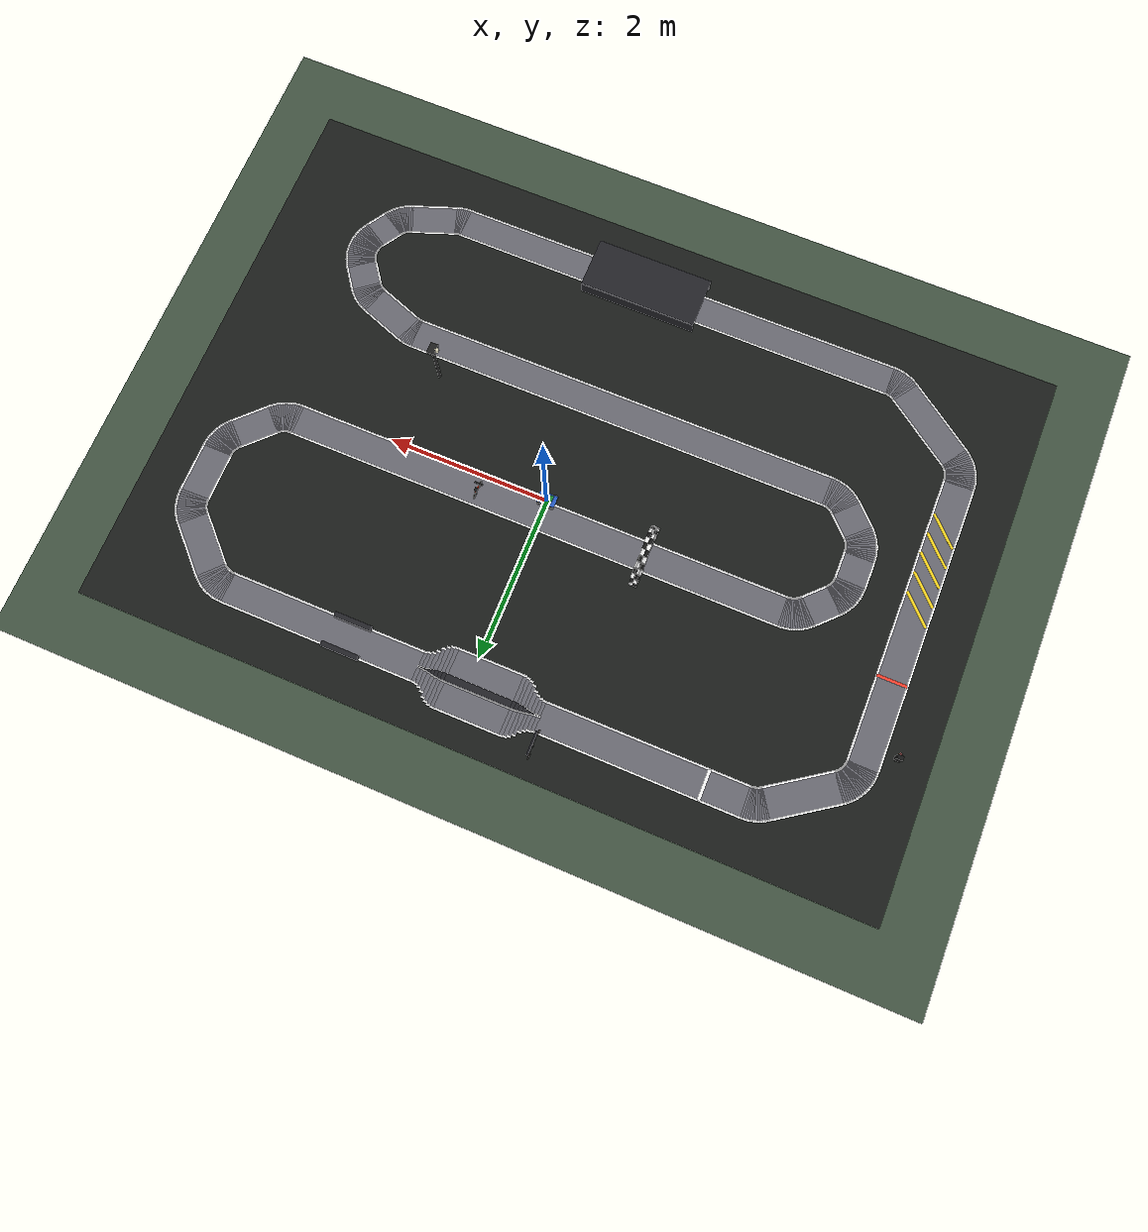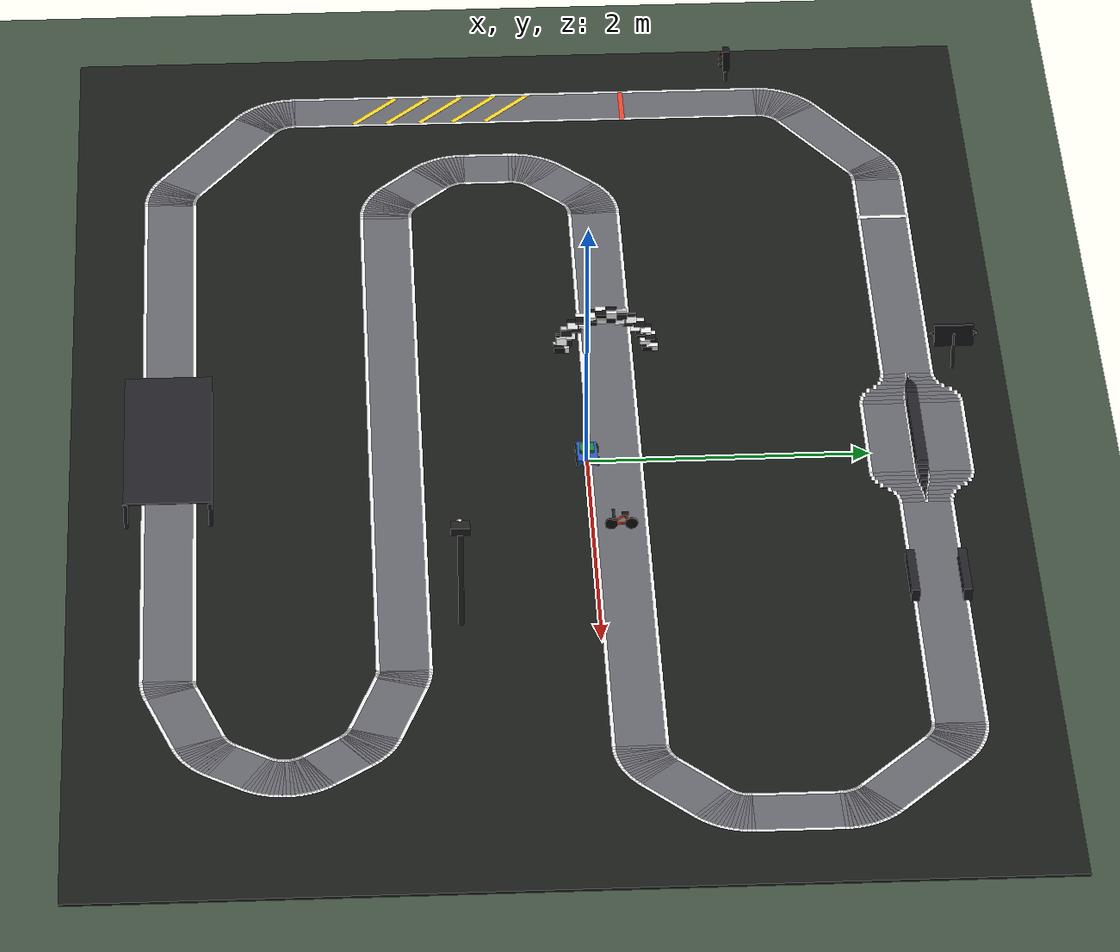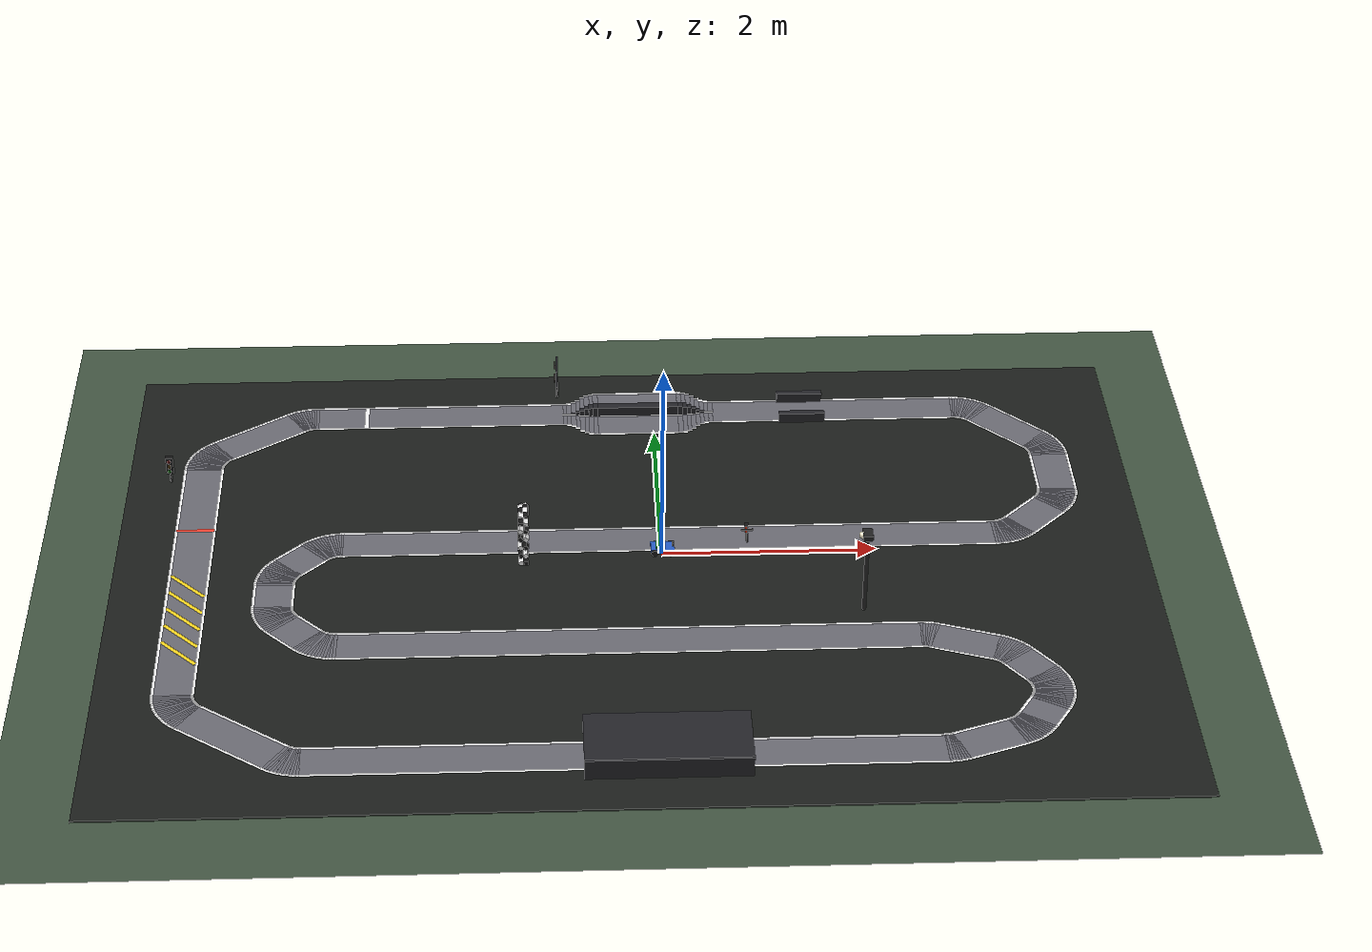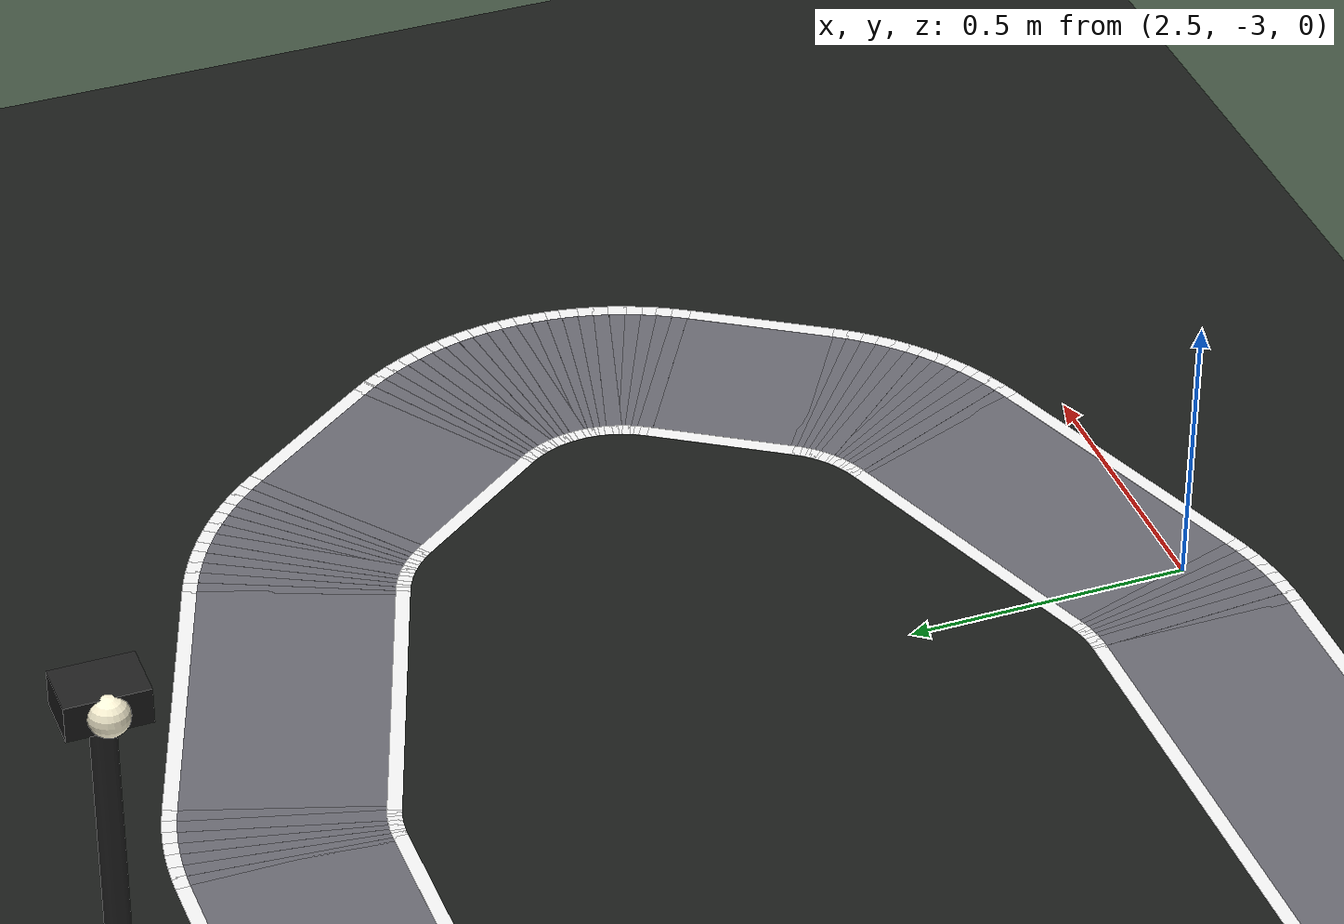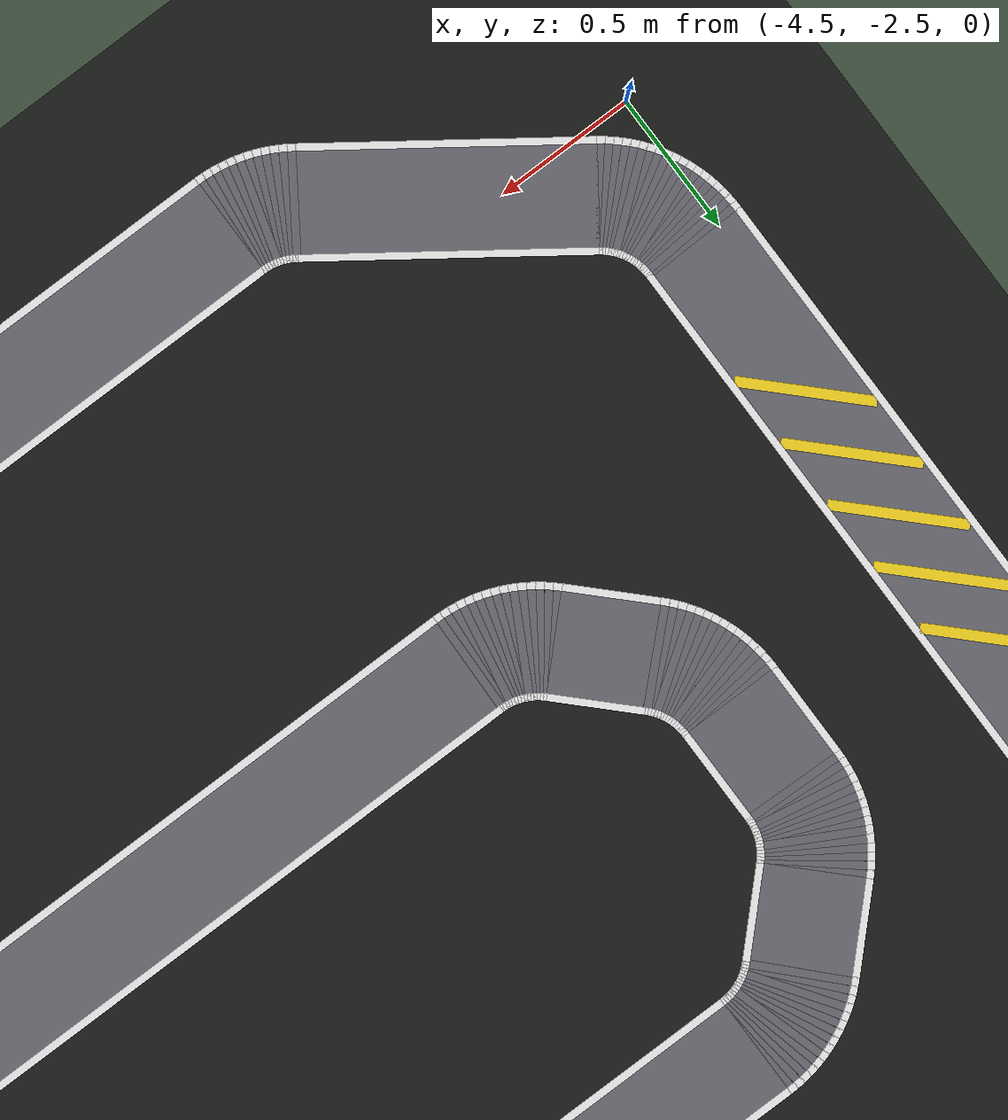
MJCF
<mujoco model="challenge">
  <compiler angle="radian" autolimits="true"/>
  <option timestep="0.002" integrator="implicitfast"/>

  <visual>
    <!-- offscreen framebuffer: must be >= the largest render requested.
         800x450 onboard camera; view_camera.py's chase panel is 600x450. -->
    <global offwidth="800" offheight="480"/>
    <!-- weak headlight so the dark tunnel is genuinely dark on camera -->
    <headlight diffuse="0.12 0.12 0.12" ambient="0.22 0.22 0.22"/>
  </visual>

  <asset>
    <texture type="skybox" builtin="gradient" rgb1="0.45 0.65 0.9" rgb2="0.9 0.95 1" width="256" height="256"/>
    <!-- dark ground surrounding the road, so the paved strip stands out -->
    <texture type="2d" name="carpet" builtin="checker" rgb1="0.09 0.10 0.09" rgb2="0.11 0.12 0.11"
             width="512" height="512"/>
    <material name="floor" texture="carpet" texrepeat="16 16" texuniform="true" reflectance="0" specular="0.1"/>
    <!-- paved road surface: mid gray, clearly brighter than the ground -->
    <material name="road" rgba="0.40 0.40 0.43 1" reflectance="0.05" specular="0.1"/>
    <material name="line" rgba="0.93 0.93 0.93 1"/>
  </asset>

  <worldbody>
    <light directional="true" pos="3 -4 6" dir="-0.35 0.45 -0.85" diffuse="0.85 0.85 0.8" castshadow="true"/>

    <geom name="ground" type="plane" size="0 0 1" rgba="0.25 0.32 0.25 1"/>
    <geom name="floor" type="box" size="4.83 3.35 0.01"
          pos="-0.28 -0.30 0.01" material="floor"/>

    <geom name="road_0" type="box" size="1.2202 0.18 0.0006" pos="-2.1162 2.3500 0.02060" euler="0 0 0.0000" material="road" contype="0" conaffinity="0"/>
    <geom name="road_1" type="box" size="1.2003 0.18 0.0006" pos="1.7963 2.3500 0.02060" euler="0 0 0.0000" material="road" contype="0" conaffinity="0"/>
    <geom name="edge_2_l" type="box" size="1.2182 0.0125 0.0004" pos="-2.1162 2.5300 0.0212" euler="0 0 0.0000" material="line" contype="0" conaffinity="0"/>
    <geom name="edge_3_l" type="box" size="1.1983 0.0125 0.0004" pos="1.7963 2.5300 0.0212" euler="0 0 0.0000" material="line" contype="0" conaffinity="0"/>
    <geom name="edge_4_r" type="box" size="1.2182 0.0125 0.0004" pos="-2.1162 2.1700 0.0212" euler="0 0 0.0000" material="line" contype="0" conaffinity="0"/>
    <geom name="edge_5_r" type="box" size="1.1983 0.0125 0.0004" pos="1.7963 2.1700 0.0212" euler="0 0 0.0000" material="line" contype="0" conaffinity="0"/>
    <geom name="road_6" type="box" size="0.0139 0.18 0.0006" pos="3.0025 2.3499 0.02060" euler="0 0 -0.0262" material="road" contype="0" conaffinity="0"/>
    <geom name="road_7" type="box" size="0.0139 0.18 0.0006" pos="3.0224 2.3488 0.02066" euler="0 0 -0.0785" material="road" contype="0" conaffinity="0"/>
    <geom name="road_8" type="box" size="0.0139 0.18 0.0006" pos="3.0422 2.3467 0.02072" euler="0 0 -0.1309" material="road" contype="0" conaffinity="0"/>
    <geom name="road_9" type="box" size="0.0139 0.18 0.0006" pos="3.0618 2.3436 0.02078" euler="0 0 -0.1833" material="road" contype="0" conaffinity="0"/>
    <geom name="road_10" type="box" size="0.0139 0.18 0.0006" pos="3.0813 2.3395 0.02084" euler="0 0 -0.2356" material="road" contype="0" conaffinity="0"/>
    <geom name="road_11" type="box" size="0.0139 0.18 0.0006" pos="3.1005 2.3344 0.02090" euler="0 0 -0.2880" material="road" contype="0" conaffinity="0"/>
    <geom name="road_12" type="box" size="0.0139 0.18 0.0006" pos="3.1194 2.3282 0.02060" euler="0 0 -0.3403" material="road" contype="0" conaffinity="0"/>
    <geom name="road_13" type="box" size="0.0139 0.18 0.0006" pos="3.1380 2.3211 0.02066" euler="0 0 -0.3927" material="road" contype="0" conaffinity="0"/>
    <geom name="road_14" type="box" size="0.0139 0.18 0.0006" pos="3.1562 2.3130 0.02072" euler="0 0 -0.4451" material="road" contype="0" conaffinity="0"/>
    <geom name="road_15" type="box" size="0.0139 0.18 0.0006" pos="3.1739 2.3040 0.02078" euler="0 0 -0.4974" material="road" contype="0" conaffinity="0"/>
    <geom name="road_16" type="box" size="0.0139 0.18 0.0006" pos="3.1911 2.2940 0.02084" euler="0 0 -0.5498" material="road" contype="0" conaffinity="0"/>
    <geom name="road_17" type="box" size="0.0139 0.18 0.0006" pos="3.2078 2.2832 0.02090" euler="0 0 -0.6021" material="road" contype="0" conaffinity="0"/>
    <geom name="road_18" type="box" size="0.0139 0.18 0.0006" pos="3.2239 2.2715 0.02060" euler="0 0 -0.6545" material="road" contype="0" conaffinity="0"/>
    <geom name="road_19" type="box" size="0.0139 0.18 0.0006" pos="3.2394 2.2590 0.02066" euler="0 0 -0.7069" material="road" contype="0" conaffinity="0"/>
    <geom name="road_20" type="box" size="0.0139 0.18 0.0006" pos="3.2542 2.2456 0.02072" euler="0 0 -0.7592" material="road" contype="0" conaffinity="0"/>
    <geom name="edge_21_l" type="box" size="0.0167 0.0125 0.0004" pos="3.0073 2.5296 0.0212" euler="0 0 -0.0262" material="line" contype="0" conaffinity="0"/>
    <geom name="edge_22_l" type="box" size="0.0167 0.0125 0.0004" pos="3.0365 2.5281 0.0212" euler="0 0 -0.0785" material="line" contype="0" conaffinity="0"/>
    <geom name="edge_23_l" type="box" size="0.0167 0.0125 0.0004" pos="3.0657 2.5250 0.0212" euler="0 0 -0.1309" material="line" contype="0" conaffinity="0"/>
    <geom name="edge_24_l" type="box" size="0.0167 0.0125 0.0004" pos="3.0946 2.5204 0.0212" euler="0 0 -0.1833" material="line" contype="0" conaffinity="0"/>
    <geom name="edge_25_l" type="box" size="0.0167 0.0125 0.0004" pos="3.1233 2.5143 0.0212" euler="0 0 -0.2356" material="line" contype="0" conaffinity="0"/>
    <geom name="edge_26_l" type="box" size="0.0167 0.0125 0.0004" pos="3.1516 2.5068 0.0212" euler="0 0 -0.2880" material="line" contype="0" conaffinity="0"/>
    <geom name="edge_27_l" type="box" size="0.0167 0.0125 0.0004" pos="3.1795 2.4977 0.0212" euler="0 0 -0.3403" material="line" contype="0" conaffinity="0"/>
    <geom name="edge_28_l" type="box" size="0.0167 0.0125 0.0004" pos="3.2068 2.4872 0.0212" euler="0 0 -0.3927" material="line" contype="0" conaffinity="0"/>
    <geom name="edge_29_l" type="box" size="0.0167 0.0125 0.0004" pos="3.2336 2.4753 0.0212" euler="0 0 -0.4451" material="line" contype="0" conaffinity="0"/>
    <geom name="edge_30_l" type="box" size="0.0167 0.0125 0.0004" pos="3.2597 2.4620 0.0212" euler="0 0 -0.4974" material="line" contype="0" conaffinity="0"/>
    <geom name="edge_31_l" type="box" size="0.0167 0.0125 0.0004" pos="3.2851 2.4473 0.0212" euler="0 0 -0.5498" material="line" contype="0" conaffinity="0"/>
    <geom name="edge_32_l" type="box" size="0.0167 0.0125 0.0004" pos="3.3097 2.4314 0.0212" euler="0 0 -0.6021" material="line" contype="0" conaffinity="0"/>
    <geom name="edge_33_l" type="box" size="0.0167 0.0125 0.0004" pos="3.3334 2.4141 0.0212" euler="0 0 -0.6545" material="line" contype="0" conaffinity="0"/>
    <geom name="edge_34_l" type="box" size="0.0167 0.0125 0.0004" pos="3.3562 2.3957 0.0212" euler="0 0 -0.7069" material="line" contype="0" conaffinity="0"/>
    <geom name="edge_35_l" type="box" size="0.0167 0.0125 0.0004" pos="3.3779 2.3761 0.0212" euler="0 0 -0.7592" material="line" contype="0" conaffinity="0"/>
    <geom name="edge_36_r" type="box" size="0.0072 0.0125 0.0004" pos="2.9978 2.1699 0.0212" euler="0 0 -0.0262" material="line" contype="0" conaffinity="0"/>
    <geom name="edge_37_r" type="box" size="0.0072 0.0125 0.0004" pos="3.0083 2.1693 0.0212" euler="0 0 -0.0785" material="line" contype="0" conaffinity="0"/>
    <geom name="edge_38_r" type="box" size="0.0072 0.0125 0.0004" pos="3.0187 2.1682 0.0212" euler="0 0 -0.1309" material="line" contype="0" conaffinity="0"/>
    <geom name="edge_39_r" type="box" size="0.0072 0.0125 0.0004" pos="3.0290 2.1666 0.0212" euler="0 0 -0.1833" material="line" contype="0" conaffinity="0"/>
    <geom name="edge_40_r" type="box" size="0.0072 0.0125 0.0004" pos="3.0393 2.1644 0.0212" euler="0 0 -0.2356" material="line" contype="0" conaffinity="0"/>
    <geom name="edge_41_r" type="box" size="0.0072 0.0125 0.0004" pos="3.0494 2.1617 0.0212" euler="0 0 -0.2880" material="line" contype="0" conaffinity="0"/>
    <geom name="edge_42_r" type="box" size="0.0072 0.0125 0.0004" pos="3.0593 2.1585 0.0212" euler="0 0 -0.3403" material="line" contype="0" conaffinity="0"/>
    <geom name="edge_43_r" type="box" size="0.0072 0.0125 0.0004" pos="3.0691 2.1547 0.0212" euler="0 0 -0.3927" material="line" contype="0" conaffinity="0"/>
    <geom name="edge_44_r" type="box" size="0.0072 0.0125 0.0004" pos="3.0787 2.1505 0.0212" euler="0 0 -0.4451" material="line" contype="0" conaffinity="0"/>
    <geom name="edge_45_r" type="box" size="0.0072 0.0125 0.0004" pos="3.0880 2.1457 0.0212" euler="0 0 -0.4974" material="line" contype="0" conaffinity="0"/>
    <geom name="edge_46_r" type="box" size="0.0072 0.0125 0.0004" pos="3.0971 2.1405 0.0212" euler="0 0 -0.5498" material="line" contype="0" conaffinity="0"/>
    <geom name="edge_47_r" type="box" size="0.0072 0.0125 0.0004" pos="3.1058 2.1348 0.0212" euler="0 0 -0.6021" material="line" contype="0" conaffinity="0"/>
    <geom name="edge_48_r" type="box" size="0.0072 0.0125 0.0004" pos="3.1143 2.1286 0.0212" euler="0 0 -0.6545" material="line" contype="0" conaffinity="0"/>
    <geom name="edge_49_r" type="box" size="0.0072 0.0125 0.0004" pos="3.1224 2.1220 0.0212" euler="0 0 -0.7069" material="line" contype="0" conaffinity="0"/>
    <geom name="edge_50_r" type="box" size="0.0072 0.0125 0.0004" pos="3.1302 2.1150 0.0212" euler="0 0 -0.7592" material="line" contype="0" conaffinity="0"/>
    <geom name="road_51" type="box" size="0.3416 0.18 0.0006" pos="3.5000 2.0000 0.02060" euler="0 0 -0.7854" material="road" contype="0" conaffinity="0"/>
    <geom name="edge_52_l" type="box" size="0.3396 0.0125 0.0004" pos="3.6273 2.1273 0.0212" euler="0 0 -0.7854" material="line" contype="0" conaffinity="0"/>
    <geom name="edge_53_r" type="box" size="0.3396 0.0125 0.0004" pos="3.3727 1.8727 0.0212" euler="0 0 -0.7854" material="line" contype="0" conaffinity="0"/>
    <geom name="road_54" type="box" size="0.0139 0.18 0.0006" pos="3.7456 1.7542 0.02060" euler="0 0 -0.8116" material="road" contype="0" conaffinity="0"/>
    <geom name="road_55" type="box" size="0.0139 0.18 0.0006" pos="3.7590 1.7394 0.02066" euler="0 0 -0.8639" material="road" contype="0" conaffinity="0"/>
    <geom name="road_56" type="box" size="0.0139 0.18 0.0006" pos="3.7715 1.7239 0.02072" euler="0 0 -0.9163" material="road" contype="0" conaffinity="0"/>
    <geom name="road_57" type="box" size="0.0139 0.18 0.0006" pos="3.7832 1.7078 0.02078" euler="0 0 -0.9687" material="road" contype="0" conaffinity="0"/>
    <geom name="road_58" type="box" size="0.0139 0.18 0.0006" pos="3.7940 1.6911 0.02084" euler="0 0 -1.0210" material="road" contype="0" conaffinity="0"/>
    <geom name="road_59" type="box" size="0.0139 0.18 0.0006" pos="3.8040 1.6739 0.02090" euler="0 0 -1.0734" material="road" contype="0" conaffinity="0"/>
    <geom name="road_60" type="box" size="0.0139 0.18 0.0006" pos="3.8130 1.6562 0.02060" euler="0 0 -1.1257" material="road" contype="0" conaffinity="0"/>
    <geom name="road_61" type="box" size="0.0139 0.18 0.0006" pos="3.8211 1.6380 0.02066" euler="0 0 -1.1781" material="road" contype="0" conaffinity="0"/>
    <geom name="road_62" type="box" size="0.0139 0.18 0.0006" pos="3.8282 1.6194 0.02072" euler="0 0 -1.2305" material="road" contype="0" conaffinity="0"/>
    <geom name="road_63" type="box" size="0.0139 0.18 0.0006" pos="3.8344 1.6005 0.02078" euler="0 0 -1.2828" material="road" contype="0" conaffinity="0"/>
    <geom name="road_64" type="box" size="0.0139 0.18 0.0006" pos="3.8395 1.5813 0.02084" euler="0 0 -1.3352" material="road" contype="0" conaffinity="0"/>
    <geom name="road_65" type="box" size="0.0139 0.18 0.0006" pos="3.8436 1.5618 0.02090" euler="0 0 -1.3875" material="road" contype="0" conaffinity="0"/>
    <geom name="road_66" type="box" size="0.0139 0.18 0.0006" pos="3.8467 1.5422 0.02060" euler="0 0 -1.4399" material="road" contype="0" conaffinity="0"/>
    <geom name="road_67" type="box" size="0.0139 0.18 0.0006" pos="3.8488 1.5224 0.02066" euler="0 0 -1.4923" material="road" contype="0" conaffinity="0"/>
    <geom name="road_68" type="box" size="0.0139 0.18 0.0006" pos="3.8499 1.5025 0.02072" euler="0 0 -1.5446" material="road" contype="0" conaffinity="0"/>
    <geom name="edge_69_l" type="box" size="0.0167 0.0125 0.0004" pos="3.8761 1.8779 0.0212" euler="0 0 -0.8116" material="line" contype="0" conaffinity="0"/>
    <geom name="edge_70_l" type="box" size="0.0167 0.0125 0.0004" pos="3.8957 1.8562 0.0212" euler="0 0 -0.8639" material="line" contype="0" conaffinity="0"/>
    <geom name="edge_71_l" type="box" size="0.0167 0.0125 0.0004" pos="3.9141 1.8334 0.0212" euler="0 0 -0.9163" material="line" contype="0" conaffinity="0"/>
    <geom name="edge_72_l" type="box" size="0.0167 0.0125 0.0004" pos="3.9314 1.8097 0.0212" euler="0 0 -0.9687" material="line" contype="0" conaffinity="0"/>
    <geom name="edge_73_l" type="box" size="0.0167 0.0125 0.0004" pos="3.9473 1.7851 0.0212" euler="0 0 -1.0210" material="line" contype="0" conaffinity="0"/>
    <geom name="edge_74_l" type="box" size="0.0167 0.0125 0.0004" pos="3.9620 1.7597 0.0212" euler="0 0 -1.0734" material="line" contype="0" conaffinity="0"/>
    <geom name="edge_75_l" type="box" size="0.0167 0.0125 0.0004" pos="3.9753 1.7336 0.0212" euler="0 0 -1.1257" material="line" contype="0" conaffinity="0"/>
    <geom name="edge_76_l" type="box" size="0.0167 0.0125 0.0004" pos="3.9872 1.7068 0.0212" euler="0 0 -1.1781" material="line" contype="0" conaffinity="0"/>
    <geom name="edge_77_l" type="box" size="0.0167 0.0125 0.0004" pos="3.9977 1.6795 0.0212" euler="0 0 -1.2305" material="line" contype="0" conaffinity="0"/>
    <geom name="edge_78_l" type="box" size="0.0167 0.0125 0.0004" pos="4.0068 1.6516 0.0212" euler="0 0 -1.2828" material="line" contype="0" conaffinity="0"/>
    <geom name="edge_79_l" type="box" size="0.0167 0.0125 0.0004" pos="4.0143 1.6233 0.0212" euler="0 0 -1.3352" material="line" contype="0" conaffinity="0"/>
    <geom name="edge_80_l" type="box" size="0.0167 0.0125 0.0004" pos="4.0204 1.5946 0.0212" euler="0 0 -1.3875" material="line" contype="0" conaffinity="0"/>
    <geom name="edge_81_l" type="box" size="0.0167 0.0125 0.0004" pos="4.0250 1.5657 0.0212" euler="0 0 -1.4399" material="line" contype="0" conaffinity="0"/>
    <geom name="edge_82_l" type="box" size="0.0167 0.0125 0.0004" pos="4.0281 1.5365 0.0212" euler="0 0 -1.4923" material="line" contype="0" conaffinity="0"/>
    <geom name="edge_83_l" type="box" size="0.0167 0.0125 0.0004" pos="4.0296 1.5073 0.0212" euler="0 0 -1.5446" material="line" contype="0" conaffinity="0"/>
    <geom name="edge_84_r" type="box" size="0.0072 0.0125 0.0004" pos="3.6150 1.6302 0.0212" euler="0 0 -0.8116" material="line" contype="0" conaffinity="0"/>
    <geom name="edge_85_r" type="box" size="0.0072 0.0125 0.0004" pos="3.6220 1.6224 0.0212" euler="0 0 -0.8639" material="line" contype="0" conaffinity="0"/>
    <geom name="edge_86_r" type="box" size="0.0072 0.0125 0.0004" pos="3.6286 1.6143 0.0212" euler="0 0 -0.9163" material="line" contype="0" conaffinity="0"/>
    <geom name="edge_87_r" type="box" size="0.0072 0.0125 0.0004" pos="3.6348 1.6058 0.0212" euler="0 0 -0.9687" material="line" contype="0" conaffinity="0"/>
    <geom name="edge_88_r" type="box" size="0.0072 0.0125 0.0004" pos="3.6405 1.5971 0.0212" euler="0 0 -1.0210" material="line" contype="0" conaffinity="0"/>
    <geom name="edge_89_r" type="box" size="0.0072 0.0125 0.0004" pos="3.6457 1.5880 0.0212" euler="0 0 -1.0734" material="line" contype="0" conaffinity="0"/>
    <geom name="edge_90_r" type="box" size="0.0072 0.0125 0.0004" pos="3.6505 1.5787 0.0212" euler="0 0 -1.1257" material="line" contype="0" conaffinity="0"/>
    <geom name="edge_91_r" type="box" size="0.0072 0.0125 0.0004" pos="3.6547 1.5691 0.0212" euler="0 0 -1.1781" material="line" contype="0" conaffinity="0"/>
    <geom name="edge_92_r" type="box" size="0.0072 0.0125 0.0004" pos="3.6585 1.5593 0.0212" euler="0 0 -1.2305" material="line" contype="0" conaffinity="0"/>
    <geom name="edge_93_r" type="box" size="0.0072 0.0125 0.0004" pos="3.6617 1.5494 0.0212" euler="0 0 -1.2828" material="line" contype="0" conaffinity="0"/>
    <geom name="edge_94_r" type="box" size="0.0072 0.0125 0.0004" pos="3.6644 1.5393 0.0212" euler="0 0 -1.3352" material="line" contype="0" conaffinity="0"/>
    <geom name="edge_95_r" type="box" size="0.0072 0.0125 0.0004" pos="3.6666 1.5290 0.0212" euler="0 0 -1.3875" material="line" contype="0" conaffinity="0"/>
    <geom name="edge_96_r" type="box" size="0.0072 0.0125 0.0004" pos="3.6682 1.5187 0.0212" euler="0 0 -1.4399" material="line" contype="0" conaffinity="0"/>
    <geom name="edge_97_r" type="box" size="0.0072 0.0125 0.0004" pos="3.6693 1.5083 0.0212" euler="0 0 -1.4923" material="line" contype="0" conaffinity="0"/>
    <geom name="edge_98_r" type="box" size="0.0072 0.0125 0.0004" pos="3.6699 1.4978 0.0212" euler="0 0 -1.5446" material="line" contype="0" conaffinity="0"/>
    <geom name="road_99" type="box" size="0.2966 0.18 0.0006" pos="3.8500 1.2000 0.02060" euler="0 0 -1.5708" material="road" contype="0" conaffinity="0"/>
    <geom name="edge_100_l" type="box" size="0.2946 0.0125 0.0004" pos="4.0300 1.2000 0.0212" euler="0 0 -1.5708" material="line" contype="0" conaffinity="0"/>
    <geom name="edge_101_r" type="box" size="0.2946 0.0125 0.0004" pos="3.6700 1.2000 0.0212" euler="0 0 -1.5708" material="line" contype="0" conaffinity="0"/>
    <geom name="road_102" type="box" size="0.0139 0.18 0.0006" pos="3.8499 0.8975 0.02060" euler="0 0 -1.5970" material="road" contype="0" conaffinity="0"/>
    <geom name="road_103" type="box" size="0.0139 0.18 0.0006" pos="3.8488 0.8776 0.02066" euler="0 0 -1.6493" material="road" contype="0" conaffinity="0"/>
    <geom name="road_104" type="box" size="0.0139 0.18 0.0006" pos="3.8467 0.8578 0.02072" euler="0 0 -1.7017" material="road" contype="0" conaffinity="0"/>
    <geom name="road_105" type="box" size="0.0139 0.18 0.0006" pos="3.8436 0.8382 0.02078" euler="0 0 -1.7541" material="road" contype="0" conaffinity="0"/>
    <geom name="road_106" type="box" size="0.0139 0.18 0.0006" pos="3.8395 0.8187 0.02084" euler="0 0 -1.8064" material="road" contype="0" conaffinity="0"/>
    <geom name="road_107" type="box" size="0.0139 0.18 0.0006" pos="3.8344 0.7995 0.02090" euler="0 0 -1.8588" material="road" contype="0" conaffinity="0"/>
    <geom name="road_108" type="box" size="0.0139 0.18 0.0006" pos="3.8282 0.7806 0.02060" euler="0 0 -1.9111" material="road" contype="0" conaffinity="0"/>
    <geom name="road_109" type="box" size="0.0139 0.18 0.0006" pos="3.8211 0.7620 0.02066" euler="0 0 -1.9635" material="road" contype="0" conaffinity="0"/>
    <geom name="road_110" type="box" size="0.0139 0.18 0.0006" pos="3.8130 0.7438 0.02072" euler="0 0 -2.0159" material="road" contype="0" conaffinity="0"/>
    <geom name="road_111" type="box" size="0.0139 0.18 0.0006" pos="3.8040 0.7261 0.02078" euler="0 0 -2.0682" material="road" contype="0" conaffinity="0"/>
    <geom name="road_112" type="box" size="0.0139 0.18 0.0006" pos="3.7940 0.7089 0.02084" euler="0 0 -2.1206" material="road" contype="0" conaffinity="0"/>
    <geom name="road_113" type="box" size="0.0139 0.18 0.0006" pos="3.7832 0.6922 0.02090" euler="0 0 -2.1729" material="road" contype="0" conaffinity="0"/>
    <geom name="road_114" type="box" size="0.0139 0.18 0.0006" pos="3.7715 0.6761 0.02060" euler="0 0 -2.2253" material="road" contype="0" conaffinity="0"/>
    <geom name="road_115" type="box" size="0.0139 0.18 0.0006" pos="3.7590 0.6606 0.02066" euler="0 0 -2.2777" material="road" contype="0" conaffinity="0"/>
    <geom name="road_116" type="box" size="0.0139 0.18 0.0006" pos="3.7456 0.6458 0.02072" euler="0 0 -2.3300" material="road" contype="0" conaffinity="0"/>
    <geom name="edge_117_l" type="box" size="0.0167 0.0125 0.0004" pos="4.0296 0.8927 0.0212" euler="0 0 -1.5970" material="line" contype="0" conaffinity="0"/>
    <geom name="edge_118_l" type="box" size="0.0167 0.0125 0.0004" pos="4.0281 0.8635 0.0212" euler="0 0 -1.6493" material="line" contype="0" conaffinity="0"/>
    <geom name="edge_119_l" type="box" size="0.0167 0.0125 0.0004" pos="4.0250 0.8343 0.0212" euler="0 0 -1.7017" material="line" contype="0" conaffinity="0"/>
    <geom name="edge_120_l" type="box" size="0.0167 0.0125 0.0004" pos="4.0204 0.8054 0.0212" euler="0 0 -1.7541" material="line" contype="0" conaffinity="0"/>
    <geom name="edge_121_l" type="box" size="0.0167 0.0125 0.0004" pos="4.0143 0.7767 0.0212" euler="0 0 -1.8064" material="line" contype="0" conaffinity="0"/>
    <geom name="edge_122_l" type="box" size="0.0167 0.0125 0.0004" pos="4.0068 0.7484 0.0212" euler="0 0 -1.8588" material="line" contype="0" conaffinity="0"/>
    <geom name="edge_123_l" type="box" size="0.0167 0.0125 0.0004" pos="3.9977 0.7205 0.0212" euler="0 0 -1.9111" material="line" contype="0" conaffinity="0"/>
    <geom name="edge_124_l" type="box" size="0.0167 0.0125 0.0004" pos="3.9872 0.6932 0.0212" euler="0 0 -1.9635" material="line" contype="0" conaffinity="0"/>
    <geom name="edge_125_l" type="box" size="0.0167 0.0125 0.0004" pos="3.9753 0.6664 0.0212" euler="0 0 -2.0159" material="line" contype="0" conaffinity="0"/>
    <geom name="edge_126_l" type="box" size="0.0167 0.0125 0.0004" pos="3.9620 0.6403 0.0212" euler="0 0 -2.0682" material="line" contype="0" conaffinity="0"/>
    <geom name="edge_127_l" type="box" size="0.0167 0.0125 0.0004" pos="3.9473 0.6149 0.0212" euler="0 0 -2.1206" material="line" contype="0" conaffinity="0"/>
    <geom name="edge_128_l" type="box" size="0.0167 0.0125 0.0004" pos="3.9314 0.5903 0.0212" euler="0 0 -2.1729" material="line" contype="0" conaffinity="0"/>
    <geom name="edge_129_l" type="box" size="0.0167 0.0125 0.0004" pos="3.9141 0.5666 0.0212" euler="0 0 -2.2253" material="line" contype="0" conaffinity="0"/>
    <geom name="edge_130_l" type="box" size="0.0167 0.0125 0.0004" pos="3.8957 0.5438 0.0212" euler="0 0 -2.2777" material="line" contype="0" conaffinity="0"/>
    <geom name="edge_131_l" type="box" size="0.0167 0.0125 0.0004" pos="3.8761 0.5221 0.0212" euler="0 0 -2.3300" material="line" contype="0" conaffinity="0"/>
    <geom name="edge_132_r" type="box" size="0.0072 0.0125 0.0004" pos="3.6699 0.9022 0.0212" euler="0 0 -1.5970" material="line" contype="0" conaffinity="0"/>
    <geom name="edge_133_r" type="box" size="0.0072 0.0125 0.0004" pos="3.6693 0.8917 0.0212" euler="0 0 -1.6493" material="line" contype="0" conaffinity="0"/>
    <geom name="edge_134_r" type="box" size="0.0072 0.0125 0.0004" pos="3.6682 0.8813 0.0212" euler="0 0 -1.7017" material="line" contype="0" conaffinity="0"/>
    <geom name="edge_135_r" type="box" size="0.0072 0.0125 0.0004" pos="3.6666 0.8710 0.0212" euler="0 0 -1.7541" material="line" contype="0" conaffinity="0"/>
    <geom name="edge_136_r" type="box" size="0.0072 0.0125 0.0004" pos="3.6644 0.8607 0.0212" euler="0 0 -1.8064" material="line" contype="0" conaffinity="0"/>
    <geom name="edge_137_r" type="box" size="0.0072 0.0125 0.0004" pos="3.6617 0.8506 0.0212" euler="0 0 -1.8588" material="line" contype="0" conaffinity="0"/>
    <geom name="edge_138_r" type="box" size="0.0072 0.0125 0.0004" pos="3.6585 0.8407 0.0212" euler="0 0 -1.9111" material="line" contype="0" conaffinity="0"/>
    <geom name="edge_139_r" type="box" size="0.0072 0.0125 0.0004" pos="3.6547 0.8309 0.0212" euler="0 0 -1.9635" material="line" contype="0" conaffinity="0"/>
    <geom name="edge_140_r" type="box" size="0.0072 0.0125 0.0004" pos="3.6505 0.8213 0.0212" euler="0 0 -2.0159" material="line" contype="0" conaffinity="0"/>
    <geom name="edge_141_r" type="box" size="0.0072 0.0125 0.0004" pos="3.6457 0.8120 0.0212" euler="0 0 -2.0682" material="line" contype="0" conaffinity="0"/>
    <geom name="edge_142_r" type="box" size="0.0072 0.0125 0.0004" pos="3.6405 0.8029 0.0212" euler="0 0 -2.1206" material="line" contype="0" conaffinity="0"/>
    <geom name="edge_143_r" type="box" size="0.0072 0.0125 0.0004" pos="3.6348 0.7942 0.0212" euler="0 0 -2.1729" material="line" contype="0" conaffinity="0"/>
    <geom name="edge_144_r" type="box" size="0.0072 0.0125 0.0004" pos="3.6286 0.7857 0.0212" euler="0 0 -2.2253" material="line" contype="0" conaffinity="0"/>
    <geom name="edge_145_r" type="box" size="0.0072 0.0125 0.0004" pos="3.6220 0.7776 0.0212" euler="0 0 -2.2777" material="line" contype="0" conaffinity="0"/>
    <geom name="edge_146_r" type="box" size="0.0072 0.0125 0.0004" pos="3.6150 0.7698 0.0212" euler="0 0 -2.3300" material="line" contype="0" conaffinity="0"/>
    <geom name="road_147" type="box" size="0.2355 0.18 0.0006" pos="3.5750 0.4750 0.02060" euler="0 0 -2.3562" material="road" contype="0" conaffinity="0"/>
    <geom name="edge_148_l" type="box" size="0.2335 0.0125 0.0004" pos="3.7023 0.3477 0.0212" euler="0 0 -2.3562" material="line" contype="0" conaffinity="0"/>
    <geom name="edge_149_r" type="box" size="0.2335 0.0125 0.0004" pos="3.4477 0.6023 0.0212" euler="0 0 -2.3562" material="line" contype="0" conaffinity="0"/>
    <geom name="road_150" type="box" size="0.0139 0.18 0.0006" pos="3.4042 0.3044 0.02060" euler="0 0 -2.3824" material="road" contype="0" conaffinity="0"/>
    <geom name="road_151" type="box" size="0.0139 0.18 0.0006" pos="3.3894 0.2910 0.02066" euler="0 0 -2.4347" material="road" contype="0" conaffinity="0"/>
    <geom name="road_152" type="box" size="0.0139 0.18 0.0006" pos="3.3739 0.2785 0.02072" euler="0 0 -2.4871" material="road" contype="0" conaffinity="0"/>
    <geom name="road_153" type="box" size="0.0139 0.18 0.0006" pos="3.3578 0.2668 0.02078" euler="0 0 -2.5395" material="road" contype="0" conaffinity="0"/>
    <geom name="road_154" type="box" size="0.0139 0.18 0.0006" pos="3.3411 0.2560 0.02084" euler="0 0 -2.5918" material="road" contype="0" conaffinity="0"/>
    <geom name="road_155" type="box" size="0.0139 0.18 0.0006" pos="3.3239 0.2460 0.02090" euler="0 0 -2.6442" material="road" contype="0" conaffinity="0"/>
    <geom name="road_156" type="box" size="0.0139 0.18 0.0006" pos="3.3062 0.2370 0.02060" euler="0 0 -2.6965" material="road" contype="0" conaffinity="0"/>
    <geom name="road_157" type="box" size="0.0139 0.18 0.0006" pos="3.2880 0.2289 0.02066" euler="0 0 -2.7489" material="road" contype="0" conaffinity="0"/>
    <geom name="road_158" type="box" size="0.0139 0.18 0.0006" pos="3.2694 0.2218 0.02072" euler="0 0 -2.8013" material="road" contype="0" conaffinity="0"/>
    <geom name="road_159" type="box" size="0.0139 0.18 0.0006" pos="3.2505 0.2156 0.02078" euler="0 0 -2.8536" material="road" contype="0" conaffinity="0"/>
    <geom name="road_160" type="box" size="0.0139 0.18 0.0006" pos="3.2313 0.2105 0.02084" euler="0 0 -2.9060" material="road" contype="0" conaffinity="0"/>
    <geom name="road_161" type="box" size="0.0139 0.18 0.0006" pos="3.2118 0.2064 0.02090" euler="0 0 -2.9583" material="road" contype="0" conaffinity="0"/>
    <geom name="road_162" type="box" size="0.0139 0.18 0.0006" pos="3.1922 0.2033 0.02060" euler="0 0 -3.0107" material="road" contype="0" conaffinity="0"/>
    <geom name="road_163" type="box" size="0.0139 0.18 0.0006" pos="3.1724 0.2012 0.02066" euler="0 0 -3.0631" material="road" contype="0" conaffinity="0"/>
    <geom name="road_164" type="box" size="0.0139 0.18 0.0006" pos="3.1525 0.2001 0.02072" euler="0 0 -3.1154" material="road" contype="0" conaffinity="0"/>
    <geom name="edge_165_l" type="box" size="0.0167 0.0125 0.0004" pos="3.5279 0.1739 0.0212" euler="0 0 -2.3824" material="line" contype="0" conaffinity="0"/>
    <geom name="edge_166_l" type="box" size="0.0167 0.0125 0.0004" pos="3.5062 0.1543 0.0212" euler="0 0 -2.4347" material="line" contype="0" conaffinity="0"/>
    <geom name="edge_167_l" type="box" size="0.0167 0.0125 0.0004" pos="3.4834 0.1359 0.0212" euler="0 0 -2.4871" material="line" contype="0" conaffinity="0"/>
    <geom name="edge_168_l" type="box" size="0.0167 0.0125 0.0004" pos="3.4597 0.1186 0.0212" euler="0 0 -2.5395" material="line" contype="0" conaffinity="0"/>
    <geom name="edge_169_l" type="box" size="0.0167 0.0125 0.0004" pos="3.4351 0.1027 0.0212" euler="0 0 -2.5918" material="line" contype="0" conaffinity="0"/>
    <geom name="edge_170_l" type="box" size="0.0167 0.0125 0.0004" pos="3.4097 0.0880 0.0212" euler="0 0 -2.6442" material="line" contype="0" conaffinity="0"/>
    <geom name="edge_171_l" type="box" size="0.0167 0.0125 0.0004" pos="3.3836 0.0747 0.0212" euler="0 0 -2.6965" material="line" contype="0" conaffinity="0"/>
    <geom name="edge_172_l" type="box" size="0.0167 0.0125 0.0004" pos="3.3568 0.0628 0.0212" euler="0 0 -2.7489" material="line" contype="0" conaffinity="0"/>
    <geom name="edge_173_l" type="box" size="0.0167 0.0125 0.0004" pos="3.3295 0.0523 0.0212" euler="0 0 -2.8013" material="line" contype="0" conaffinity="0"/>
    <geom name="edge_174_l" type="box" size="0.0167 0.0125 0.0004" pos="3.3016 0.0432 0.0212" euler="0 0 -2.8536" material="line" contype="0" conaffinity="0"/>
    <geom name="edge_175_l" type="box" size="0.0167 0.0125 0.0004" pos="3.2733 0.0357 0.0212" euler="0 0 -2.9060" material="line" contype="0" conaffinity="0"/>
    <geom name="edge_176_l" type="box" size="0.0167 0.0125 0.0004" pos="3.2446 0.0296 0.0212" euler="0 0 -2.9583" material="line" contype="0" conaffinity="0"/>
    <geom name="edge_177_l" type="box" size="0.0167 0.0125 0.0004" pos="3.2157 0.0250 0.0212" euler="0 0 -3.0107" material="line" contype="0" conaffinity="0"/>
    <geom name="edge_178_l" type="box" size="0.0167 0.0125 0.0004" pos="3.1865 0.0219 0.0212" euler="0 0 -3.0631" material="line" contype="0" conaffinity="0"/>
    <geom name="edge_179_l" type="box" size="0.0167 0.0125 0.0004" pos="3.1573 0.0204 0.0212" euler="0 0 -3.1154" material="line" contype="0" conaffinity="0"/>
    <geom name="edge_180_r" type="box" size="0.0072 0.0125 0.0004" pos="3.2802 0.4350 0.0212" euler="0 0 -2.3824" material="line" contype="0" conaffinity="0"/>
    <geom name="edge_181_r" type="box" size="0.0072 0.0125 0.0004" pos="3.2724 0.4280 0.0212" euler="0 0 -2.4347" material="line" contype="0" conaffinity="0"/>
    <geom name="edge_182_r" type="box" size="0.0072 0.0125 0.0004" pos="3.2643 0.4214 0.0212" euler="0 0 -2.4871" material="line" contype="0" conaffinity="0"/>
    <geom name="edge_183_r" type="box" size="0.0072 0.0125 0.0004" pos="3.2558 0.4152 0.0212" euler="0 0 -2.5395" material="line" contype="0" conaffinity="0"/>
    <geom name="edge_184_r" type="box" size="0.0072 0.0125 0.0004" pos="3.2471 0.4095 0.0212" euler="0 0 -2.5918" material="line" contype="0" conaffinity="0"/>
    <geom name="edge_185_r" type="box" size="0.0072 0.0125 0.0004" pos="3.2380 0.4043 0.0212" euler="0 0 -2.6442" material="line" contype="0" conaffinity="0"/>
    <geom name="edge_186_r" type="box" size="0.0072 0.0125 0.0004" pos="3.2287 0.3995 0.0212" euler="0 0 -2.6965" material="line" contype="0" conaffinity="0"/>
    <geom name="edge_187_r" type="box" size="0.0072 0.0125 0.0004" pos="3.2191 0.3953 0.0212" euler="0 0 -2.7489" material="line" contype="0" conaffinity="0"/>
    <geom name="edge_188_r" type="box" size="0.0072 0.0125 0.0004" pos="3.2093 0.3915 0.0212" euler="0 0 -2.8013" material="line" contype="0" conaffinity="0"/>
    <geom name="edge_189_r" type="box" size="0.0072 0.0125 0.0004" pos="3.1994 0.3883 0.0212" euler="0 0 -2.8536" material="line" contype="0" conaffinity="0"/>
    <geom name="edge_190_r" type="box" size="0.0072 0.0125 0.0004" pos="3.1893 0.3856 0.0212" euler="0 0 -2.9060" material="line" contype="0" conaffinity="0"/>
    <geom name="edge_191_r" type="box" size="0.0072 0.0125 0.0004" pos="3.1790 0.3834 0.0212" euler="0 0 -2.9583" material="line" contype="0" conaffinity="0"/>
    <geom name="edge_192_r" type="box" size="0.0072 0.0125 0.0004" pos="3.1687 0.3818 0.0212" euler="0 0 -3.0107" material="line" contype="0" conaffinity="0"/>
    <geom name="edge_193_r" type="box" size="0.0072 0.0125 0.0004" pos="3.1583 0.3807 0.0212" euler="0 0 -3.0631" material="line" contype="0" conaffinity="0"/>
    <geom name="edge_194_r" type="box" size="0.0072 0.0125 0.0004" pos="3.1478 0.3801 0.0212" euler="0 0 -3.1154" material="line" contype="0" conaffinity="0"/>
    <geom name="road_195" type="box" size="3.0716 0.18 0.0006" pos="0.0750 0.2000 0.02060" euler="0 0 3.1416" material="road" contype="0" conaffinity="0"/>
    <geom name="edge_196_l" type="box" size="3.0696 0.0125 0.0004" pos="0.0750 0.0200 0.0212" euler="0 0 3.1416" material="line" contype="0" conaffinity="0"/>
    <geom name="edge_197_r" type="box" size="3.0696 0.0125 0.0004" pos="0.0750 0.3800 0.0212" euler="0 0 3.1416" material="line" contype="0" conaffinity="0"/>
    <geom name="road_198" type="box" size="0.0139 0.18 0.0006" pos="-3.0025 0.1999 0.02060" euler="0 0 3.1678" material="road" contype="0" conaffinity="0"/>
    <geom name="road_199" type="box" size="0.0139 0.18 0.0006" pos="-3.0224 0.1988 0.02066" euler="0 0 3.2201" material="road" contype="0" conaffinity="0"/>
    <geom name="road_200" type="box" size="0.0139 0.18 0.0006" pos="-3.0422 0.1967 0.02072" euler="0 0 3.2725" material="road" contype="0" conaffinity="0"/>
    <geom name="road_201" type="box" size="0.0139 0.18 0.0006" pos="-3.0618 0.1936 0.02078" euler="0 0 3.3249" material="road" contype="0" conaffinity="0"/>
    <geom name="road_202" type="box" size="0.0139 0.18 0.0006" pos="-3.0813 0.1895 0.02084" euler="0 0 3.3772" material="road" contype="0" conaffinity="0"/>
    <geom name="road_203" type="box" size="0.0139 0.18 0.0006" pos="-3.1005 0.1844 0.02090" euler="0 0 3.4296" material="road" contype="0" conaffinity="0"/>
    <geom name="road_204" type="box" size="0.0139 0.18 0.0006" pos="-3.1194 0.1782 0.02060" euler="0 0 3.4819" material="road" contype="0" conaffinity="0"/>
    <geom name="road_205" type="box" size="0.0139 0.18 0.0006" pos="-3.1380 0.1711 0.02066" euler="0 0 3.5343" material="road" contype="0" conaffinity="0"/>
    <geom name="road_206" type="box" size="0.0139 0.18 0.0006" pos="-3.1562 0.1630 0.02072" euler="0 0 3.5867" material="road" contype="0" conaffinity="0"/>
    <geom name="road_207" type="box" size="0.0139 0.18 0.0006" pos="-3.1739 0.1540 0.02078" euler="0 0 3.6390" material="road" contype="0" conaffinity="0"/>
    <geom name="road_208" type="box" size="0.0139 0.18 0.0006" pos="-3.1911 0.1440 0.02084" euler="0 0 3.6914" material="road" contype="0" conaffinity="0"/>
    <geom name="road_209" type="box" size="0.0139 0.18 0.0006" pos="-3.2078 0.1332 0.02090" euler="0 0 3.7437" material="road" contype="0" conaffinity="0"/>
    <geom name="road_210" type="box" size="0.0139 0.18 0.0006" pos="-3.2239 0.1215 0.02060" euler="0 0 3.7961" material="road" contype="0" conaffinity="0"/>
    <geom name="road_211" type="box" size="0.0139 0.18 0.0006" pos="-3.2394 0.1090 0.02066" euler="0 0 3.8485" material="road" contype="0" conaffinity="0"/>
    <geom name="road_212" type="box" size="0.0139 0.18 0.0006" pos="-3.2542 0.0956 0.02072" euler="0 0 3.9008" material="road" contype="0" conaffinity="0"/>
    <geom name="edge_213_l" type="box" size="0.0072 0.0125 0.0004" pos="-2.9978 0.0199 0.0212" euler="0 0 -3.1154" material="line" contype="0" conaffinity="0"/>
    <geom name="edge_214_l" type="box" size="0.0072 0.0125 0.0004" pos="-3.0083 0.0193 0.0212" euler="0 0 -3.0631" material="line" contype="0" conaffinity="0"/>
    <geom name="edge_215_l" type="box" size="0.0072 0.0125 0.0004" pos="-3.0187 0.0182 0.0212" euler="0 0 -3.0107" material="line" contype="0" conaffinity="0"/>
    <geom name="edge_216_l" type="box" size="0.0072 0.0125 0.0004" pos="-3.0290 0.0166 0.0212" euler="0 0 -2.9583" material="line" contype="0" conaffinity="0"/>
    <geom name="edge_217_l" type="box" size="0.0072 0.0125 0.0004" pos="-3.0393 0.0144 0.0212" euler="0 0 -2.9060" material="line" contype="0" conaffinity="0"/>
    <geom name="edge_218_l" type="box" size="0.0072 0.0125 0.0004" pos="-3.0494 0.0117 0.0212" euler="0 0 -2.8536" material="line" contype="0" conaffinity="0"/>
    <geom name="edge_219_l" type="box" size="0.0072 0.0125 0.0004" pos="-3.0593 0.0085 0.0212" euler="0 0 -2.8013" material="line" contype="0" conaffinity="0"/>
    <geom name="edge_220_l" type="box" size="0.0072 0.0125 0.0004" pos="-3.0691 0.0047 0.0212" euler="0 0 -2.7489" material="line" contype="0" conaffinity="0"/>
    <geom name="edge_221_l" type="box" size="0.0072 0.0125 0.0004" pos="-3.0787 0.0005 0.0212" euler="0 0 -2.6965" material="line" contype="0" conaffinity="0"/>
    <geom name="edge_222_l" type="box" size="0.0072 0.0125 0.0004" pos="-3.0880 -0.0043 0.0212" euler="0 0 -2.6442" material="line" contype="0" conaffinity="0"/>
    <geom name="edge_223_l" type="box" size="0.0072 0.0125 0.0004" pos="-3.0971 -0.0095 0.0212" euler="0 0 -2.5918" material="line" contype="0" conaffinity="0"/>
    <geom name="edge_224_l" type="box" size="0.0072 0.0125 0.0004" pos="-3.1058 -0.0152 0.0212" euler="0 0 -2.5395" material="line" contype="0" conaffinity="0"/>
    <geom name="edge_225_l" type="box" size="0.0072 0.0125 0.0004" pos="-3.1143 -0.0214 0.0212" euler="0 0 -2.4871" material="line" contype="0" conaffinity="0"/>
    <geom name="edge_226_l" type="box" size="0.0072 0.0125 0.0004" pos="-3.1224 -0.0280 0.0212" euler="0 0 -2.4347" material="line" contype="0" conaffinity="0"/>
    <geom name="edge_227_l" type="box" size="0.0072 0.0125 0.0004" pos="-3.1302 -0.0350 0.0212" euler="0 0 -2.3824" material="line" contype="0" conaffinity="0"/>
    <geom name="edge_228_r" type="box" size="0.0167 0.0125 0.0004" pos="-3.0073 0.3796 0.0212" euler="0 0 -3.1154" material="line" contype="0" conaffinity="0"/>
    <geom name="edge_229_r" type="box" size="0.0167 0.0125 0.0004" pos="-3.0365 0.3781 0.0212" euler="0 0 -3.0631" material="line" contype="0" conaffinity="0"/>
    <geom name="edge_230_r" type="box" size="0.0167 0.0125 0.0004" pos="-3.0657 0.3750 0.0212" euler="0 0 -3.0107" material="line" contype="0" conaffinity="0"/>
    <geom name="edge_231_r" type="box" size="0.0167 0.0125 0.0004" pos="-3.0946 0.3704 0.0212" euler="0 0 -2.9583" material="line" contype="0" conaffinity="0"/>
    <geom name="edge_232_r" type="box" size="0.0167 0.0125 0.0004" pos="-3.1233 0.3643 0.0212" euler="0 0 -2.9060" material="line" contype="0" conaffinity="0"/>
    <geom name="edge_233_r" type="box" size="0.0167 0.0125 0.0004" pos="-3.1516 0.3568 0.0212" euler="0 0 -2.8536" material="line" contype="0" conaffinity="0"/>
    <geom name="edge_234_r" type="box" size="0.0167 0.0125 0.0004" pos="-3.1795 0.3477 0.0212" euler="0 0 -2.8013" material="line" contype="0" conaffinity="0"/>
    <geom name="edge_235_r" type="box" size="0.0167 0.0125 0.0004" pos="-3.2068 0.3372 0.0212" euler="0 0 -2.7489" material="line" contype="0" conaffinity="0"/>
    <geom name="edge_236_r" type="box" size="0.0167 0.0125 0.0004" pos="-3.2336 0.3253 0.0212" euler="0 0 -2.6965" material="line" contype="0" conaffinity="0"/>
    <geom name="edge_237_r" type="box" size="0.0167 0.0125 0.0004" pos="-3.2597 0.3120 0.0212" euler="0 0 -2.6442" material="line" contype="0" conaffinity="0"/>
    <geom name="edge_238_r" type="box" size="0.0167 0.0125 0.0004" pos="-3.2851 0.2973 0.0212" euler="0 0 -2.5918" material="line" contype="0" conaffinity="0"/>
    <geom name="edge_239_r" type="box" size="0.0167 0.0125 0.0004" pos="-3.3097 0.2814 0.0212" euler="0 0 -2.5395" material="line" contype="0" conaffinity="0"/>
    <geom name="edge_240_r" type="box" size="0.0167 0.0125 0.0004" pos="-3.3334 0.2641 0.0212" euler="0 0 -2.4871" material="line" contype="0" conaffinity="0"/>
    <geom name="edge_241_r" type="box" size="0.0167 0.0125 0.0004" pos="-3.3562 0.2457 0.0212" euler="0 0 -2.4347" material="line" contype="0" conaffinity="0"/>
    <geom name="edge_242_r" type="box" size="0.0167 0.0125 0.0004" pos="-3.3779 0.2261 0.0212" euler="0 0 -2.3824" material="line" contype="0" conaffinity="0"/>
    <geom name="road_243" type="box" size="0.1648 0.18 0.0006" pos="-3.3750 -0.0250 0.02060" euler="0 0 -2.3562" material="road" contype="0" conaffinity="0"/>
    <geom name="edge_244_l" type="box" size="0.1628 0.0125 0.0004" pos="-3.2477 -0.1523 0.0212" euler="0 0 -2.3562" material="line" contype="0" conaffinity="0"/>
    <geom name="edge_245_r" type="box" size="0.1628 0.0125 0.0004" pos="-3.5023 0.1023 0.0212" euler="0 0 -2.3562" material="line" contype="0" conaffinity="0"/>
    <geom name="road_246" type="box" size="0.0139 0.18 0.0006" pos="-3.4956 -0.1458 0.02060" euler="0 0 3.9532" material="road" contype="0" conaffinity="0"/>
    <geom name="road_247" type="box" size="0.0139 0.18 0.0006" pos="-3.5090 -0.1606 0.02066" euler="0 0 4.0055" material="road" contype="0" conaffinity="0"/>
    <geom name="road_248" type="box" size="0.0139 0.18 0.0006" pos="-3.5215 -0.1761 0.02072" euler="0 0 4.0579" material="road" contype="0" conaffinity="0"/>
    <geom name="road_249" type="box" size="0.0139 0.18 0.0006" pos="-3.5332 -0.1922 0.02078" euler="0 0 4.1103" material="road" contype="0" conaffinity="0"/>
    <geom name="road_250" type="box" size="0.0139 0.18 0.0006" pos="-3.5440 -0.2089 0.02084" euler="0 0 4.1626" material="road" contype="0" conaffinity="0"/>
    <geom name="road_251" type="box" size="0.0139 0.18 0.0006" pos="-3.5540 -0.2261 0.02090" euler="0 0 4.2150" material="road" contype="0" conaffinity="0"/>
    <geom name="road_252" type="box" size="0.0139 0.18 0.0006" pos="-3.5630 -0.2438 0.02060" euler="0 0 4.2673" material="road" contype="0" conaffinity="0"/>
    <geom name="road_253" type="box" size="0.0139 0.18 0.0006" pos="-3.5711 -0.2620 0.02066" euler="0 0 4.3197" material="road" contype="0" conaffinity="0"/>
    <geom name="road_254" type="box" size="0.0139 0.18 0.0006" pos="-3.5782 -0.2806 0.02072" euler="0 0 4.3720" material="road" contype="0" conaffinity="0"/>
    <geom name="road_255" type="box" size="0.0139 0.18 0.0006" pos="-3.5844 -0.2995 0.02078" euler="0 0 4.4244" material="road" contype="0" conaffinity="0"/>
    <geom name="road_256" type="box" size="0.0139 0.18 0.0006" pos="-3.5895 -0.3187 0.02084" euler="0 0 4.4768" material="road" contype="0" conaffinity="0"/>
    <geom name="road_257" type="box" size="0.0139 0.18 0.0006" pos="-3.5936 -0.3382 0.02090" euler="0 0 4.5291" material="road" contype="0" conaffinity="0"/>
    <geom name="road_258" type="box" size="0.0139 0.18 0.0006" pos="-3.5967 -0.3578 0.02060" euler="0 0 4.5815" material="road" contype="0" conaffinity="0"/>
    <geom name="road_259" type="box" size="0.0139 0.18 0.0006" pos="-3.5988 -0.3776 0.02066" euler="0 0 4.6338" material="road" contype="0" conaffinity="0"/>
    <geom name="road_260" type="box" size="0.0139 0.18 0.0006" pos="-3.5999 -0.3975 0.02072" euler="0 0 4.6862" material="road" contype="0" conaffinity="0"/>
    <geom name="edge_261_l" type="box" size="0.0072 0.0125 0.0004" pos="-3.3650 -0.2698 0.0212" euler="0 0 -2.3300" material="line" contype="0" conaffinity="0"/>
    <geom name="edge_262_l" type="box" size="0.0072 0.0125 0.0004" pos="-3.3720 -0.2776 0.0212" euler="0 0 -2.2777" material="line" contype="0" conaffinity="0"/>
    <geom name="edge_263_l" type="box" size="0.0072 0.0125 0.0004" pos="-3.3786 -0.2857 0.0212" euler="0 0 -2.2253" material="line" contype="0" conaffinity="0"/>
    <geom name="edge_264_l" type="box" size="0.0072 0.0125 0.0004" pos="-3.3848 -0.2942 0.0212" euler="0 0 -2.1729" material="line" contype="0" conaffinity="0"/>
    <geom name="edge_265_l" type="box" size="0.0072 0.0125 0.0004" pos="-3.3905 -0.3029 0.0212" euler="0 0 -2.1206" material="line" contype="0" conaffinity="0"/>
    <geom name="edge_266_l" type="box" size="0.0072 0.0125 0.0004" pos="-3.3957 -0.3120 0.0212" euler="0 0 -2.0682" material="line" contype="0" conaffinity="0"/>
    <geom name="edge_267_l" type="box" size="0.0072 0.0125 0.0004" pos="-3.4005 -0.3213 0.0212" euler="0 0 -2.0159" material="line" contype="0" conaffinity="0"/>
    <geom name="edge_268_l" type="box" size="0.0072 0.0125 0.0004" pos="-3.4047 -0.3309 0.0212" euler="0 0 -1.9635" material="line" contype="0" conaffinity="0"/>
    <geom name="edge_269_l" type="box" size="0.0072 0.0125 0.0004" pos="-3.4085 -0.3407 0.0212" euler="0 0 -1.9111" material="line" contype="0" conaffinity="0"/>
    <geom name="edge_270_l" type="box" size="0.0072 0.0125 0.0004" pos="-3.4117 -0.3506 0.0212" euler="0 0 -1.8588" material="line" contype="0" conaffinity="0"/>
    <geom name="edge_271_l" type="box" size="0.0072 0.0125 0.0004" pos="-3.4144 -0.3607 0.0212" euler="0 0 -1.8064" material="line" contype="0" conaffinity="0"/>
    <geom name="edge_272_l" type="box" size="0.0072 0.0125 0.0004" pos="-3.4166 -0.3710 0.0212" euler="0 0 -1.7541" material="line" contype="0" conaffinity="0"/>
    <geom name="edge_273_l" type="box" size="0.0072 0.0125 0.0004" pos="-3.4182 -0.3813 0.0212" euler="0 0 -1.7017" material="line" contype="0" conaffinity="0"/>
    <geom name="edge_274_l" type="box" size="0.0072 0.0125 0.0004" pos="-3.4193 -0.3917 0.0212" euler="0 0 -1.6493" material="line" contype="0" conaffinity="0"/>
    <geom name="edge_275_l" type="box" size="0.0072 0.0125 0.0004" pos="-3.4199 -0.4022 0.0212" euler="0 0 -1.5970" material="line" contype="0" conaffinity="0"/>
    <geom name="edge_276_r" type="box" size="0.0167 0.0125 0.0004" pos="-3.6261 -0.0221 0.0212" euler="0 0 -2.3300" material="line" contype="0" conaffinity="0"/>
    <geom name="edge_277_r" type="box" size="0.0167 0.0125 0.0004" pos="-3.6457 -0.0438 0.0212" euler="0 0 -2.2777" material="line" contype="0" conaffinity="0"/>
    <geom name="edge_278_r" type="box" size="0.0167 0.0125 0.0004" pos="-3.6641 -0.0666 0.0212" euler="0 0 -2.2253" material="line" contype="0" conaffinity="0"/>
    <geom name="edge_279_r" type="box" size="0.0167 0.0125 0.0004" pos="-3.6814 -0.0903 0.0212" euler="0 0 -2.1729" material="line" contype="0" conaffinity="0"/>
    <geom name="edge_280_r" type="box" size="0.0167 0.0125 0.0004" pos="-3.6973 -0.1149 0.0212" euler="0 0 -2.1206" material="line" contype="0" conaffinity="0"/>
    <geom name="edge_281_r" type="box" size="0.0167 0.0125 0.0004" pos="-3.7120 -0.1403 0.0212" euler="0 0 -2.0682" material="line" contype="0" conaffinity="0"/>
    <geom name="edge_282_r" type="box" size="0.0167 0.0125 0.0004" pos="-3.7253 -0.1664 0.0212" euler="0 0 -2.0159" material="line" contype="0" conaffinity="0"/>
    <geom name="edge_283_r" type="box" size="0.0167 0.0125 0.0004" pos="-3.7372 -0.1932 0.0212" euler="0 0 -1.9635" material="line" contype="0" conaffinity="0"/>
    <geom name="edge_284_r" type="box" size="0.0167 0.0125 0.0004" pos="-3.7477 -0.2205 0.0212" euler="0 0 -1.9111" material="line" contype="0" conaffinity="0"/>
    <geom name="edge_285_r" type="box" size="0.0167 0.0125 0.0004" pos="-3.7568 -0.2484 0.0212" euler="0 0 -1.8588" material="line" contype="0" conaffinity="0"/>
    <geom name="edge_286_r" type="box" size="0.0167 0.0125 0.0004" pos="-3.7643 -0.2767 0.0212" euler="0 0 -1.8064" material="line" contype="0" conaffinity="0"/>
    <geom name="edge_287_r" type="box" size="0.0167 0.0125 0.0004" pos="-3.7704 -0.3054 0.0212" euler="0 0 -1.7541" material="line" contype="0" conaffinity="0"/>
    <geom name="edge_288_r" type="box" size="0.0167 0.0125 0.0004" pos="-3.7750 -0.3343 0.0212" euler="0 0 -1.7017" material="line" contype="0" conaffinity="0"/>
    <geom name="edge_289_r" type="box" size="0.0167 0.0125 0.0004" pos="-3.7781 -0.3635 0.0212" euler="0 0 -1.6493" material="line" contype="0" conaffinity="0"/>
    <geom name="edge_290_r" type="box" size="0.0167 0.0125 0.0004" pos="-3.7796 -0.3927 0.0212" euler="0 0 -1.5970" material="line" contype="0" conaffinity="0"/>
    <geom name="road_291" type="box" size="0.1716 0.18 0.0006" pos="-3.6000 -0.5750 0.02060" euler="0 0 -1.5708" material="road" contype="0" conaffinity="0"/>
    <geom name="edge_292_l" type="box" size="0.1696 0.0125 0.0004" pos="-3.4200 -0.5750 0.0212" euler="0 0 -1.5708" material="line" contype="0" conaffinity="0"/>
    <geom name="edge_293_r" type="box" size="0.1696 0.0125 0.0004" pos="-3.7800 -0.5750 0.0212" euler="0 0 -1.5708" material="line" contype="0" conaffinity="0"/>
    <geom name="road_294" type="box" size="0.0139 0.18 0.0006" pos="-3.5999 -0.7525 0.02060" euler="0 0 4.7386" material="road" contype="0" conaffinity="0"/>
    <geom name="road_295" type="box" size="0.0139 0.18 0.0006" pos="-3.5988 -0.7724 0.02066" euler="0 0 4.7909" material="road" contype="0" conaffinity="0"/>
    <geom name="road_296" type="box" size="0.0139 0.18 0.0006" pos="-3.5967 -0.7922 0.02072" euler="0 0 4.8433" material="road" contype="0" conaffinity="0"/>
    <geom name="road_297" type="box" size="0.0139 0.18 0.0006" pos="-3.5936 -0.8118 0.02078" euler="0 0 4.8956" material="road" contype="0" conaffinity="0"/>
    <geom name="road_298" type="box" size="0.0139 0.18 0.0006" pos="-3.5895 -0.8313 0.02084" euler="0 0 4.9480" material="road" contype="0" conaffinity="0"/>
    <geom name="road_299" type="box" size="0.0139 0.18 0.0006" pos="-3.5844 -0.8505 0.02090" euler="0 0 5.0004" material="road" contype="0" conaffinity="0"/>
    <geom name="road_300" type="box" size="0.0139 0.18 0.0006" pos="-3.5782 -0.8694 0.02060" euler="0 0 5.0527" material="road" contype="0" conaffinity="0"/>
    <geom name="road_301" type="box" size="0.0139 0.18 0.0006" pos="-3.5711 -0.8880 0.02066" euler="0 0 5.1051" material="road" contype="0" conaffinity="0"/>
    <geom name="road_302" type="box" size="0.0139 0.18 0.0006" pos="-3.5630 -0.9062 0.02072" euler="0 0 5.1574" material="road" contype="0" conaffinity="0"/>
    <geom name="road_303" type="box" size="0.0139 0.18 0.0006" pos="-3.5540 -0.9239 0.02078" euler="0 0 5.2098" material="road" contype="0" conaffinity="0"/>
    <geom name="road_304" type="box" size="0.0139 0.18 0.0006" pos="-3.5440 -0.9411 0.02084" euler="0 0 5.2622" material="road" contype="0" conaffinity="0"/>
    <geom name="road_305" type="box" size="0.0139 0.18 0.0006" pos="-3.5332 -0.9578 0.02090" euler="0 0 5.3145" material="road" contype="0" conaffinity="0"/>
    <geom name="road_306" type="box" size="0.0139 0.18 0.0006" pos="-3.5215 -0.9739 0.02060" euler="0 0 5.3669" material="road" contype="0" conaffinity="0"/>
    <geom name="road_307" type="box" size="0.0139 0.18 0.0006" pos="-3.5090 -0.9894 0.02066" euler="0 0 5.4192" material="road" contype="0" conaffinity="0"/>
    <geom name="road_308" type="box" size="0.0139 0.18 0.0006" pos="-3.4956 -1.0042 0.02072" euler="0 0 5.4716" material="road" contype="0" conaffinity="0"/>
    <geom name="edge_309_l" type="box" size="0.0072 0.0125 0.0004" pos="-3.4199 -0.7478 0.0212" euler="0 0 -1.5446" material="line" contype="0" conaffinity="0"/>
    <geom name="edge_310_l" type="box" size="0.0072 0.0125 0.0004" pos="-3.4193 -0.7583 0.0212" euler="0 0 -1.4923" material="line" contype="0" conaffinity="0"/>
    <geom name="edge_311_l" type="box" size="0.0072 0.0125 0.0004" pos="-3.4182 -0.7687 0.0212" euler="0 0 -1.4399" material="line" contype="0" conaffinity="0"/>
    <geom name="edge_312_l" type="box" size="0.0072 0.0125 0.0004" pos="-3.4166 -0.7790 0.0212" euler="0 0 -1.3875" material="line" contype="0" conaffinity="0"/>
    <geom name="edge_313_l" type="box" size="0.0072 0.0125 0.0004" pos="-3.4144 -0.7893 0.0212" euler="0 0 -1.3352" material="line" contype="0" conaffinity="0"/>
    <geom name="edge_314_l" type="box" size="0.0072 0.0125 0.0004" pos="-3.4117 -0.7994 0.0212" euler="0 0 -1.2828" material="line" contype="0" conaffinity="0"/>
    <geom name="edge_315_l" type="box" size="0.0072 0.0125 0.0004" pos="-3.4085 -0.8093 0.0212" euler="0 0 -1.2305" material="line" contype="0" conaffinity="0"/>
    <geom name="edge_316_l" type="box" size="0.0072 0.0125 0.0004" pos="-3.4047 -0.8191 0.0212" euler="0 0 -1.1781" material="line" contype="0" conaffinity="0"/>
    <geom name="edge_317_l" type="box" size="0.0072 0.0125 0.0004" pos="-3.4005 -0.8287 0.0212" euler="0 0 -1.1257" material="line" contype="0" conaffinity="0"/>
    <geom name="edge_318_l" type="box" size="0.0072 0.0125 0.0004" pos="-3.3957 -0.8380 0.0212" euler="0 0 -1.0734" material="line" contype="0" conaffinity="0"/>
    <geom name="edge_319_l" type="box" size="0.0072 0.0125 0.0004" pos="-3.3905 -0.8471 0.0212" euler="0 0 -1.0210" material="line" contype="0" conaffinity="0"/>
    <geom name="edge_320_l" type="box" size="0.0072 0.0125 0.0004" pos="-3.3848 -0.8558 0.0212" euler="0 0 -0.9687" material="line" contype="0" conaffinity="0"/>
    <geom name="edge_321_l" type="box" size="0.0072 0.0125 0.0004" pos="-3.3786 -0.8643 0.0212" euler="0 0 -0.9163" material="line" contype="0" conaffinity="0"/>
    <geom name="edge_322_l" type="box" size="0.0072 0.0125 0.0004" pos="-3.3720 -0.8724 0.0212" euler="0 0 -0.8639" material="line" contype="0" conaffinity="0"/>
    <geom name="edge_323_l" type="box" size="0.0072 0.0125 0.0004" pos="-3.3650 -0.8802 0.0212" euler="0 0 -0.8116" material="line" contype="0" conaffinity="0"/>
    <geom name="edge_324_r" type="box" size="0.0167 0.0125 0.0004" pos="-3.7796 -0.7573 0.0212" euler="0 0 -1.5446" material="line" contype="0" conaffinity="0"/>
    <geom name="edge_325_r" type="box" size="0.0167 0.0125 0.0004" pos="-3.7781 -0.7865 0.0212" euler="0 0 -1.4923" material="line" contype="0" conaffinity="0"/>
    <geom name="edge_326_r" type="box" size="0.0167 0.0125 0.0004" pos="-3.7750 -0.8157 0.0212" euler="0 0 -1.4399" material="line" contype="0" conaffinity="0"/>
    <geom name="edge_327_r" type="box" size="0.0167 0.0125 0.0004" pos="-3.7704 -0.8446 0.0212" euler="0 0 -1.3875" material="line" contype="0" conaffinity="0"/>
    <geom name="edge_328_r" type="box" size="0.0167 0.0125 0.0004" pos="-3.7643 -0.8733 0.0212" euler="0 0 -1.3352" material="line" contype="0" conaffinity="0"/>
    <geom name="edge_329_r" type="box" size="0.0167 0.0125 0.0004" pos="-3.7568 -0.9016 0.0212" euler="0 0 -1.2828" material="line" contype="0" conaffinity="0"/>
    <geom name="edge_330_r" type="box" size="0.0167 0.0125 0.0004" pos="-3.7477 -0.9295 0.0212" euler="0 0 -1.2305" material="line" contype="0" conaffinity="0"/>
    <geom name="edge_331_r" type="box" size="0.0167 0.0125 0.0004" pos="-3.7372 -0.9568 0.0212" euler="0 0 -1.1781" material="line" contype="0" conaffinity="0"/>
    <geom name="edge_332_r" type="box" size="0.0167 0.0125 0.0004" pos="-3.7253 -0.9836 0.0212" euler="0 0 -1.1257" material="line" contype="0" conaffinity="0"/>
    <geom name="edge_333_r" type="box" size="0.0167 0.0125 0.0004" pos="-3.7120 -1.0097 0.0212" euler="0 0 -1.0734" material="line" contype="0" conaffinity="0"/>
    <geom name="edge_334_r" type="box" size="0.0167 0.0125 0.0004" pos="-3.6973 -1.0351 0.0212" euler="0 0 -1.0210" material="line" contype="0" conaffinity="0"/>
    <geom name="edge_335_r" type="box" size="0.0167 0.0125 0.0004" pos="-3.6814 -1.0597 0.0212" euler="0 0 -0.9687" material="line" contype="0" conaffinity="0"/>
    <geom name="edge_336_r" type="box" size="0.0167 0.0125 0.0004" pos="-3.6641 -1.0834 0.0212" euler="0 0 -0.9163" material="line" contype="0" conaffinity="0"/>
    <geom name="edge_337_r" type="box" size="0.0167 0.0125 0.0004" pos="-3.6457 -1.1062 0.0212" euler="0 0 -0.8639" material="line" contype="0" conaffinity="0"/>
    <geom name="edge_338_r" type="box" size="0.0167 0.0125 0.0004" pos="-3.6261 -1.1279 0.0212" euler="0 0 -0.8116" material="line" contype="0" conaffinity="0"/>
    <geom name="road_339" type="box" size="0.1648 0.18 0.0006" pos="-3.3750 -1.1250 0.02060" euler="0 0 -0.7854" material="road" contype="0" conaffinity="0"/>
    <geom name="edge_340_l" type="box" size="0.1628 0.0125 0.0004" pos="-3.2477 -0.9977 0.0212" euler="0 0 -0.7854" material="line" contype="0" conaffinity="0"/>
    <geom name="edge_341_r" type="box" size="0.1628 0.0125 0.0004" pos="-3.5023 -1.2523 0.0212" euler="0 0 -0.7854" material="line" contype="0" conaffinity="0"/>
    <geom name="road_342" type="box" size="0.0139 0.18 0.0006" pos="-3.2542 -1.2456 0.02060" euler="0 0 -0.7592" material="road" contype="0" conaffinity="0"/>
    <geom name="road_343" type="box" size="0.0139 0.18 0.0006" pos="-3.2394 -1.2590 0.02066" euler="0 0 -0.7069" material="road" contype="0" conaffinity="0"/>
    <geom name="road_344" type="box" size="0.0139 0.18 0.0006" pos="-3.2239 -1.2715 0.02072" euler="0 0 -0.6545" material="road" contype="0" conaffinity="0"/>
    <geom name="road_345" type="box" size="0.0139 0.18 0.0006" pos="-3.2078 -1.2832 0.02078" euler="0 0 -0.6021" material="road" contype="0" conaffinity="0"/>
    <geom name="road_346" type="box" size="0.0139 0.18 0.0006" pos="-3.1911 -1.2940 0.02084" euler="0 0 -0.5498" material="road" contype="0" conaffinity="0"/>
    <geom name="road_347" type="box" size="0.0139 0.18 0.0006" pos="-3.1739 -1.3040 0.02090" euler="0 0 -0.4974" material="road" contype="0" conaffinity="0"/>
    <geom name="road_348" type="box" size="0.0139 0.18 0.0006" pos="-3.1562 -1.3130 0.02060" euler="0 0 -0.4451" material="road" contype="0" conaffinity="0"/>
    <geom name="road_349" type="box" size="0.0139 0.18 0.0006" pos="-3.1380 -1.3211 0.02066" euler="0 0 -0.3927" material="road" contype="0" conaffinity="0"/>
    <geom name="road_350" type="box" size="0.0139 0.18 0.0006" pos="-3.1194 -1.3282 0.02072" euler="0 0 -0.3403" material="road" contype="0" conaffinity="0"/>
    <geom name="road_351" type="box" size="0.0139 0.18 0.0006" pos="-3.1005 -1.3344 0.02078" euler="0 0 -0.2880" material="road" contype="0" conaffinity="0"/>
    <geom name="road_352" type="box" size="0.0139 0.18 0.0006" pos="-3.0813 -1.3395 0.02084" euler="0 0 -0.2356" material="road" contype="0" conaffinity="0"/>
    <geom name="road_353" type="box" size="0.0139 0.18 0.0006" pos="-3.0618 -1.3436 0.02090" euler="0 0 -0.1833" material="road" contype="0" conaffinity="0"/>
    <geom name="road_354" type="box" size="0.0139 0.18 0.0006" pos="-3.0422 -1.3467 0.02060" euler="0 0 -0.1309" material="road" contype="0" conaffinity="0"/>
    <geom name="road_355" type="box" size="0.0139 0.18 0.0006" pos="-3.0224 -1.3488 0.02066" euler="0 0 -0.0785" material="road" contype="0" conaffinity="0"/>
    <geom name="road_356" type="box" size="0.0139 0.18 0.0006" pos="-3.0025 -1.3499 0.02072" euler="0 0 -0.0262" material="road" contype="0" conaffinity="0"/>
    <geom name="edge_357_l" type="box" size="0.0072 0.0125 0.0004" pos="-3.1302 -1.1150 0.0212" euler="0 0 -0.7592" material="line" contype="0" conaffinity="0"/>
    <geom name="edge_358_l" type="box" size="0.0072 0.0125 0.0004" pos="-3.1224 -1.1220 0.0212" euler="0 0 -0.7069" material="line" contype="0" conaffinity="0"/>
    <geom name="edge_359_l" type="box" size="0.0072 0.0125 0.0004" pos="-3.1143 -1.1286 0.0212" euler="0 0 -0.6545" material="line" contype="0" conaffinity="0"/>
    <geom name="edge_360_l" type="box" size="0.0072 0.0125 0.0004" pos="-3.1058 -1.1348 0.0212" euler="0 0 -0.6021" material="line" contype="0" conaffinity="0"/>
    <geom name="edge_361_l" type="box" size="0.0072 0.0125 0.0004" pos="-3.0971 -1.1405 0.0212" euler="0 0 -0.5498" material="line" contype="0" conaffinity="0"/>
    <geom name="edge_362_l" type="box" size="0.0072 0.0125 0.0004" pos="-3.0880 -1.1457 0.0212" euler="0 0 -0.4974" material="line" contype="0" conaffinity="0"/>
    <geom name="edge_363_l" type="box" size="0.0072 0.0125 0.0004" pos="-3.0787 -1.1505 0.0212" euler="0 0 -0.4451" material="line" contype="0" conaffinity="0"/>
    <geom name="edge_364_l" type="box" size="0.0072 0.0125 0.0004" pos="-3.0691 -1.1547 0.0212" euler="0 0 -0.3927" material="line" contype="0" conaffinity="0"/>
    <geom name="edge_365_l" type="box" size="0.0072 0.0125 0.0004" pos="-3.0593 -1.1585 0.0212" euler="0 0 -0.3403" material="line" contype="0" conaffinity="0"/>
    <geom name="edge_366_l" type="box" size="0.0072 0.0125 0.0004" pos="-3.0494 -1.1617 0.0212" euler="0 0 -0.2880" material="line" contype="0" conaffinity="0"/>
    <geom name="edge_367_l" type="box" size="0.0072 0.0125 0.0004" pos="-3.0393 -1.1644 0.0212" euler="0 0 -0.2356" material="line" contype="0" conaffinity="0"/>
    <geom name="edge_368_l" type="box" size="0.0072 0.0125 0.0004" pos="-3.0290 -1.1666 0.0212" euler="0 0 -0.1833" material="line" contype="0" conaffinity="0"/>
    <geom name="edge_369_l" type="box" size="0.0072 0.0125 0.0004" pos="-3.0187 -1.1682 0.0212" euler="0 0 -0.1309" material="line" contype="0" conaffinity="0"/>
    <geom name="edge_370_l" type="box" size="0.0072 0.0125 0.0004" pos="-3.0083 -1.1693 0.0212" euler="0 0 -0.0785" material="line" contype="0" conaffinity="0"/>
    <geom name="edge_371_l" type="box" size="0.0072 0.0125 0.0004" pos="-2.9978 -1.1699 0.0212" euler="0 0 -0.0262" material="line" contype="0" conaffinity="0"/>
    <geom name="edge_372_r" type="box" size="0.0167 0.0125 0.0004" pos="-3.3779 -1.3761 0.0212" euler="0 0 -0.7592" material="line" contype="0" conaffinity="0"/>
    <geom name="edge_373_r" type="box" size="0.0167 0.0125 0.0004" pos="-3.3562 -1.3957 0.0212" euler="0 0 -0.7069" material="line" contype="0" conaffinity="0"/>
    <geom name="edge_374_r" type="box" size="0.0167 0.0125 0.0004" pos="-3.3334 -1.4141 0.0212" euler="0 0 -0.6545" material="line" contype="0" conaffinity="0"/>
    <geom name="edge_375_r" type="box" size="0.0167 0.0125 0.0004" pos="-3.3097 -1.4314 0.0212" euler="0 0 -0.6021" material="line" contype="0" conaffinity="0"/>
    <geom name="edge_376_r" type="box" size="0.0167 0.0125 0.0004" pos="-3.2851 -1.4473 0.0212" euler="0 0 -0.5498" material="line" contype="0" conaffinity="0"/>
    <geom name="edge_377_r" type="box" size="0.0167 0.0125 0.0004" pos="-3.2597 -1.4620 0.0212" euler="0 0 -0.4974" material="line" contype="0" conaffinity="0"/>
    <geom name="edge_378_r" type="box" size="0.0167 0.0125 0.0004" pos="-3.2336 -1.4753 0.0212" euler="0 0 -0.4451" material="line" contype="0" conaffinity="0"/>
    <geom name="edge_379_r" type="box" size="0.0167 0.0125 0.0004" pos="-3.2068 -1.4872 0.0212" euler="0 0 -0.3927" material="line" contype="0" conaffinity="0"/>
    <geom name="edge_380_r" type="box" size="0.0167 0.0125 0.0004" pos="-3.1795 -1.4977 0.0212" euler="0 0 -0.3403" material="line" contype="0" conaffinity="0"/>
    <geom name="edge_381_r" type="box" size="0.0167 0.0125 0.0004" pos="-3.1516 -1.5068 0.0212" euler="0 0 -0.2880" material="line" contype="0" conaffinity="0"/>
    <geom name="edge_382_r" type="box" size="0.0167 0.0125 0.0004" pos="-3.1233 -1.5143 0.0212" euler="0 0 -0.2356" material="line" contype="0" conaffinity="0"/>
    <geom name="edge_383_r" type="box" size="0.0167 0.0125 0.0004" pos="-3.0946 -1.5204 0.0212" euler="0 0 -0.1833" material="line" contype="0" conaffinity="0"/>
    <geom name="edge_384_r" type="box" size="0.0167 0.0125 0.0004" pos="-3.0657 -1.5250 0.0212" euler="0 0 -0.1309" material="line" contype="0" conaffinity="0"/>
    <geom name="edge_385_r" type="box" size="0.0167 0.0125 0.0004" pos="-3.0365 -1.5281 0.0212" euler="0 0 -0.0785" material="line" contype="0" conaffinity="0"/>
    <geom name="edge_386_r" type="box" size="0.0167 0.0125 0.0004" pos="-3.0073 -1.5296 0.0212" euler="0 0 -0.0262" material="line" contype="0" conaffinity="0"/>
    <geom name="road_387" type="box" size="2.6424 0.18 0.0006" pos="-0.3542 -1.3500 0.02060" euler="0 0 0.0000" material="road" contype="0" conaffinity="0"/>
    <geom name="edge_388_l" type="box" size="2.6404 0.0125 0.0004" pos="-0.3542 -1.1700 0.0212" euler="0 0 0.0000" material="line" contype="0" conaffinity="0"/>
    <geom name="edge_389_r" type="box" size="2.6404 0.0125 0.0004" pos="-0.3542 -1.5300 0.0212" euler="0 0 0.0000" material="line" contype="0" conaffinity="0"/>
    <geom name="road_390" type="box" size="0.0133 0.18 0.0006" pos="2.2935 -1.3501 0.02060" euler="0 0 -0.0245" material="road" contype="0" conaffinity="0"/>
    <geom name="road_391" type="box" size="0.0133 0.18 0.0006" pos="2.3121 -1.3510 0.02066" euler="0 0 -0.0735" material="road" contype="0" conaffinity="0"/>
    <geom name="road_392" type="box" size="0.0133 0.18 0.0006" pos="2.3306 -1.3528 0.02072" euler="0 0 -0.1225" material="road" contype="0" conaffinity="0"/>
    <geom name="road_393" type="box" size="0.0133 0.18 0.0006" pos="2.3490 -1.3556 0.02078" euler="0 0 -0.1715" material="road" contype="0" conaffinity="0"/>
    <geom name="road_394" type="box" size="0.0133 0.18 0.0006" pos="2.3673 -1.3592 0.02084" euler="0 0 -0.2205" material="road" contype="0" conaffinity="0"/>
    <geom name="road_395" type="box" size="0.0133 0.18 0.0006" pos="2.3854 -1.3637 0.02090" euler="0 0 -0.2695" material="road" contype="0" conaffinity="0"/>
    <geom name="road_396" type="box" size="0.0133 0.18 0.0006" pos="2.4032 -1.3691 0.02060" euler="0 0 -0.3185" material="road" contype="0" conaffinity="0"/>
    <geom name="edge_397_l" type="box" size="0.0157 0.0125 0.0004" pos="2.2979 -1.1703 0.0212" euler="0 0 -0.0245" material="line" contype="0" conaffinity="0"/>
    <geom name="edge_398_l" type="box" size="0.0157 0.0125 0.0004" pos="2.3253 -1.1717 0.0212" euler="0 0 -0.0735" material="line" contype="0" conaffinity="0"/>
    <geom name="edge_399_l" type="box" size="0.0157 0.0125 0.0004" pos="2.3526 -1.1744 0.0212" euler="0 0 -0.1225" material="line" contype="0" conaffinity="0"/>
    <geom name="edge_400_l" type="box" size="0.0157 0.0125 0.0004" pos="2.3797 -1.1784 0.0212" euler="0 0 -0.1715" material="line" contype="0" conaffinity="0"/>
    <geom name="edge_401_l" type="box" size="0.0157 0.0125 0.0004" pos="2.4066 -1.1837 0.0212" euler="0 0 -0.2205" material="line" contype="0" conaffinity="0"/>
    <geom name="edge_402_l" type="box" size="0.0157 0.0125 0.0004" pos="2.4332 -1.1904 0.0212" euler="0 0 -0.2695" material="line" contype="0" conaffinity="0"/>
    <geom name="edge_403_l" type="box" size="0.0157 0.0125 0.0004" pos="2.4595 -1.1983 0.0212" euler="0 0 -0.3185" material="line" contype="0" conaffinity="0"/>
    <geom name="edge_404_r" type="box" size="0.0069 0.0125 0.0004" pos="2.2891 -1.5301 0.0212" euler="0 0 -0.0245" material="line" contype="0" conaffinity="0"/>
    <geom name="edge_405_r" type="box" size="0.0069 0.0125 0.0004" pos="2.2989 -1.5306 0.0212" euler="0 0 -0.0735" material="line" contype="0" conaffinity="0"/>
    <geom name="edge_406_r" type="box" size="0.0069 0.0125 0.0004" pos="2.3086 -1.5316 0.0212" euler="0 0 -0.1225" material="line" contype="0" conaffinity="0"/>
    <geom name="edge_407_r" type="box" size="0.0069 0.0125 0.0004" pos="2.3183 -1.5330 0.0212" euler="0 0 -0.1715" material="line" contype="0" conaffinity="0"/>
    <geom name="edge_408_r" type="box" size="0.0069 0.0125 0.0004" pos="2.3279 -1.5349 0.0212" euler="0 0 -0.2205" material="line" contype="0" conaffinity="0"/>
    <geom name="edge_409_r" type="box" size="0.0069 0.0125 0.0004" pos="2.3374 -1.5373 0.0212" euler="0 0 -0.2695" material="line" contype="0" conaffinity="0"/>
    <geom name="edge_410_r" type="box" size="0.0069 0.0125 0.0004" pos="2.3468 -1.5401 0.0212" euler="0 0 -0.3185" material="line" contype="0" conaffinity="0"/>
    <geom name="road_411" type="box" size="0.2841 0.18 0.0006" pos="2.6757 -1.4663 0.02060" euler="0 0 -0.3430" material="road" contype="0" conaffinity="0"/>
    <geom name="edge_412_l" type="box" size="0.2821 0.0125 0.0004" pos="2.7363 -1.2968 0.0212" euler="0 0 -0.3430" material="line" contype="0" conaffinity="0"/>
    <geom name="edge_413_r" type="box" size="0.2821 0.0125 0.0004" pos="2.6152 -1.6359 0.0212" euler="0 0 -0.3430" material="line" contype="0" conaffinity="0"/>
    <geom name="road_414" type="box" size="0.0135 0.18 0.0006" pos="2.9484 -1.5638 0.02060" euler="0 0 -0.3680" material="road" contype="0" conaffinity="0"/>
    <geom name="road_415" type="box" size="0.0135 0.18 0.0006" pos="2.9659 -1.5711 0.02066" euler="0 0 -0.4179" material="road" contype="0" conaffinity="0"/>
    <geom name="road_416" type="box" size="0.0135 0.18 0.0006" pos="2.9830 -1.5792 0.02072" euler="0 0 -0.4678" material="road" contype="0" conaffinity="0"/>
    <geom name="road_417" type="box" size="0.0135 0.18 0.0006" pos="2.9998 -1.5882 0.02078" euler="0 0 -0.5177" material="road" contype="0" conaffinity="0"/>
    <geom name="road_418" type="box" size="0.0135 0.18 0.0006" pos="3.0160 -1.5980 0.02084" euler="0 0 -0.5676" material="road" contype="0" conaffinity="0"/>
    <geom name="road_419" type="box" size="0.0135 0.18 0.0006" pos="3.0317 -1.6086 0.02090" euler="0 0 -0.6176" material="road" contype="0" conaffinity="0"/>
    <geom name="road_420" type="box" size="0.0135 0.18 0.0006" pos="3.0469 -1.6199 0.02060" euler="0 0 -0.6675" material="road" contype="0" conaffinity="0"/>
    <geom name="road_421" type="box" size="0.0135 0.18 0.0006" pos="3.0615 -1.6321 0.02066" euler="0 0 -0.7174" material="road" contype="0" conaffinity="0"/>
    <geom name="road_422" type="box" size="0.0135 0.18 0.0006" pos="3.0755 -1.6449 0.02072" euler="0 0 -0.7673" material="road" contype="0" conaffinity="0"/>
    <geom name="road_423" type="box" size="0.0135 0.18 0.0006" pos="3.0888 -1.6584 0.02078" euler="0 0 -0.8172" material="road" contype="0" conaffinity="0"/>
    <geom name="road_424" type="box" size="0.0135 0.18 0.0006" pos="3.1014 -1.6725 0.02084" euler="0 0 -0.8671" material="road" contype="0" conaffinity="0"/>
    <geom name="road_425" type="box" size="0.0135 0.18 0.0006" pos="3.1133 -1.6873 0.02090" euler="0 0 -0.9170" material="road" contype="0" conaffinity="0"/>
    <geom name="edge_426_l" type="box" size="0.0160 0.0125 0.0004" pos="3.0131 -1.3960 0.0212" euler="0 0 -0.3680" material="line" contype="0" conaffinity="0"/>
    <geom name="edge_427_l" type="box" size="0.0160 0.0125 0.0004" pos="3.0389 -1.4067 0.0212" euler="0 0 -0.4179" material="line" contype="0" conaffinity="0"/>
    <geom name="edge_428_l" type="box" size="0.0160 0.0125 0.0004" pos="3.0641 -1.4187 0.0212" euler="0 0 -0.4678" material="line" contype="0" conaffinity="0"/>
    <geom name="edge_429_l" type="box" size="0.0160 0.0125 0.0004" pos="3.0888 -1.4319 0.0212" euler="0 0 -0.5177" material="line" contype="0" conaffinity="0"/>
    <geom name="edge_430_l" type="box" size="0.0160 0.0125 0.0004" pos="3.1127 -1.4464 0.0212" euler="0 0 -0.5676" material="line" contype="0" conaffinity="0"/>
    <geom name="edge_431_l" type="box" size="0.0160 0.0125 0.0004" pos="3.1359 -1.4620 0.0212" euler="0 0 -0.6176" material="line" contype="0" conaffinity="0"/>
    <geom name="edge_432_l" type="box" size="0.0160 0.0125 0.0004" pos="3.1582 -1.4787 0.0212" euler="0 0 -0.6675" material="line" contype="0" conaffinity="0"/>
    <geom name="edge_433_l" type="box" size="0.0160 0.0125 0.0004" pos="3.1797 -1.4966 0.0212" euler="0 0 -0.7174" material="line" contype="0" conaffinity="0"/>
    <geom name="edge_434_l" type="box" size="0.0160 0.0125 0.0004" pos="3.2003 -1.5154 0.0212" euler="0 0 -0.7673" material="line" contype="0" conaffinity="0"/>
    <geom name="edge_435_l" type="box" size="0.0160 0.0125 0.0004" pos="3.2199 -1.5353 0.0212" euler="0 0 -0.8172" material="line" contype="0" conaffinity="0"/>
    <geom name="edge_436_l" type="box" size="0.0160 0.0125 0.0004" pos="3.2385 -1.5562 0.0212" euler="0 0 -0.8671" material="line" contype="0" conaffinity="0"/>
    <geom name="edge_437_l" type="box" size="0.0160 0.0125 0.0004" pos="3.2561 -1.5779 0.0212" euler="0 0 -0.9170" material="line" contype="0" conaffinity="0"/>
    <geom name="edge_438_r" type="box" size="0.0070 0.0125 0.0004" pos="2.8836 -1.7318 0.0212" euler="0 0 -0.3680" material="line" contype="0" conaffinity="0"/>
    <geom name="edge_439_r" type="box" size="0.0070 0.0125 0.0004" pos="2.8928 -1.7357 0.0212" euler="0 0 -0.4179" material="line" contype="0" conaffinity="0"/>
    <geom name="edge_440_r" type="box" size="0.0070 0.0125 0.0004" pos="2.9019 -1.7399 0.0212" euler="0 0 -0.4678" material="line" contype="0" conaffinity="0"/>
    <geom name="edge_441_r" type="box" size="0.0070 0.0125 0.0004" pos="2.9106 -1.7447 0.0212" euler="0 0 -0.5177" material="line" contype="0" conaffinity="0"/>
    <geom name="edge_442_r" type="box" size="0.0070 0.0125 0.0004" pos="2.9192 -1.7498 0.0212" euler="0 0 -0.5676" material="line" contype="0" conaffinity="0"/>
    <geom name="edge_443_r" type="box" size="0.0070 0.0125 0.0004" pos="2.9275 -1.7554 0.0212" euler="0 0 -0.6176" material="line" contype="0" conaffinity="0"/>
    <geom name="edge_444_r" type="box" size="0.0070 0.0125 0.0004" pos="2.9355 -1.7614 0.0212" euler="0 0 -0.6675" material="line" contype="0" conaffinity="0"/>
    <geom name="edge_445_r" type="box" size="0.0070 0.0125 0.0004" pos="2.9431 -1.7677 0.0212" euler="0 0 -0.7174" material="line" contype="0" conaffinity="0"/>
    <geom name="edge_446_r" type="box" size="0.0070 0.0125 0.0004" pos="2.9505 -1.7745 0.0212" euler="0 0 -0.7673" material="line" contype="0" conaffinity="0"/>
    <geom name="edge_447_r" type="box" size="0.0070 0.0125 0.0004" pos="2.9575 -1.7816 0.0212" euler="0 0 -0.8172" material="line" contype="0" conaffinity="0"/>
    <geom name="edge_448_r" type="box" size="0.0070 0.0125 0.0004" pos="2.9641 -1.7890 0.0212" euler="0 0 -0.8671" material="line" contype="0" conaffinity="0"/>
    <geom name="edge_449_r" type="box" size="0.0070 0.0125 0.0004" pos="2.9704 -1.7968 0.0212" euler="0 0 -0.9170" material="line" contype="0" conaffinity="0"/>
    <geom name="road_450" type="box" size="0.1560 0.18 0.0006" pos="3.2084 -1.8178 0.02060" euler="0 0 -0.9420" material="road" contype="0" conaffinity="0"/>
    <geom name="edge_451_l" type="box" size="0.1540 0.0125 0.0004" pos="3.3540 -1.7120 0.0212" euler="0 0 -0.9420" material="line" contype="0" conaffinity="0"/>
    <geom name="edge_452_r" type="box" size="0.1540 0.0125 0.0004" pos="3.0628 -1.9237 0.0212" euler="0 0 -0.9420" material="line" contype="0" conaffinity="0"/>
    <geom name="road_453" type="box" size="0.0139 0.18 0.0006" pos="3.3035 -1.9488 0.02060" euler="0 0 -0.9680" material="road" contype="0" conaffinity="0"/>
    <geom name="road_454" type="box" size="0.0139 0.18 0.0006" pos="3.3143 -1.9654 0.02066" euler="0 0 -1.0200" material="road" contype="0" conaffinity="0"/>
    <geom name="road_455" type="box" size="0.0139 0.18 0.0006" pos="3.3242 -1.9825 0.02072" euler="0 0 -1.0719" material="road" contype="0" conaffinity="0"/>
    <geom name="road_456" type="box" size="0.0139 0.18 0.0006" pos="3.3332 -2.0000 0.02078" euler="0 0 -1.1239" material="road" contype="0" conaffinity="0"/>
    <geom name="road_457" type="box" size="0.0139 0.18 0.0006" pos="3.3413 -2.0181 0.02084" euler="0 0 -1.1759" material="road" contype="0" conaffinity="0"/>
    <geom name="road_458" type="box" size="0.0139 0.18 0.0006" pos="3.3484 -2.0365 0.02090" euler="0 0 -1.2279" material="road" contype="0" conaffinity="0"/>
    <geom name="road_459" type="box" size="0.0139 0.18 0.0006" pos="3.3545 -2.0553 0.02060" euler="0 0 -1.2799" material="road" contype="0" conaffinity="0"/>
    <geom name="road_460" type="box" size="0.0139 0.18 0.0006" pos="3.3597 -2.0743 0.02066" euler="0 0 -1.3318" material="road" contype="0" conaffinity="0"/>
    <geom name="road_461" type="box" size="0.0139 0.18 0.0006" pos="3.3639 -2.0936 0.02072" euler="0 0 -1.3838" material="road" contype="0" conaffinity="0"/>
    <geom name="road_462" type="box" size="0.0139 0.18 0.0006" pos="3.3670 -2.1131 0.02078" euler="0 0 -1.4358" material="road" contype="0" conaffinity="0"/>
    <geom name="road_463" type="box" size="0.0139 0.18 0.0006" pos="3.3692 -2.1328 0.02084" euler="0 0 -1.4878" material="road" contype="0" conaffinity="0"/>
    <geom name="road_464" type="box" size="0.0139 0.18 0.0006" pos="3.3703 -2.1525 0.02090" euler="0 0 -1.5398" material="road" contype="0" conaffinity="0"/>
    <geom name="road_465" type="box" size="0.0139 0.18 0.0006" pos="3.3704 -2.1722 0.02060" euler="0 0 -1.5917" material="road" contype="0" conaffinity="0"/>
    <geom name="road_466" type="box" size="0.0139 0.18 0.0006" pos="3.3695 -2.1920 0.02066" euler="0 0 -1.6437" material="road" contype="0" conaffinity="0"/>
    <geom name="road_467" type="box" size="0.0139 0.18 0.0006" pos="3.3675 -2.2116 0.02072" euler="0 0 -1.6957" material="road" contype="0" conaffinity="0"/>
    <geom name="road_468" type="box" size="0.0139 0.18 0.0006" pos="3.3646 -2.2311 0.02078" euler="0 0 -1.7477" material="road" contype="0" conaffinity="0"/>
    <geom name="road_469" type="box" size="0.0139 0.18 0.0006" pos="3.3606 -2.2505 0.02084" euler="0 0 -1.7997" material="road" contype="0" conaffinity="0"/>
    <geom name="road_470" type="box" size="0.0139 0.18 0.0006" pos="3.3556 -2.2696 0.02090" euler="0 0 -1.8516" material="road" contype="0" conaffinity="0"/>
    <geom name="road_471" type="box" size="0.0139 0.18 0.0006" pos="3.3497 -2.2884 0.02060" euler="0 0 -1.9036" material="road" contype="0" conaffinity="0"/>
    <geom name="road_472" type="box" size="0.0139 0.18 0.0006" pos="3.3427 -2.3069 0.02066" euler="0 0 -1.9556" material="road" contype="0" conaffinity="0"/>
    <geom name="road_473" type="box" size="0.0139 0.18 0.0006" pos="3.3348 -2.3250 0.02072" euler="0 0 -2.0076" material="road" contype="0" conaffinity="0"/>
    <geom name="road_474" type="box" size="0.0139 0.18 0.0006" pos="3.3260 -2.3427 0.02078" euler="0 0 -2.0596" material="road" contype="0" conaffinity="0"/>
    <geom name="road_475" type="box" size="0.0139 0.18 0.0006" pos="3.3163 -2.3599 0.02084" euler="0 0 -2.1115" material="road" contype="0" conaffinity="0"/>
    <geom name="edge_476_l" type="box" size="0.0166 0.0125 0.0004" pos="3.4516 -1.8469 0.0212" euler="0 0 -0.9680" material="line" contype="0" conaffinity="0"/>
    <geom name="edge_477_l" type="box" size="0.0166 0.0125 0.0004" pos="3.4675 -1.8713 0.0212" euler="0 0 -1.0200" material="line" contype="0" conaffinity="0"/>
    <geom name="edge_478_l" type="box" size="0.0166 0.0125 0.0004" pos="3.4821 -1.8964 0.0212" euler="0 0 -1.0719" material="line" contype="0" conaffinity="0"/>
    <geom name="edge_479_l" type="box" size="0.0166 0.0125 0.0004" pos="3.4953 -1.9223 0.0212" euler="0 0 -1.1239" material="line" contype="0" conaffinity="0"/>
    <geom name="edge_480_l" type="box" size="0.0166 0.0125 0.0004" pos="3.5072 -1.9489 0.0212" euler="0 0 -1.1759" material="line" contype="0" conaffinity="0"/>
    <geom name="edge_481_l" type="box" size="0.0166 0.0125 0.0004" pos="3.5177 -1.9760 0.0212" euler="0 0 -1.2279" material="line" contype="0" conaffinity="0"/>
    <geom name="edge_482_l" type="box" size="0.0166 0.0125 0.0004" pos="3.5268 -2.0037 0.0212" euler="0 0 -1.2799" material="line" contype="0" conaffinity="0"/>
    <geom name="edge_483_l" type="box" size="0.0166 0.0125 0.0004" pos="3.5344 -2.0318 0.0212" euler="0 0 -1.3318" material="line" contype="0" conaffinity="0"/>
    <geom name="edge_484_l" type="box" size="0.0166 0.0125 0.0004" pos="3.5406 -2.0602 0.0212" euler="0 0 -1.3838" material="line" contype="0" conaffinity="0"/>
    <geom name="edge_485_l" type="box" size="0.0166 0.0125 0.0004" pos="3.5452 -2.0889 0.0212" euler="0 0 -1.4358" material="line" contype="0" conaffinity="0"/>
    <geom name="edge_486_l" type="box" size="0.0166 0.0125 0.0004" pos="3.5484 -2.1178 0.0212" euler="0 0 -1.4878" material="line" contype="0" conaffinity="0"/>
    <geom name="edge_487_l" type="box" size="0.0166 0.0125 0.0004" pos="3.5500 -2.1469 0.0212" euler="0 0 -1.5398" material="line" contype="0" conaffinity="0"/>
    <geom name="edge_488_l" type="box" size="0.0166 0.0125 0.0004" pos="3.5502 -2.1760 0.0212" euler="0 0 -1.5917" material="line" contype="0" conaffinity="0"/>
    <geom name="edge_489_l" type="box" size="0.0166 0.0125 0.0004" pos="3.5488 -2.2051 0.0212" euler="0 0 -1.6437" material="line" contype="0" conaffinity="0"/>
    <geom name="edge_490_l" type="box" size="0.0166 0.0125 0.0004" pos="3.5460 -2.2340 0.0212" euler="0 0 -1.6957" material="line" contype="0" conaffinity="0"/>
    <geom name="edge_491_l" type="box" size="0.0166 0.0125 0.0004" pos="3.5416 -2.2628 0.0212" euler="0 0 -1.7477" material="line" contype="0" conaffinity="0"/>
    <geom name="edge_492_l" type="box" size="0.0166 0.0125 0.0004" pos="3.5357 -2.2913 0.0212" euler="0 0 -1.7997" material="line" contype="0" conaffinity="0"/>
    <geom name="edge_493_l" type="box" size="0.0166 0.0125 0.0004" pos="3.5284 -2.3194 0.0212" euler="0 0 -1.8516" material="line" contype="0" conaffinity="0"/>
    <geom name="edge_494_l" type="box" size="0.0166 0.0125 0.0004" pos="3.5196 -2.3472 0.0212" euler="0 0 -1.9036" material="line" contype="0" conaffinity="0"/>
    <geom name="edge_495_l" type="box" size="0.0166 0.0125 0.0004" pos="3.5094 -2.3744 0.0212" euler="0 0 -1.9556" material="line" contype="0" conaffinity="0"/>
    <geom name="edge_496_l" type="box" size="0.0166 0.0125 0.0004" pos="3.4978 -2.4011 0.0212" euler="0 0 -2.0076" material="line" contype="0" conaffinity="0"/>
    <geom name="edge_497_l" type="box" size="0.0166 0.0125 0.0004" pos="3.4848 -2.4271 0.0212" euler="0 0 -2.0596" material="line" contype="0" conaffinity="0"/>
    <geom name="edge_498_l" type="box" size="0.0166 0.0125 0.0004" pos="3.4704 -2.4524 0.0212" euler="0 0 -2.1115" material="line" contype="0" conaffinity="0"/>
    <geom name="edge_499_r" type="box" size="0.0072 0.0125 0.0004" pos="3.1552 -2.0509 0.0212" euler="0 0 -0.9680" material="line" contype="0" conaffinity="0"/>
    <geom name="edge_500_r" type="box" size="0.0072 0.0125 0.0004" pos="3.1609 -2.0596 0.0212" euler="0 0 -1.0200" material="line" contype="0" conaffinity="0"/>
    <geom name="edge_501_r" type="box" size="0.0072 0.0125 0.0004" pos="3.1661 -2.0686 0.0212" euler="0 0 -1.0719" material="line" contype="0" conaffinity="0"/>
    <geom name="edge_502_r" type="box" size="0.0072 0.0125 0.0004" pos="3.1708 -2.0779 0.0212" euler="0 0 -1.1239" material="line" contype="0" conaffinity="0"/>
    <geom name="edge_503_r" type="box" size="0.0072 0.0125 0.0004" pos="3.1751 -2.0873 0.0212" euler="0 0 -1.1759" material="line" contype="0" conaffinity="0"/>
    <geom name="edge_504_r" type="box" size="0.0072 0.0125 0.0004" pos="3.1788 -2.0970 0.0212" euler="0 0 -1.2279" material="line" contype="0" conaffinity="0"/>
    <geom name="edge_505_r" type="box" size="0.0072 0.0125 0.0004" pos="3.1820 -2.1069 0.0212" euler="0 0 -1.2799" material="line" contype="0" conaffinity="0"/>
    <geom name="edge_506_r" type="box" size="0.0072 0.0125 0.0004" pos="3.1848 -2.1169 0.0212" euler="0 0 -1.3318" material="line" contype="0" conaffinity="0"/>
    <geom name="edge_507_r" type="box" size="0.0072 0.0125 0.0004" pos="3.1870 -2.1271 0.0212" euler="0 0 -1.3838" material="line" contype="0" conaffinity="0"/>
    <geom name="edge_508_r" type="box" size="0.0072 0.0125 0.0004" pos="3.1886 -2.1374 0.0212" euler="0 0 -1.4358" material="line" contype="0" conaffinity="0"/>
    <geom name="edge_509_r" type="box" size="0.0072 0.0125 0.0004" pos="3.1897 -2.1477 0.0212" euler="0 0 -1.4878" material="line" contype="0" conaffinity="0"/>
    <geom name="edge_510_r" type="box" size="0.0072 0.0125 0.0004" pos="3.1903 -2.1581 0.0212" euler="0 0 -1.5398" material="line" contype="0" conaffinity="0"/>
    <geom name="edge_511_r" type="box" size="0.0072 0.0125 0.0004" pos="3.1904 -2.1685 0.0212" euler="0 0 -1.5917" material="line" contype="0" conaffinity="0"/>
    <geom name="edge_512_r" type="box" size="0.0072 0.0125 0.0004" pos="3.1899 -2.1788 0.0212" euler="0 0 -1.6437" material="line" contype="0" conaffinity="0"/>
    <geom name="edge_513_r" type="box" size="0.0072 0.0125 0.0004" pos="3.1889 -2.1892 0.0212" euler="0 0 -1.6957" material="line" contype="0" conaffinity="0"/>
    <geom name="edge_514_r" type="box" size="0.0072 0.0125 0.0004" pos="3.1873 -2.1994 0.0212" euler="0 0 -1.7477" material="line" contype="0" conaffinity="0"/>
    <geom name="edge_515_r" type="box" size="0.0072 0.0125 0.0004" pos="3.1852 -2.2096 0.0212" euler="0 0 -1.7997" material="line" contype="0" conaffinity="0"/>
    <geom name="edge_516_r" type="box" size="0.0072 0.0125 0.0004" pos="3.1826 -2.2197 0.0212" euler="0 0 -1.8516" material="line" contype="0" conaffinity="0"/>
    <geom name="edge_517_r" type="box" size="0.0072 0.0125 0.0004" pos="3.1795 -2.2296 0.0212" euler="0 0 -1.9036" material="line" contype="0" conaffinity="0"/>
    <geom name="edge_518_r" type="box" size="0.0072 0.0125 0.0004" pos="3.1758 -2.2393 0.0212" euler="0 0 -1.9556" material="line" contype="0" conaffinity="0"/>
    <geom name="edge_519_r" type="box" size="0.0072 0.0125 0.0004" pos="3.1717 -2.2488 0.0212" euler="0 0 -2.0076" material="line" contype="0" conaffinity="0"/>
    <geom name="edge_520_r" type="box" size="0.0072 0.0125 0.0004" pos="3.1670 -2.2581 0.0212" euler="0 0 -2.0596" material="line" contype="0" conaffinity="0"/>
    <geom name="edge_521_r" type="box" size="0.0072 0.0125 0.0004" pos="3.1619 -2.2672 0.0212" euler="0 0 -2.1115" material="line" contype="0" conaffinity="0"/>
    <geom name="road_522" type="box" size="0.1354 0.18 0.0006" pos="3.2405 -2.4791 0.02060" euler="0 0 -2.1375" material="road" contype="0" conaffinity="0"/>
    <geom name="edge_523_l" type="box" size="0.1334 0.0125 0.0004" pos="3.3924 -2.5758 0.0212" euler="0 0 -2.1375" material="line" contype="0" conaffinity="0"/>
    <geom name="edge_524_r" type="box" size="0.1334 0.0125 0.0004" pos="3.0887 -2.3825 0.0212" euler="0 0 -2.1375" material="line" contype="0" conaffinity="0"/>
    <geom name="road_525" type="box" size="0.0137 0.18 0.0006" pos="3.1647 -2.5981 0.02060" euler="0 0 -2.1630" material="road" contype="0" conaffinity="0"/>
    <geom name="road_526" type="box" size="0.0137 0.18 0.0006" pos="3.1535 -2.6138 0.02066" euler="0 0 -2.2138" material="road" contype="0" conaffinity="0"/>
    <geom name="road_527" type="box" size="0.0137 0.18 0.0006" pos="3.1415 -2.6290 0.02072" euler="0 0 -2.2646" material="road" contype="0" conaffinity="0"/>
    <geom name="road_528" type="box" size="0.0137 0.18 0.0006" pos="3.1288 -2.6435 0.02078" euler="0 0 -2.3155" material="road" contype="0" conaffinity="0"/>
    <geom name="road_529" type="box" size="0.0137 0.18 0.0006" pos="3.1154 -2.6574 0.02084" euler="0 0 -2.3663" material="road" contype="0" conaffinity="0"/>
    <geom name="road_530" type="box" size="0.0137 0.18 0.0006" pos="3.1012 -2.6706 0.02090" euler="0 0 -2.4172" material="road" contype="0" conaffinity="0"/>
    <geom name="road_531" type="box" size="0.0137 0.18 0.0006" pos="3.0864 -2.6830 0.02060" euler="0 0 -2.4680" material="road" contype="0" conaffinity="0"/>
    <geom name="road_532" type="box" size="0.0137 0.18 0.0006" pos="3.0710 -2.6947 0.02066" euler="0 0 -2.5189" material="road" contype="0" conaffinity="0"/>
    <geom name="road_533" type="box" size="0.0137 0.18 0.0006" pos="3.0551 -2.7055 0.02072" euler="0 0 -2.5697" material="road" contype="0" conaffinity="0"/>
    <geom name="road_534" type="box" size="0.0137 0.18 0.0006" pos="3.0386 -2.7156 0.02078" euler="0 0 -2.6206" material="road" contype="0" conaffinity="0"/>
    <geom name="road_535" type="box" size="0.0137 0.18 0.0006" pos="3.0216 -2.7248 0.02084" euler="0 0 -2.6714" material="road" contype="0" conaffinity="0"/>
    <geom name="road_536" type="box" size="0.0137 0.18 0.0006" pos="3.0041 -2.7331 0.02090" euler="0 0 -2.7223" material="road" contype="0" conaffinity="0"/>
    <geom name="road_537" type="box" size="0.0137 0.18 0.0006" pos="2.9863 -2.7405 0.02060" euler="0 0 -2.7731" material="road" contype="0" conaffinity="0"/>
    <geom name="edge_538_l" type="box" size="0.0162 0.0125 0.0004" pos="3.3139 -2.6985 0.0212" euler="0 0 -2.1630" material="line" contype="0" conaffinity="0"/>
    <geom name="edge_539_l" type="box" size="0.0162 0.0125 0.0004" pos="3.2974 -2.7217 0.0212" euler="0 0 -2.2138" material="line" contype="0" conaffinity="0"/>
    <geom name="edge_540_l" type="box" size="0.0162 0.0125 0.0004" pos="3.2798 -2.7440 0.0212" euler="0 0 -2.2646" material="line" contype="0" conaffinity="0"/>
    <geom name="edge_541_l" type="box" size="0.0162 0.0125 0.0004" pos="3.2610 -2.7654 0.0212" euler="0 0 -2.3155" material="line" contype="0" conaffinity="0"/>
    <geom name="edge_542_l" type="box" size="0.0162 0.0125 0.0004" pos="3.2412 -2.7858 0.0212" euler="0 0 -2.3663" material="line" contype="0" conaffinity="0"/>
    <geom name="edge_543_l" type="box" size="0.0162 0.0125 0.0004" pos="3.2204 -2.8052 0.0212" euler="0 0 -2.4172" material="line" contype="0" conaffinity="0"/>
    <geom name="edge_544_l" type="box" size="0.0162 0.0125 0.0004" pos="3.1986 -2.8236 0.0212" euler="0 0 -2.4680" material="line" contype="0" conaffinity="0"/>
    <geom name="edge_545_l" type="box" size="0.0162 0.0125 0.0004" pos="3.1759 -2.8407 0.0212" euler="0 0 -2.5189" material="line" contype="0" conaffinity="0"/>
    <geom name="edge_546_l" type="box" size="0.0162 0.0125 0.0004" pos="3.1524 -2.8567 0.0212" euler="0 0 -2.5697" material="line" contype="0" conaffinity="0"/>
    <geom name="edge_547_l" type="box" size="0.0162 0.0125 0.0004" pos="3.1281 -2.8715 0.0212" euler="0 0 -2.6206" material="line" contype="0" conaffinity="0"/>
    <geom name="edge_548_l" type="box" size="0.0162 0.0125 0.0004" pos="3.1030 -2.8851 0.0212" euler="0 0 -2.6714" material="line" contype="0" conaffinity="0"/>
    <geom name="edge_549_l" type="box" size="0.0162 0.0125 0.0004" pos="3.0773 -2.8973 0.0212" euler="0 0 -2.7223" material="line" contype="0" conaffinity="0"/>
    <geom name="edge_550_l" type="box" size="0.0162 0.0125 0.0004" pos="3.0510 -2.9082 0.0212" euler="0 0 -2.7731" material="line" contype="0" conaffinity="0"/>
    <geom name="edge_551_r" type="box" size="0.0071 0.0125 0.0004" pos="3.0153 -2.4976 0.0212" euler="0 0 -2.1630" material="line" contype="0" conaffinity="0"/>
    <geom name="edge_552_r" type="box" size="0.0071 0.0125 0.0004" pos="3.0094 -2.5059 0.0212" euler="0 0 -2.2138" material="line" contype="0" conaffinity="0"/>
    <geom name="edge_553_r" type="box" size="0.0071 0.0125 0.0004" pos="3.0031 -2.5138 0.0212" euler="0 0 -2.2646" material="line" contype="0" conaffinity="0"/>
    <geom name="edge_554_r" type="box" size="0.0071 0.0125 0.0004" pos="2.9964 -2.5215 0.0212" euler="0 0 -2.3155" material="line" contype="0" conaffinity="0"/>
    <geom name="edge_555_r" type="box" size="0.0071 0.0125 0.0004" pos="2.9893 -2.5288 0.0212" euler="0 0 -2.3663" material="line" contype="0" conaffinity="0"/>
    <geom name="edge_556_r" type="box" size="0.0071 0.0125 0.0004" pos="2.9819 -2.5357 0.0212" euler="0 0 -2.4172" material="line" contype="0" conaffinity="0"/>
    <geom name="edge_557_r" type="box" size="0.0071 0.0125 0.0004" pos="2.9741 -2.5423 0.0212" euler="0 0 -2.4680" material="line" contype="0" conaffinity="0"/>
    <geom name="edge_558_r" type="box" size="0.0071 0.0125 0.0004" pos="2.9660 -2.5484 0.0212" euler="0 0 -2.5189" material="line" contype="0" conaffinity="0"/>
    <geom name="edge_559_r" type="box" size="0.0071 0.0125 0.0004" pos="2.9576 -2.5541 0.0212" euler="0 0 -2.5697" material="line" contype="0" conaffinity="0"/>
    <geom name="edge_560_r" type="box" size="0.0071 0.0125 0.0004" pos="2.9489 -2.5594 0.0212" euler="0 0 -2.6206" material="line" contype="0" conaffinity="0"/>
    <geom name="edge_561_r" type="box" size="0.0071 0.0125 0.0004" pos="2.9400 -2.5642 0.0212" euler="0 0 -2.6714" material="line" contype="0" conaffinity="0"/>
    <geom name="edge_562_r" type="box" size="0.0071 0.0125 0.0004" pos="2.9308 -2.5686 0.0212" euler="0 0 -2.7223" material="line" contype="0" conaffinity="0"/>
    <geom name="edge_563_r" type="box" size="0.0071 0.0125 0.0004" pos="2.9214 -2.5725 0.0212" euler="0 0 -2.7731" material="line" contype="0" conaffinity="0"/>
    <geom name="road_564" type="box" size="0.2776 0.18 0.0006" pos="2.7196 -2.8359 0.02060" euler="0 0 -2.7986" material="road" contype="0" conaffinity="0"/>
    <geom name="edge_565_l" type="box" size="0.2756 0.0125 0.0004" pos="2.7801 -3.0054 0.0212" euler="0 0 -2.7986" material="line" contype="0" conaffinity="0"/>
    <geom name="edge_566_r" type="box" size="0.2756 0.0125 0.0004" pos="2.6591 -2.6663 0.0212" euler="0 0 -2.7986" material="line" contype="0" conaffinity="0"/>
    <geom name="road_567" type="box" size="0.0133 0.18 0.0006" pos="2.4532 -2.9309 0.02060" euler="0 0 -2.8231" material="road" contype="0" conaffinity="0"/>
    <geom name="road_568" type="box" size="0.0133 0.18 0.0006" pos="2.4354 -2.9363 0.02066" euler="0 0 -2.8721" material="road" contype="0" conaffinity="0"/>
    <geom name="road_569" type="box" size="0.0133 0.18 0.0006" pos="2.4173 -2.9408 0.02072" euler="0 0 -2.9211" material="road" contype="0" conaffinity="0"/>
    <geom name="road_570" type="box" size="0.0133 0.18 0.0006" pos="2.3990 -2.9444 0.02078" euler="0 0 -2.9701" material="road" contype="0" conaffinity="0"/>
    <geom name="road_571" type="box" size="0.0133 0.18 0.0006" pos="2.3806 -2.9472 0.02084" euler="0 0 -3.0191" material="road" contype="0" conaffinity="0"/>
    <geom name="road_572" type="box" size="0.0133 0.18 0.0006" pos="2.3621 -2.9490 0.02090" euler="0 0 -3.0681" material="road" contype="0" conaffinity="0"/>
    <geom name="road_573" type="box" size="0.0133 0.18 0.0006" pos="2.3435 -2.9499 0.02060" euler="0 0 -3.1171" material="road" contype="0" conaffinity="0"/>
    <geom name="edge_574_l" type="box" size="0.0157 0.0125 0.0004" pos="2.5095 -3.1017 0.0212" euler="0 0 -2.8231" material="line" contype="0" conaffinity="0"/>
    <geom name="edge_575_l" type="box" size="0.0157 0.0125 0.0004" pos="2.4832 -3.1096 0.0212" euler="0 0 -2.8721" material="line" contype="0" conaffinity="0"/>
    <geom name="edge_576_l" type="box" size="0.0157 0.0125 0.0004" pos="2.4566 -3.1163 0.0212" euler="0 0 -2.9211" material="line" contype="0" conaffinity="0"/>
    <geom name="edge_577_l" type="box" size="0.0157 0.0125 0.0004" pos="2.4297 -3.1216 0.0212" euler="0 0 -2.9701" material="line" contype="0" conaffinity="0"/>
    <geom name="edge_578_l" type="box" size="0.0157 0.0125 0.0004" pos="2.4026 -3.1256 0.0212" euler="0 0 -3.0191" material="line" contype="0" conaffinity="0"/>
    <geom name="edge_579_l" type="box" size="0.0157 0.0125 0.0004" pos="2.3753 -3.1283 0.0212" euler="0 0 -3.0681" material="line" contype="0" conaffinity="0"/>
    <geom name="edge_580_l" type="box" size="0.0157 0.0125 0.0004" pos="2.3479 -3.1297 0.0212" euler="0 0 -3.1171" material="line" contype="0" conaffinity="0"/>
    <geom name="edge_581_r" type="box" size="0.0069 0.0125 0.0004" pos="2.3968 -2.7599 0.0212" euler="0 0 -2.8231" material="line" contype="0" conaffinity="0"/>
    <geom name="edge_582_r" type="box" size="0.0069 0.0125 0.0004" pos="2.3874 -2.7627 0.0212" euler="0 0 -2.8721" material="line" contype="0" conaffinity="0"/>
    <geom name="edge_583_r" type="box" size="0.0069 0.0125 0.0004" pos="2.3779 -2.7651 0.0212" euler="0 0 -2.9211" material="line" contype="0" conaffinity="0"/>
    <geom name="edge_584_r" type="box" size="0.0069 0.0125 0.0004" pos="2.3683 -2.7670 0.0212" euler="0 0 -2.9701" material="line" contype="0" conaffinity="0"/>
    <geom name="edge_585_r" type="box" size="0.0069 0.0125 0.0004" pos="2.3586 -2.7684 0.0212" euler="0 0 -3.0191" material="line" contype="0" conaffinity="0"/>
    <geom name="edge_586_r" type="box" size="0.0069 0.0125 0.0004" pos="2.3489 -2.7694 0.0212" euler="0 0 -3.0681" material="line" contype="0" conaffinity="0"/>
    <geom name="edge_587_r" type="box" size="0.0069 0.0125 0.0004" pos="2.3391 -2.7699 0.0212" euler="0 0 -3.1171" material="line" contype="0" conaffinity="0"/>
    <geom name="road_588" type="box" size="2.7852 0.18 0.0006" pos="-0.4470 -2.9500 0.02060" euler="0 0 3.1416" material="road" contype="0" conaffinity="0"/>
    <geom name="edge_589_l" type="box" size="2.7832 0.0125 0.0004" pos="-0.4470 -3.1300 0.0212" euler="0 0 3.1416" material="line" contype="0" conaffinity="0"/>
    <geom name="edge_590_r" type="box" size="2.7832 0.0125 0.0004" pos="-0.4470 -2.7700 0.0212" euler="0 0 3.1416" material="line" contype="0" conaffinity="0"/>
    <geom name="road_591" type="box" size="0.0138 0.18 0.0006" pos="-3.2380 -2.9499 0.02060" euler="0 0 -3.1674" material="road" contype="0" conaffinity="0"/>
    <geom name="road_592" type="box" size="0.0138 0.18 0.0006" pos="-3.2577 -2.9489 0.02066" euler="0 0 -3.2191" material="road" contype="0" conaffinity="0"/>
    <geom name="road_593" type="box" size="0.0138 0.18 0.0006" pos="-3.2772 -2.9468 0.02072" euler="0 0 -3.2708" material="road" contype="0" conaffinity="0"/>
    <geom name="road_594" type="box" size="0.0138 0.18 0.0006" pos="-3.2966 -2.9438 0.02078" euler="0 0 -3.3225" material="road" contype="0" conaffinity="0"/>
    <geom name="road_595" type="box" size="0.0138 0.18 0.0006" pos="-3.3158 -2.9398 0.02084" euler="0 0 -3.3742" material="road" contype="0" conaffinity="0"/>
    <geom name="road_596" type="box" size="0.0138 0.18 0.0006" pos="-3.3348 -2.9347 0.02090" euler="0 0 -3.4259" material="road" contype="0" conaffinity="0"/>
    <geom name="road_597" type="box" size="0.0138 0.18 0.0006" pos="-3.3535 -2.9288 0.02060" euler="0 0 -3.4776" material="road" contype="0" conaffinity="0"/>
    <geom name="road_598" type="box" size="0.0138 0.18 0.0006" pos="-3.3719 -2.9218 0.02066" euler="0 0 -3.5292" material="road" contype="0" conaffinity="0"/>
    <geom name="road_599" type="box" size="0.0138 0.18 0.0006" pos="-3.3899 -2.9139 0.02072" euler="0 0 -3.5809" material="road" contype="0" conaffinity="0"/>
    <geom name="road_600" type="box" size="0.0138 0.18 0.0006" pos="-3.4074 -2.9051 0.02078" euler="0 0 -3.6326" material="road" contype="0" conaffinity="0"/>
    <geom name="road_601" type="box" size="0.0138 0.18 0.0006" pos="-3.4245 -2.8954 0.02084" euler="0 0 -3.6843" material="road" contype="0" conaffinity="0"/>
    <geom name="road_602" type="box" size="0.0138 0.18 0.0006" pos="-3.4410 -2.8848 0.02090" euler="0 0 -3.7360" material="road" contype="0" conaffinity="0"/>
    <geom name="edge_603_l" type="box" size="0.0165 0.0125 0.0004" pos="-3.2427 -3.1296 0.0212" euler="0 0 3.1157" material="line" contype="0" conaffinity="0"/>
    <geom name="edge_604_l" type="box" size="0.0165 0.0125 0.0004" pos="-3.2716 -3.1281 0.0212" euler="0 0 3.0641" material="line" contype="0" conaffinity="0"/>
    <geom name="edge_605_l" type="box" size="0.0165 0.0125 0.0004" pos="-3.3004 -3.1251 0.0212" euler="0 0 3.0124" material="line" contype="0" conaffinity="0"/>
    <geom name="edge_606_l" type="box" size="0.0165 0.0125 0.0004" pos="-3.3289 -3.1207 0.0212" euler="0 0 2.9607" material="line" contype="0" conaffinity="0"/>
    <geom name="edge_607_l" type="box" size="0.0165 0.0125 0.0004" pos="-3.3573 -3.1147 0.0212" euler="0 0 2.9090" material="line" contype="0" conaffinity="0"/>
    <geom name="edge_608_l" type="box" size="0.0165 0.0125 0.0004" pos="-3.3852 -3.1073 0.0212" euler="0 0 2.8573" material="line" contype="0" conaffinity="0"/>
    <geom name="edge_609_l" type="box" size="0.0165 0.0125 0.0004" pos="-3.4128 -3.0985 0.0212" euler="0 0 2.8056" material="line" contype="0" conaffinity="0"/>
    <geom name="edge_610_l" type="box" size="0.0165 0.0125 0.0004" pos="-3.4398 -3.0883 0.0212" euler="0 0 2.7539" material="line" contype="0" conaffinity="0"/>
    <geom name="edge_611_l" type="box" size="0.0165 0.0125 0.0004" pos="-3.4663 -3.0766 0.0212" euler="0 0 2.7022" material="line" contype="0" conaffinity="0"/>
    <geom name="edge_612_l" type="box" size="0.0165 0.0125 0.0004" pos="-3.4922 -3.0637 0.0212" euler="0 0 2.6506" material="line" contype="0" conaffinity="0"/>
    <geom name="edge_613_l" type="box" size="0.0165 0.0125 0.0004" pos="-3.5173 -3.0494 0.0212" euler="0 0 2.5989" material="line" contype="0" conaffinity="0"/>
    <geom name="edge_614_l" type="box" size="0.0165 0.0125 0.0004" pos="-3.5417 -3.0338 0.0212" euler="0 0 2.5472" material="line" contype="0" conaffinity="0"/>
    <geom name="edge_615_r" type="box" size="0.0072 0.0125 0.0004" pos="-3.2334 -2.7699 0.0212" euler="0 0 3.1157" material="line" contype="0" conaffinity="0"/>
    <geom name="edge_616_r" type="box" size="0.0072 0.0125 0.0004" pos="-3.2437 -2.7693 0.0212" euler="0 0 3.0641" material="line" contype="0" conaffinity="0"/>
    <geom name="edge_617_r" type="box" size="0.0072 0.0125 0.0004" pos="-3.2540 -2.7683 0.0212" euler="0 0 3.0124" material="line" contype="0" conaffinity="0"/>
    <geom name="edge_618_r" type="box" size="0.0072 0.0125 0.0004" pos="-3.2642 -2.7667 0.0212" euler="0 0 2.9607" material="line" contype="0" conaffinity="0"/>
    <geom name="edge_619_r" type="box" size="0.0072 0.0125 0.0004" pos="-3.2743 -2.7645 0.0212" euler="0 0 2.9090" material="line" contype="0" conaffinity="0"/>
    <geom name="edge_620_r" type="box" size="0.0072 0.0125 0.0004" pos="-3.2843 -2.7619 0.0212" euler="0 0 2.8573" material="line" contype="0" conaffinity="0"/>
    <geom name="edge_621_r" type="box" size="0.0072 0.0125 0.0004" pos="-3.2941 -2.7588 0.0212" euler="0 0 2.8056" material="line" contype="0" conaffinity="0"/>
    <geom name="edge_622_r" type="box" size="0.0072 0.0125 0.0004" pos="-3.3038 -2.7551 0.0212" euler="0 0 2.7539" material="line" contype="0" conaffinity="0"/>
    <geom name="edge_623_r" type="box" size="0.0072 0.0125 0.0004" pos="-3.3133 -2.7509 0.0212" euler="0 0 2.7022" material="line" contype="0" conaffinity="0"/>
    <geom name="edge_624_r" type="box" size="0.0072 0.0125 0.0004" pos="-3.3225 -2.7463 0.0212" euler="0 0 2.6506" material="line" contype="0" conaffinity="0"/>
    <geom name="edge_625_r" type="box" size="0.0072 0.0125 0.0004" pos="-3.3315 -2.7412 0.0212" euler="0 0 2.5989" material="line" contype="0" conaffinity="0"/>
    <geom name="edge_626_r" type="box" size="0.0072 0.0125 0.0004" pos="-3.3402 -2.7356 0.0212" euler="0 0 2.5472" material="line" contype="0" conaffinity="0"/>
    <geom name="road_627" type="box" size="0.4905 0.18 0.0006" pos="-3.8450 -2.5964 0.02060" euler="0 0 2.5213" material="road" contype="0" conaffinity="0"/>
    <geom name="edge_628_l" type="box" size="0.4885 0.0125 0.0004" pos="-3.9496 -2.7429 0.0212" euler="0 0 2.5213" material="line" contype="0" conaffinity="0"/>
    <geom name="edge_629_r" type="box" size="0.4885 0.0125 0.0004" pos="-3.7404 -2.4500 0.0212" euler="0 0 2.5213" material="line" contype="0" conaffinity="0"/>
    <geom name="road_630" type="box" size="0.0135 0.18 0.0006" pos="-4.2485 -2.3080 0.02060" euler="0 0 -3.7869" material="road" contype="0" conaffinity="0"/>
    <geom name="road_631" type="box" size="0.0135 0.18 0.0006" pos="-4.2634 -2.2962 0.02066" euler="0 0 -3.8369" material="road" contype="0" conaffinity="0"/>
    <geom name="road_632" type="box" size="0.0135 0.18 0.0006" pos="-4.2777 -2.2837 0.02072" euler="0 0 -3.8869" material="road" contype="0" conaffinity="0"/>
    <geom name="road_633" type="box" size="0.0135 0.18 0.0006" pos="-4.2914 -2.2705 0.02078" euler="0 0 -3.9369" material="road" contype="0" conaffinity="0"/>
    <geom name="road_634" type="box" size="0.0135 0.18 0.0006" pos="-4.3043 -2.2566 0.02084" euler="0 0 -3.9870" material="road" contype="0" conaffinity="0"/>
    <geom name="road_635" type="box" size="0.0135 0.18 0.0006" pos="-4.3166 -2.2420 0.02090" euler="0 0 -4.0370" material="road" contype="0" conaffinity="0"/>
    <geom name="road_636" type="box" size="0.0135 0.18 0.0006" pos="-4.3281 -2.2269 0.02060" euler="0 0 -4.0870" material="road" contype="0" conaffinity="0"/>
    <geom name="road_637" type="box" size="0.0135 0.18 0.0006" pos="-4.3388 -2.2112 0.02066" euler="0 0 -4.1371" material="road" contype="0" conaffinity="0"/>
    <geom name="road_638" type="box" size="0.0135 0.18 0.0006" pos="-4.3488 -2.1950 0.02072" euler="0 0 -4.1871" material="road" contype="0" conaffinity="0"/>
    <geom name="road_639" type="box" size="0.0135 0.18 0.0006" pos="-4.3579 -2.1783 0.02078" euler="0 0 -4.2371" material="road" contype="0" conaffinity="0"/>
    <geom name="road_640" type="box" size="0.0135 0.18 0.0006" pos="-4.3662 -2.1612 0.02084" euler="0 0 -4.2871" material="road" contype="0" conaffinity="0"/>
    <geom name="road_641" type="box" size="0.0135 0.18 0.0006" pos="-4.3736 -2.1437 0.02090" euler="0 0 -4.3372" material="road" contype="0" conaffinity="0"/>
    <geom name="road_642" type="box" size="0.0135 0.18 0.0006" pos="-4.3801 -2.1258 0.02060" euler="0 0 -4.3872" material="road" contype="0" conaffinity="0"/>
    <geom name="road_643" type="box" size="0.0135 0.18 0.0006" pos="-4.3857 -2.1077 0.02066" euler="0 0 -4.4372" material="road" contype="0" conaffinity="0"/>
    <geom name="road_644" type="box" size="0.0135 0.18 0.0006" pos="-4.3904 -2.0893 0.02072" euler="0 0 -4.4873" material="road" contype="0" conaffinity="0"/>
    <geom name="road_645" type="box" size="0.0135 0.18 0.0006" pos="-4.3942 -2.0706 0.02078" euler="0 0 -4.5373" material="road" contype="0" conaffinity="0"/>
    <geom name="road_646" type="box" size="0.0135 0.18 0.0006" pos="-4.3970 -2.0518 0.02084" euler="0 0 -4.5873" material="road" contype="0" conaffinity="0"/>
    <geom name="road_647" type="box" size="0.0135 0.18 0.0006" pos="-4.3989 -2.0329 0.02090" euler="0 0 -4.6373" material="road" contype="0" conaffinity="0"/>
    <geom name="road_648" type="box" size="0.0135 0.18 0.0006" pos="-4.3999 -2.0139 0.02060" euler="0 0 -4.6874" material="road" contype="0" conaffinity="0"/>
    <geom name="edge_649_l" type="box" size="0.0160 0.0125 0.0004" pos="-4.3567 -2.4517 0.0212" euler="0 0 2.4963" material="line" contype="0" conaffinity="0"/>
    <geom name="edge_650_l" type="box" size="0.0160 0.0125 0.0004" pos="-4.3786 -2.4343 0.0212" euler="0 0 2.4463" material="line" contype="0" conaffinity="0"/>
    <geom name="edge_651_l" type="box" size="0.0160 0.0125 0.0004" pos="-4.3997 -2.4158 0.0212" euler="0 0 2.3963" material="line" contype="0" conaffinity="0"/>
    <geom name="edge_652_l" type="box" size="0.0160 0.0125 0.0004" pos="-4.4198 -2.3963 0.0212" euler="0 0 2.3462" material="line" contype="0" conaffinity="0"/>
    <geom name="edge_653_l" type="box" size="0.0160 0.0125 0.0004" pos="-4.4389 -2.3759 0.0212" euler="0 0 2.2962" material="line" contype="0" conaffinity="0"/>
    <geom name="edge_654_l" type="box" size="0.0160 0.0125 0.0004" pos="-4.4569 -2.3544 0.0212" euler="0 0 2.2462" material="line" contype="0" conaffinity="0"/>
    <geom name="edge_655_l" type="box" size="0.0160 0.0125 0.0004" pos="-4.4739 -2.3322 0.0212" euler="0 0 2.1962" material="line" contype="0" conaffinity="0"/>
    <geom name="edge_656_l" type="box" size="0.0160 0.0125 0.0004" pos="-4.4897 -2.3091 0.0212" euler="0 0 2.1461" material="line" contype="0" conaffinity="0"/>
    <geom name="edge_657_l" type="box" size="0.0160 0.0125 0.0004" pos="-4.5043 -2.2852 0.0212" euler="0 0 2.0961" material="line" contype="0" conaffinity="0"/>
    <geom name="edge_658_l" type="box" size="0.0160 0.0125 0.0004" pos="-4.5178 -2.2606 0.0212" euler="0 0 2.0461" material="line" contype="0" conaffinity="0"/>
    <geom name="edge_659_l" type="box" size="0.0160 0.0125 0.0004" pos="-4.5300 -2.2354 0.0212" euler="0 0 1.9960" material="line" contype="0" conaffinity="0"/>
    <geom name="edge_660_l" type="box" size="0.0160 0.0125 0.0004" pos="-4.5409 -2.2096 0.0212" euler="0 0 1.9460" material="line" contype="0" conaffinity="0"/>
    <geom name="edge_661_l" type="box" size="0.0160 0.0125 0.0004" pos="-4.5505 -2.1833 0.0212" euler="0 0 1.8960" material="line" contype="0" conaffinity="0"/>
    <geom name="edge_662_l" type="box" size="0.0160 0.0125 0.0004" pos="-4.5588 -2.1565 0.0212" euler="0 0 1.8460" material="line" contype="0" conaffinity="0"/>
    <geom name="edge_663_l" type="box" size="0.0160 0.0125 0.0004" pos="-4.5657 -2.1294 0.0212" euler="0 0 1.7959" material="line" contype="0" conaffinity="0"/>
    <geom name="edge_664_l" type="box" size="0.0160 0.0125 0.0004" pos="-4.5713 -2.1020 0.0212" euler="0 0 1.7459" material="line" contype="0" conaffinity="0"/>
    <geom name="edge_665_l" type="box" size="0.0160 0.0125 0.0004" pos="-4.5755 -2.0743 0.0212" euler="0 0 1.6959" material="line" contype="0" conaffinity="0"/>
    <geom name="edge_666_l" type="box" size="0.0160 0.0125 0.0004" pos="-4.5782 -2.0464 0.0212" euler="0 0 1.6458" material="line" contype="0" conaffinity="0"/>
    <geom name="edge_667_l" type="box" size="0.0160 0.0125 0.0004" pos="-4.5796 -2.0184 0.0212" euler="0 0 1.5958" material="line" contype="0" conaffinity="0"/>
    <geom name="edge_668_r" type="box" size="0.0070 0.0125 0.0004" pos="-4.1402 -2.1642 0.0212" euler="0 0 2.4963" material="line" contype="0" conaffinity="0"/>
    <geom name="edge_669_r" type="box" size="0.0070 0.0125 0.0004" pos="-4.1481 -2.1580 0.0212" euler="0 0 2.4463" material="line" contype="0" conaffinity="0"/>
    <geom name="edge_670_r" type="box" size="0.0070 0.0125 0.0004" pos="-4.1556 -2.1514 0.0212" euler="0 0 2.3963" material="line" contype="0" conaffinity="0"/>
    <geom name="edge_671_r" type="box" size="0.0070 0.0125 0.0004" pos="-4.1628 -2.1444 0.0212" euler="0 0 2.3462" material="line" contype="0" conaffinity="0"/>
    <geom name="edge_672_r" type="box" size="0.0070 0.0125 0.0004" pos="-4.1696 -2.1371 0.0212" euler="0 0 2.2962" material="line" contype="0" conaffinity="0"/>
    <geom name="edge_673_r" type="box" size="0.0070 0.0125 0.0004" pos="-4.1760 -2.1294 0.0212" euler="0 0 2.2462" material="line" contype="0" conaffinity="0"/>
    <geom name="edge_674_r" type="box" size="0.0070 0.0125 0.0004" pos="-4.1821 -2.1215 0.0212" euler="0 0 2.1962" material="line" contype="0" conaffinity="0"/>
    <geom name="edge_675_r" type="box" size="0.0070 0.0125 0.0004" pos="-4.1877 -2.1132 0.0212" euler="0 0 2.1461" material="line" contype="0" conaffinity="0"/>
    <geom name="edge_676_r" type="box" size="0.0070 0.0125 0.0004" pos="-4.1930 -2.1047 0.0212" euler="0 0 2.0961" material="line" contype="0" conaffinity="0"/>
    <geom name="edge_677_r" type="box" size="0.0070 0.0125 0.0004" pos="-4.1978 -2.0959 0.0212" euler="0 0 2.0461" material="line" contype="0" conaffinity="0"/>
    <geom name="edge_678_r" type="box" size="0.0070 0.0125 0.0004" pos="-4.2021 -2.0869 0.0212" euler="0 0 1.9960" material="line" contype="0" conaffinity="0"/>
    <geom name="edge_679_r" type="box" size="0.0070 0.0125 0.0004" pos="-4.2060 -2.0777 0.0212" euler="0 0 1.9460" material="line" contype="0" conaffinity="0"/>
    <geom name="edge_680_r" type="box" size="0.0070 0.0125 0.0004" pos="-4.2095 -2.0683 0.0212" euler="0 0 1.8960" material="line" contype="0" conaffinity="0"/>
    <geom name="edge_681_r" type="box" size="0.0070 0.0125 0.0004" pos="-4.2124 -2.0588 0.0212" euler="0 0 1.8460" material="line" contype="0" conaffinity="0"/>
    <geom name="edge_682_r" type="box" size="0.0070 0.0125 0.0004" pos="-4.2149 -2.0491 0.0212" euler="0 0 1.7959" material="line" contype="0" conaffinity="0"/>
    <geom name="edge_683_r" type="box" size="0.0070 0.0125 0.0004" pos="-4.2169 -2.0393 0.0212" euler="0 0 1.7459" material="line" contype="0" conaffinity="0"/>
    <geom name="edge_684_r" type="box" size="0.0070 0.0125 0.0004" pos="-4.2184 -2.0294 0.0212" euler="0 0 1.6959" material="line" contype="0" conaffinity="0"/>
    <geom name="edge_685_r" type="box" size="0.0070 0.0125 0.0004" pos="-4.2194 -2.0194 0.0212" euler="0 0 1.6458" material="line" contype="0" conaffinity="0"/>
    <geom name="edge_686_r" type="box" size="0.0070 0.0125 0.0004" pos="-4.2199 -2.0094 0.0212" euler="0 0 1.5958" material="line" contype="0" conaffinity="0"/>
    <geom name="road_687" type="box" size="1.7560 0.18 0.0006" pos="-4.4000 -0.2524 0.02060" euler="0 0 1.5708" material="road" contype="0" conaffinity="0"/>
    <geom name="edge_688_l" type="box" size="1.7540 0.0125 0.0004" pos="-4.5800 -0.2524 0.0212" euler="0 0 1.5708" material="line" contype="0" conaffinity="0"/>
    <geom name="edge_689_r" type="box" size="1.7540 0.0125 0.0004" pos="-4.2200 -0.2524 0.0212" euler="0 0 1.5708" material="line" contype="0" conaffinity="0"/>
    <geom name="road_690" type="box" size="0.0137 0.18 0.0006" pos="-4.3999 1.5093 0.02060" euler="0 0 1.5453" material="road" contype="0" conaffinity="0"/>
    <geom name="road_691" type="box" size="0.0137 0.18 0.0006" pos="-4.3989 1.5287 0.02066" euler="0 0 1.4942" material="road" contype="0" conaffinity="0"/>
    <geom name="road_692" type="box" size="0.0137 0.18 0.0006" pos="-4.3969 1.5480 0.02072" euler="0 0 1.4431" material="road" contype="0" conaffinity="0"/>
    <geom name="road_693" type="box" size="0.0137 0.18 0.0006" pos="-4.3939 1.5672 0.02078" euler="0 0 1.3920" material="road" contype="0" conaffinity="0"/>
    <geom name="road_694" type="box" size="0.0137 0.18 0.0006" pos="-4.3900 1.5862 0.02084" euler="0 0 1.3409" material="road" contype="0" conaffinity="0"/>
    <geom name="road_695" type="box" size="0.0137 0.18 0.0006" pos="-4.3851 1.6049 0.02090" euler="0 0 1.2898" material="road" contype="0" conaffinity="0"/>
    <geom name="road_696" type="box" size="0.0137 0.18 0.0006" pos="-4.3792 1.6235 0.02060" euler="0 0 1.2387" material="road" contype="0" conaffinity="0"/>
    <geom name="road_697" type="box" size="0.0137 0.18 0.0006" pos="-4.3724 1.6416 0.02066" euler="0 0 1.1876" material="road" contype="0" conaffinity="0"/>
    <geom name="road_698" type="box" size="0.0137 0.18 0.0006" pos="-4.3647 1.6595 0.02072" euler="0 0 1.1365" material="road" contype="0" conaffinity="0"/>
    <geom name="road_699" type="box" size="0.0137 0.18 0.0006" pos="-4.3561 1.6768 0.02078" euler="0 0 1.0854" material="road" contype="0" conaffinity="0"/>
    <geom name="road_700" type="box" size="0.0137 0.18 0.0006" pos="-4.3466 1.6938 0.02084" euler="0 0 1.0343" material="road" contype="0" conaffinity="0"/>
    <geom name="road_701" type="box" size="0.0137 0.18 0.0006" pos="-4.3363 1.7102 0.02090" euler="0 0 0.9832" material="road" contype="0" conaffinity="0"/>
    <geom name="road_702" type="box" size="0.0137 0.18 0.0006" pos="-4.3251 1.7261 0.02060" euler="0 0 0.9321" material="road" contype="0" conaffinity="0"/>
    <geom name="road_703" type="box" size="0.0137 0.18 0.0006" pos="-4.3131 1.7414 0.02066" euler="0 0 0.8811" material="road" contype="0" conaffinity="0"/>
    <geom name="road_704" type="box" size="0.0137 0.18 0.0006" pos="-4.3004 1.7560 0.02072" euler="0 0 0.8300" material="road" contype="0" conaffinity="0"/>
    <geom name="road_705" type="box" size="0.0137 0.18 0.0006" pos="-4.2869 1.7700 0.02078" euler="0 0 0.7789" material="road" contype="0" conaffinity="0"/>
    <geom name="road_706" type="box" size="0.0137 0.18 0.0006" pos="-4.2728 1.7833 0.02084" euler="0 0 0.7278" material="road" contype="0" conaffinity="0"/>
    <geom name="road_707" type="box" size="0.0137 0.18 0.0006" pos="-4.2580 1.7958 0.02090" euler="0 0 0.6767" material="road" contype="0" conaffinity="0"/>
    <geom name="road_708" type="box" size="0.0137 0.18 0.0006" pos="-4.2425 1.8076 0.02060" euler="0 0 0.6256" material="road" contype="0" conaffinity="0"/>
    <geom name="edge_709_l" type="box" size="0.0163 0.0125 0.0004" pos="-4.5796 1.5139 0.0212" euler="0 0 1.5453" material="line" contype="0" conaffinity="0"/>
    <geom name="edge_710_l" type="box" size="0.0163 0.0125 0.0004" pos="-4.5782 1.5424 0.0212" euler="0 0 1.4942" material="line" contype="0" conaffinity="0"/>
    <geom name="edge_711_l" type="box" size="0.0163 0.0125 0.0004" pos="-4.5753 1.5709 0.0212" euler="0 0 1.4431" material="line" contype="0" conaffinity="0"/>
    <geom name="edge_712_l" type="box" size="0.0163 0.0125 0.0004" pos="-4.5709 1.5991 0.0212" euler="0 0 1.3920" material="line" contype="0" conaffinity="0"/>
    <geom name="edge_713_l" type="box" size="0.0163 0.0125 0.0004" pos="-4.5651 1.6271 0.0212" euler="0 0 1.3409" material="line" contype="0" conaffinity="0"/>
    <geom name="edge_714_l" type="box" size="0.0163 0.0125 0.0004" pos="-4.5579 1.6548 0.0212" euler="0 0 1.2898" material="line" contype="0" conaffinity="0"/>
    <geom name="edge_715_l" type="box" size="0.0163 0.0125 0.0004" pos="-4.5492 1.6821 0.0212" euler="0 0 1.2387" material="line" contype="0" conaffinity="0"/>
    <geom name="edge_716_l" type="box" size="0.0163 0.0125 0.0004" pos="-4.5392 1.7089 0.0212" euler="0 0 1.1876" material="line" contype="0" conaffinity="0"/>
    <geom name="edge_717_l" type="box" size="0.0163 0.0125 0.0004" pos="-4.5279 1.7351 0.0212" euler="0 0 1.1365" material="line" contype="0" conaffinity="0"/>
    <geom name="edge_718_l" type="box" size="0.0163 0.0125 0.0004" pos="-4.5152 1.7607 0.0212" euler="0 0 1.0854" material="line" contype="0" conaffinity="0"/>
    <geom name="edge_719_l" type="box" size="0.0163 0.0125 0.0004" pos="-4.5012 1.7857 0.0212" euler="0 0 1.0343" material="line" contype="0" conaffinity="0"/>
    <geom name="edge_720_l" type="box" size="0.0163 0.0125 0.0004" pos="-4.4859 1.8099 0.0212" euler="0 0 0.9832" material="line" contype="0" conaffinity="0"/>
    <geom name="edge_721_l" type="box" size="0.0163 0.0125 0.0004" pos="-4.4695 1.8333 0.0212" euler="0 0 0.9321" material="line" contype="0" conaffinity="0"/>
    <geom name="edge_722_l" type="box" size="0.0163 0.0125 0.0004" pos="-4.4518 1.8558 0.0212" euler="0 0 0.8811" material="line" contype="0" conaffinity="0"/>
    <geom name="edge_723_l" type="box" size="0.0163 0.0125 0.0004" pos="-4.4331 1.8774 0.0212" euler="0 0 0.8300" material="line" contype="0" conaffinity="0"/>
    <geom name="edge_724_l" type="box" size="0.0163 0.0125 0.0004" pos="-4.4133 1.8980 0.0212" euler="0 0 0.7789" material="line" contype="0" conaffinity="0"/>
    <geom name="edge_725_l" type="box" size="0.0163 0.0125 0.0004" pos="-4.3924 1.9176 0.0212" euler="0 0 0.7278" material="line" contype="0" conaffinity="0"/>
    <geom name="edge_726_l" type="box" size="0.0163 0.0125 0.0004" pos="-4.3706 1.9360 0.0212" euler="0 0 0.6767" material="line" contype="0" conaffinity="0"/>
    <geom name="edge_727_l" type="box" size="0.0163 0.0125 0.0004" pos="-4.3478 1.9534 0.0212" euler="0 0 0.6256" material="line" contype="0" conaffinity="0"/>
    <geom name="edge_728_r" type="box" size="0.0071 0.0125 0.0004" pos="-4.2199 1.5047 0.0212" euler="0 0 1.5453" material="line" contype="0" conaffinity="0"/>
    <geom name="edge_729_r" type="box" size="0.0071 0.0125 0.0004" pos="-4.2193 1.5149 0.0212" euler="0 0 1.4942" material="line" contype="0" conaffinity="0"/>
    <geom name="edge_730_r" type="box" size="0.0071 0.0125 0.0004" pos="-4.2183 1.5250 0.0212" euler="0 0 1.4431" material="line" contype="0" conaffinity="0"/>
    <geom name="edge_731_r" type="box" size="0.0071 0.0125 0.0004" pos="-4.2167 1.5351 0.0212" euler="0 0 1.3920" material="line" contype="0" conaffinity="0"/>
    <geom name="edge_732_r" type="box" size="0.0071 0.0125 0.0004" pos="-4.2147 1.5451 0.0212" euler="0 0 1.3409" material="line" contype="0" conaffinity="0"/>
    <geom name="edge_733_r" type="box" size="0.0071 0.0125 0.0004" pos="-4.2121 1.5550 0.0212" euler="0 0 1.2898" material="line" contype="0" conaffinity="0"/>
    <geom name="edge_734_r" type="box" size="0.0071 0.0125 0.0004" pos="-4.2090 1.5647 0.0212" euler="0 0 1.2387" material="line" contype="0" conaffinity="0"/>
    <geom name="edge_735_r" type="box" size="0.0071 0.0125 0.0004" pos="-4.2054 1.5743 0.0212" euler="0 0 1.1876" material="line" contype="0" conaffinity="0"/>
    <geom name="edge_736_r" type="box" size="0.0071 0.0125 0.0004" pos="-4.2014 1.5837 0.0212" euler="0 0 1.1365" material="line" contype="0" conaffinity="0"/>
    <geom name="edge_737_r" type="box" size="0.0071 0.0125 0.0004" pos="-4.1968 1.5928 0.0212" euler="0 0 1.0854" material="line" contype="0" conaffinity="0"/>
    <geom name="edge_738_r" type="box" size="0.0071 0.0125 0.0004" pos="-4.1918 1.6018 0.0212" euler="0 0 1.0343" material="line" contype="0" conaffinity="0"/>
    <geom name="edge_739_r" type="box" size="0.0071 0.0125 0.0004" pos="-4.1864 1.6104 0.0212" euler="0 0 0.9832" material="line" contype="0" conaffinity="0"/>
    <geom name="edge_740_r" type="box" size="0.0071 0.0125 0.0004" pos="-4.1805 1.6187 0.0212" euler="0 0 0.9321" material="line" contype="0" conaffinity="0"/>
    <geom name="edge_741_r" type="box" size="0.0071 0.0125 0.0004" pos="-4.1742 1.6268 0.0212" euler="0 0 0.8811" material="line" contype="0" conaffinity="0"/>
    <geom name="edge_742_r" type="box" size="0.0071 0.0125 0.0004" pos="-4.1675 1.6345 0.0212" euler="0 0 0.8300" material="line" contype="0" conaffinity="0"/>
    <geom name="edge_743_r" type="box" size="0.0071 0.0125 0.0004" pos="-4.1604 1.6419 0.0212" euler="0 0 0.7789" material="line" contype="0" conaffinity="0"/>
    <geom name="edge_744_r" type="box" size="0.0071 0.0125 0.0004" pos="-4.1530 1.6488 0.0212" euler="0 0 0.7278" material="line" contype="0" conaffinity="0"/>
    <geom name="edge_745_r" type="box" size="0.0071 0.0125 0.0004" pos="-4.1452 1.6554 0.0212" euler="0 0 0.6767" material="line" contype="0" conaffinity="0"/>
    <geom name="edge_746_r" type="box" size="0.0071 0.0125 0.0004" pos="-4.1371 1.6616 0.0212" euler="0 0 0.6256" material="line" contype="0" conaffinity="0"/>
    <geom name="road_747" type="box" size="0.4205 0.18 0.0006" pos="-3.8908 2.0484 0.02060" euler="0 0 0.6001" material="road" contype="0" conaffinity="0"/>
    <geom name="edge_748_l" type="box" size="0.4185 0.0125 0.0004" pos="-3.9924 2.1970 0.0212" euler="0 0 0.6001" material="line" contype="0" conaffinity="0"/>
    <geom name="edge_749_r" type="box" size="0.4185 0.0125 0.0004" pos="-3.7892 1.8998 0.0212" euler="0 0 0.6001" material="line" contype="0" conaffinity="0"/>
    <geom name="road_750" type="box" size="0.0135 0.18 0.0006" pos="-3.5391 2.2889 0.02060" euler="0 0 0.5750" material="road" contype="0" conaffinity="0"/>
    <geom name="road_751" type="box" size="0.0135 0.18 0.0006" pos="-3.5229 2.2988 0.02066" euler="0 0 0.5250" material="road" contype="0" conaffinity="0"/>
    <geom name="road_752" type="box" size="0.0135 0.18 0.0006" pos="-3.5062 2.3079 0.02072" euler="0 0 0.4750" material="road" contype="0" conaffinity="0"/>
    <geom name="road_753" type="box" size="0.0135 0.18 0.0006" pos="-3.4891 2.3162 0.02078" euler="0 0 0.4250" material="road" contype="0" conaffinity="0"/>
    <geom name="road_754" type="box" size="0.0135 0.18 0.0006" pos="-3.4716 2.3236 0.02084" euler="0 0 0.3750" material="road" contype="0" conaffinity="0"/>
    <geom name="road_755" type="box" size="0.0135 0.18 0.0006" pos="-3.4538 2.3301 0.02090" euler="0 0 0.3250" material="road" contype="0" conaffinity="0"/>
    <geom name="road_756" type="box" size="0.0135 0.18 0.0006" pos="-3.4356 2.3357 0.02060" euler="0 0 0.2750" material="road" contype="0" conaffinity="0"/>
    <geom name="road_757" type="box" size="0.0135 0.18 0.0006" pos="-3.4172 2.3404 0.02066" euler="0 0 0.2250" material="road" contype="0" conaffinity="0"/>
    <geom name="road_758" type="box" size="0.0135 0.18 0.0006" pos="-3.3986 2.3442 0.02072" euler="0 0 0.1750" material="road" contype="0" conaffinity="0"/>
    <geom name="road_759" type="box" size="0.0135 0.18 0.0006" pos="-3.3798 2.3470 0.02078" euler="0 0 0.1250" material="road" contype="0" conaffinity="0"/>
    <geom name="road_760" type="box" size="0.0135 0.18 0.0006" pos="-3.3609 2.3489 0.02084" euler="0 0 0.0750" material="road" contype="0" conaffinity="0"/>
    <geom name="road_761" type="box" size="0.0135 0.18 0.0006" pos="-3.3419 2.3499 0.02090" euler="0 0 0.0250" material="road" contype="0" conaffinity="0"/>
    <geom name="edge_762_l" type="box" size="0.0160 0.0125 0.0004" pos="-3.6369 2.4398 0.0212" euler="0 0 0.5750" material="line" contype="0" conaffinity="0"/>
    <geom name="edge_763_l" type="box" size="0.0160 0.0125 0.0004" pos="-3.6131 2.4544 0.0212" euler="0 0 0.5250" material="line" contype="0" conaffinity="0"/>
    <geom name="edge_764_l" type="box" size="0.0160 0.0125 0.0004" pos="-3.5885 2.4678 0.0212" euler="0 0 0.4750" material="line" contype="0" conaffinity="0"/>
    <geom name="edge_765_l" type="box" size="0.0160 0.0125 0.0004" pos="-3.5633 2.4800 0.0212" euler="0 0 0.4250" material="line" contype="0" conaffinity="0"/>
    <geom name="edge_766_l" type="box" size="0.0160 0.0125 0.0004" pos="-3.5375 2.4909 0.0212" euler="0 0 0.3750" material="line" contype="0" conaffinity="0"/>
    <geom name="edge_767_l" type="box" size="0.0160 0.0125 0.0004" pos="-3.5112 2.5005 0.0212" euler="0 0 0.3250" material="line" contype="0" conaffinity="0"/>
    <geom name="edge_768_l" type="box" size="0.0160 0.0125 0.0004" pos="-3.4845 2.5088 0.0212" euler="0 0 0.2750" material="line" contype="0" conaffinity="0"/>
    <geom name="edge_769_l" type="box" size="0.0160 0.0125 0.0004" pos="-3.4574 2.5157 0.0212" euler="0 0 0.2250" material="line" contype="0" conaffinity="0"/>
    <geom name="edge_770_l" type="box" size="0.0160 0.0125 0.0004" pos="-3.4299 2.5213 0.0212" euler="0 0 0.1750" material="line" contype="0" conaffinity="0"/>
    <geom name="edge_771_l" type="box" size="0.0160 0.0125 0.0004" pos="-3.4022 2.5255 0.0212" euler="0 0 0.1250" material="line" contype="0" conaffinity="0"/>
    <geom name="edge_772_l" type="box" size="0.0160 0.0125 0.0004" pos="-3.3744 2.5283 0.0212" euler="0 0 0.0750" material="line" contype="0" conaffinity="0"/>
    <geom name="edge_773_l" type="box" size="0.0160 0.0125 0.0004" pos="-3.3464 2.5297 0.0212" euler="0 0 0.0250" material="line" contype="0" conaffinity="0"/>
    <geom name="edge_774_r" type="box" size="0.0070 0.0125 0.0004" pos="-3.4412 2.1378 0.0212" euler="0 0 0.5750" material="line" contype="0" conaffinity="0"/>
    <geom name="edge_775_r" type="box" size="0.0070 0.0125 0.0004" pos="-3.4327 2.1430 0.0212" euler="0 0 0.5250" material="line" contype="0" conaffinity="0"/>
    <geom name="edge_776_r" type="box" size="0.0070 0.0125 0.0004" pos="-3.4239 2.1478 0.0212" euler="0 0 0.4750" material="line" contype="0" conaffinity="0"/>
    <geom name="edge_777_r" type="box" size="0.0070 0.0125 0.0004" pos="-3.4149 2.1521 0.0212" euler="0 0 0.4250" material="line" contype="0" conaffinity="0"/>
    <geom name="edge_778_r" type="box" size="0.0070 0.0125 0.0004" pos="-3.4057 2.1560 0.0212" euler="0 0 0.3750" material="line" contype="0" conaffinity="0"/>
    <geom name="edge_779_r" type="box" size="0.0070 0.0125 0.0004" pos="-3.3963 2.1595 0.0212" euler="0 0 0.3250" material="line" contype="0" conaffinity="0"/>
    <geom name="edge_780_r" type="box" size="0.0070 0.0125 0.0004" pos="-3.3867 2.1624 0.0212" euler="0 0 0.2750" material="line" contype="0" conaffinity="0"/>
    <geom name="edge_781_r" type="box" size="0.0070 0.0125 0.0004" pos="-3.3771 2.1649 0.0212" euler="0 0 0.2250" material="line" contype="0" conaffinity="0"/>
    <geom name="edge_782_r" type="box" size="0.0070 0.0125 0.0004" pos="-3.3673 2.1669 0.0212" euler="0 0 0.1750" material="line" contype="0" conaffinity="0"/>
    <geom name="edge_783_r" type="box" size="0.0070 0.0125 0.0004" pos="-3.3574 2.1684 0.0212" euler="0 0 0.1250" material="line" contype="0" conaffinity="0"/>
    <geom name="edge_784_r" type="box" size="0.0070 0.0125 0.0004" pos="-3.3474 2.1694 0.0212" euler="0 0 0.0750" material="line" contype="0" conaffinity="0"/>
    <geom name="edge_785_r" type="box" size="0.0070 0.0125 0.0004" pos="-3.3374 2.1699 0.0212" euler="0 0 0.0250" material="line" contype="0" conaffinity="0"/>
    <geom name="start_line" type="box" size="0.02 0.18 0.0004" pos="-2.8500 2.3500 0.0216" euler="0 0 0.0000" material="line" contype="0" conaffinity="0"/>
    <geom name="fork_sign_post" type="cylinder" size="0.012 0.16" pos="-0.9500 2.6800 0.18" rgba="0.15 0.15 0.15 1" contype="0" conaffinity="0"/>
    <geom name="fork_sign_board" type="box" size="0.01 0.14 0.09" pos="-0.9500 2.6800 0.32" euler="0 0 0.0000" rgba="0.10 0.10 0.12 1" contype="0" conaffinity="0"/>
    <geom name="fork_sign_left_0" type="box" size="0.0070 0.0342 0.0090" pos="-0.9700 2.8210 0.3396" quat="0.95372 -0.30071 0.00000 -0.00000" rgba="0.15 0.14 0.13 1" contype="0" conaffinity="0"/>
    <geom name="fork_sign_left_1" type="box" size="0.0070 0.0342 0.0090" pos="-0.9700 2.8210 0.3004" quat="0.95372 0.30071 0.00000 -0.00000" rgba="0.15 0.14 0.13 1" contype="0" conaffinity="0"/>
    <geom name="fork_sign_right_0" type="box" size="0.0070 0.0342 0.0090" pos="-0.9700 2.5390 0.3396" quat="-0.30071 0.95372 0.00000 0.00000" rgba="0.15 0.14 0.13 1" contype="0" conaffinity="0"/>
    <geom name="fork_sign_right_1" type="box" size="0.0070 0.0342 0.0090" pos="-0.9700 2.5390 0.3004" quat="0.30071 0.95372 0.00000 0.00000" rgba="0.15 0.14 0.13 1" contype="0" conaffinity="0"/>
    <geom name="taperin_road_l_0" type="box" size="0.0249 0.0904 0.0006" pos="-0.8781 2.4407 0.02060" euler="0 0 0.0000" material="road" contype="0" conaffinity="0"/>
    <geom name="taperin_edge_l_outer_0" type="box" size="0.0249 0.0125 0.0004" pos="-0.8781 2.5311 0.0212" euler="0 0 0.0000" material="line" contype="0" conaffinity="0"/>
    <geom name="taperin_edge_l_inner_0" type="box" size="0.0249 0.0125 0.0004" pos="-0.8781 2.3503 0.0212" euler="0 0 0.0000" material="line" contype="0" conaffinity="0"/>
    <geom name="taperin_road_r_0" type="box" size="0.0249 0.0904 0.0006" pos="-0.8781 2.2593 0.02060" euler="0 0 0.0000" material="road" contype="0" conaffinity="0"/>
    <geom name="taperin_edge_r_outer_0" type="box" size="0.0249 0.0125 0.0004" pos="-0.8781 2.1689 0.0212" euler="0 0 0.0000" material="line" contype="0" conaffinity="0"/>
    <geom name="taperin_edge_r_inner_0" type="box" size="0.0249 0.0125 0.0004" pos="-0.8781 2.3497 0.0212" euler="0 0 0.0000" material="line" contype="0" conaffinity="0"/>
    <geom name="fork_divider_taperin_0" type="box" size="0.0249 0.0015 0.0060" pos="-0.8781 2.3500 0.0260" euler="0 0 0.0000" rgba="0.13 0.13 0.15 1"/>
    <geom name="taperin_road_l_1" type="box" size="0.0249 0.0937 0.0006" pos="-0.8344 2.4465 0.02060" euler="0 0 0.0000" material="road" contype="0" conaffinity="0"/>
    <geom name="taperin_edge_l_outer_1" type="box" size="0.0249 0.0125 0.0004" pos="-0.8344 2.5403 0.0212" euler="0 0 0.0000" material="line" contype="0" conaffinity="0"/>
    <geom name="taperin_edge_l_inner_1" type="box" size="0.0249 0.0125 0.0004" pos="-0.8344 2.3528 0.0212" euler="0 0 0.0000" material="line" contype="0" conaffinity="0"/>
    <geom name="taperin_road_r_1" type="box" size="0.0249 0.0937 0.0006" pos="-0.8344 2.2535 0.02060" euler="0 0 0.0000" material="road" contype="0" conaffinity="0"/>
    <geom name="taperin_edge_r_outer_1" type="box" size="0.0249 0.0125 0.0004" pos="-0.8344 2.1597 0.0212" euler="0 0 0.0000" material="line" contype="0" conaffinity="0"/>
    <geom name="taperin_edge_r_inner_1" type="box" size="0.0249 0.0125 0.0004" pos="-0.8344 2.3472 0.0212" euler="0 0 0.0000" material="line" contype="0" conaffinity="0"/>
    <geom name="fork_divider_taperin_1" type="box" size="0.0249 0.0028 0.0060" pos="-0.8344 2.3500 0.0260" euler="0 0 0.0000" rgba="0.13 0.13 0.15 1"/>
    <geom name="taperin_road_l_2" type="box" size="0.0249 0.1011 0.0006" pos="-0.7906 2.4588 0.02060" euler="0 0 0.0000" material="road" contype="0" conaffinity="0"/>
    <geom name="taperin_edge_l_outer_2" type="box" size="0.0249 0.0125 0.0004" pos="-0.7906 2.5599 0.0212" euler="0 0 0.0000" material="line" contype="0" conaffinity="0"/>
    <geom name="taperin_edge_l_inner_2" type="box" size="0.0249 0.0125 0.0004" pos="-0.7906 2.3578 0.0212" euler="0 0 0.0000" material="line" contype="0" conaffinity="0"/>
    <geom name="taperin_road_r_2" type="box" size="0.0249 0.1011 0.0006" pos="-0.7906 2.2412 0.02060" euler="0 0 0.0000" material="road" contype="0" conaffinity="0"/>
    <geom name="taperin_edge_r_outer_2" type="box" size="0.0249 0.0125 0.0004" pos="-0.7906 2.1401 0.0212" euler="0 0 0.0000" material="line" contype="0" conaffinity="0"/>
    <geom name="taperin_edge_r_inner_2" type="box" size="0.0249 0.0125 0.0004" pos="-0.7906 2.3422 0.0212" euler="0 0 0.0000" material="line" contype="0" conaffinity="0"/>
    <geom name="fork_divider_taperin_2" type="box" size="0.0249 0.0078 0.0096" pos="-0.7906 2.3500 0.0296" euler="0 0 0.0000" rgba="0.13 0.13 0.15 1"/>
    <geom name="taperin_road_l_3" type="box" size="0.0249 0.1144 0.0006" pos="-0.7469 2.4796 0.02060" euler="0 0 0.0000" material="road" contype="0" conaffinity="0"/>
    <geom name="taperin_edge_l_outer_3" type="box" size="0.0249 0.0125 0.0004" pos="-0.7469 2.5940 0.0212" euler="0 0 0.0000" material="line" contype="0" conaffinity="0"/>
    <geom name="taperin_edge_l_inner_3" type="box" size="0.0249 0.0125 0.0004" pos="-0.7469 2.3653 0.0212" euler="0 0 0.0000" material="line" contype="0" conaffinity="0"/>
    <geom name="taperin_road_r_3" type="box" size="0.0249 0.1144 0.0006" pos="-0.7469 2.2204 0.02060" euler="0 0 0.0000" material="road" contype="0" conaffinity="0"/>
    <geom name="taperin_edge_r_outer_3" type="box" size="0.0249 0.0125 0.0004" pos="-0.7469 2.1060 0.0212" euler="0 0 0.0000" material="line" contype="0" conaffinity="0"/>
    <geom name="taperin_edge_r_inner_3" type="box" size="0.0249 0.0125 0.0004" pos="-0.7469 2.3347 0.0212" euler="0 0 0.0000" material="line" contype="0" conaffinity="0"/>
    <geom name="fork_divider_taperin_3" type="box" size="0.0249 0.0153 0.0190" pos="-0.7469 2.3500 0.0390" euler="0 0 0.0000" rgba="0.13 0.13 0.15 1"/>
    <geom name="taperin_road_l_4" type="box" size="0.0249 0.1356 0.0006" pos="-0.7031 2.5104 0.02060" euler="0 0 0.0000" material="road" contype="0" conaffinity="0"/>
    <geom name="taperin_edge_l_outer_4" type="box" size="0.0249 0.0125 0.0004" pos="-0.7031 2.6460 0.0212" euler="0 0 0.0000" material="line" contype="0" conaffinity="0"/>
    <geom name="taperin_edge_l_inner_4" type="box" size="0.0249 0.0125 0.0004" pos="-0.7031 2.3747 0.0212" euler="0 0 0.0000" material="line" contype="0" conaffinity="0"/>
    <geom name="taperin_road_r_4" type="box" size="0.0249 0.1356 0.0006" pos="-0.7031 2.1896 0.02060" euler="0 0 0.0000" material="road" contype="0" conaffinity="0"/>
    <geom name="taperin_edge_r_outer_4" type="box" size="0.0249 0.0125 0.0004" pos="-0.7031 2.0540 0.0212" euler="0 0 0.0000" material="line" contype="0" conaffinity="0"/>
    <geom name="taperin_edge_r_inner_4" type="box" size="0.0249 0.0125 0.0004" pos="-0.7031 2.3253 0.0212" euler="0 0 0.0000" material="line" contype="0" conaffinity="0"/>
    <geom name="fork_divider_taperin_4" type="box" size="0.0249 0.0247 0.0310" pos="-0.7031 2.3500 0.0510" euler="0 0 0.0000" rgba="0.13 0.13 0.15 1"/>
    <geom name="taperin_road_l_5" type="box" size="0.0249 0.1489 0.0006" pos="-0.6594 2.5312 0.02060" euler="0 0 0.0000" material="road" contype="0" conaffinity="0"/>
    <geom name="taperin_edge_l_outer_5" type="box" size="0.0249 0.0125 0.0004" pos="-0.6594 2.6801 0.0212" euler="0 0 0.0000" material="line" contype="0" conaffinity="0"/>
    <geom name="taperin_edge_l_inner_5" type="box" size="0.0249 0.0125 0.0004" pos="-0.6594 2.3822 0.0212" euler="0 0 0.0000" material="line" contype="0" conaffinity="0"/>
    <geom name="taperin_road_r_5" type="box" size="0.0249 0.1489 0.0006" pos="-0.6594 2.1688 0.02060" euler="0 0 0.0000" material="road" contype="0" conaffinity="0"/>
    <geom name="taperin_edge_r_outer_5" type="box" size="0.0249 0.0125 0.0004" pos="-0.6594 2.0199 0.0212" euler="0 0 0.0000" material="line" contype="0" conaffinity="0"/>
    <geom name="taperin_edge_r_inner_5" type="box" size="0.0249 0.0125 0.0004" pos="-0.6594 2.3178 0.0212" euler="0 0 0.0000" material="line" contype="0" conaffinity="0"/>
    <geom name="fork_divider_taperin_5" type="box" size="0.0249 0.0322 0.0404" pos="-0.6594 2.3500 0.0604" euler="0 0 0.0000" rgba="0.13 0.13 0.15 1"/>
    <geom name="taperin_road_l_6" type="box" size="0.0249 0.1563 0.0006" pos="-0.6156 2.5435 0.02060" euler="0 0 0.0000" material="road" contype="0" conaffinity="0"/>
    <geom name="taperin_edge_l_outer_6" type="box" size="0.0249 0.0125 0.0004" pos="-0.6156 2.6997 0.0212" euler="0 0 0.0000" material="line" contype="0" conaffinity="0"/>
    <geom name="taperin_edge_l_inner_6" type="box" size="0.0249 0.0125 0.0004" pos="-0.6156 2.3872 0.0212" euler="0 0 0.0000" material="line" contype="0" conaffinity="0"/>
    <geom name="taperin_road_r_6" type="box" size="0.0249 0.1563 0.0006" pos="-0.6156 2.1565 0.02060" euler="0 0 0.0000" material="road" contype="0" conaffinity="0"/>
    <geom name="taperin_edge_r_outer_6" type="box" size="0.0249 0.0125 0.0004" pos="-0.6156 2.0003 0.0212" euler="0 0 0.0000" material="line" contype="0" conaffinity="0"/>
    <geom name="taperin_edge_r_inner_6" type="box" size="0.0249 0.0125 0.0004" pos="-0.6156 2.3128 0.0212" euler="0 0 0.0000" material="line" contype="0" conaffinity="0"/>
    <geom name="fork_divider_taperin_6" type="box" size="0.0249 0.0372 0.0465" pos="-0.6156 2.3500 0.0665" euler="0 0 0.0000" rgba="0.13 0.13 0.15 1"/>
    <geom name="taperin_road_l_7" type="box" size="0.0249 0.1596 0.0006" pos="-0.5719 2.5493 0.02060" euler="0 0 0.0000" material="road" contype="0" conaffinity="0"/>
    <geom name="taperin_edge_l_outer_7" type="box" size="0.0249 0.0125 0.0004" pos="-0.5719 2.7089 0.0212" euler="0 0 0.0000" material="line" contype="0" conaffinity="0"/>
    <geom name="taperin_edge_l_inner_7" type="box" size="0.0249 0.0125 0.0004" pos="-0.5719 2.3897 0.0212" euler="0 0 0.0000" material="line" contype="0" conaffinity="0"/>
    <geom name="taperin_road_r_7" type="box" size="0.0249 0.1596 0.0006" pos="-0.5719 2.1507 0.02060" euler="0 0 0.0000" material="road" contype="0" conaffinity="0"/>
    <geom name="taperin_edge_r_outer_7" type="box" size="0.0249 0.0125 0.0004" pos="-0.5719 1.9911 0.0212" euler="0 0 0.0000" material="line" contype="0" conaffinity="0"/>
    <geom name="taperin_edge_r_inner_7" type="box" size="0.0249 0.0125 0.0004" pos="-0.5719 2.3103 0.0212" euler="0 0 0.0000" material="line" contype="0" conaffinity="0"/>
    <geom name="fork_divider_taperin_7" type="box" size="0.0249 0.0397 0.0496" pos="-0.5719 2.3500 0.0696" euler="0 0 0.0000" rgba="0.13 0.13 0.15 1"/>
    <geom name="fork_road_l" type="box" size="0.4000 0.1600 0.0006" pos="-0.1500 2.5500 0.02060" euler="0 0 0.0000" material="road" contype="0" conaffinity="0"/>
    <geom name="fork_edge_l_outer" type="box" size="0.4100 0.0125 0.0004" pos="-0.1500 2.7100 0.0212" euler="0 0 0.0000" material="line" contype="0" conaffinity="0"/>
    <geom name="fork_edge_l_inner" type="box" size="0.4100 0.0125 0.0004" pos="-0.1500 2.3900 0.0212" euler="0 0 0.0000" material="line" contype="0" conaffinity="0"/>
    <geom name="fork_road_r" type="box" size="0.4000 0.1600 0.0006" pos="-0.1500 2.1500 0.02060" euler="0 0 0.0000" material="road" contype="0" conaffinity="0"/>
    <geom name="fork_edge_r_outer" type="box" size="0.4100 0.0125 0.0004" pos="-0.1500 1.9900 0.0212" euler="0 0 0.0000" material="line" contype="0" conaffinity="0"/>
    <geom name="fork_edge_r_inner" type="box" size="0.4100 0.0125 0.0004" pos="-0.1500 2.3100 0.0212" euler="0 0 0.0000" material="line" contype="0" conaffinity="0"/>
    <geom name="fork_divider" type="box" size="0.4000 0.0400 0.05" pos="-0.1500 2.3500 0.07" euler="0 0 0.0000" rgba="0.13 0.13 0.15 1"/>
    <geom name="taperout_road_l_0" type="box" size="0.0249 0.1596 0.0006" pos="0.2719 2.5493 0.02060" euler="0 0 0.0000" material="road" contype="0" conaffinity="0"/>
    <geom name="taperout_edge_l_outer_0" type="box" size="0.0249 0.0125 0.0004" pos="0.2719 2.7089 0.0212" euler="0 0 0.0000" material="line" contype="0" conaffinity="0"/>
    <geom name="taperout_edge_l_inner_0" type="box" size="0.0249 0.0125 0.0004" pos="0.2719 2.3897 0.0212" euler="0 0 0.0000" material="line" contype="0" conaffinity="0"/>
    <geom name="taperout_road_r_0" type="box" size="0.0249 0.1596 0.0006" pos="0.2719 2.1507 0.02060" euler="0 0 0.0000" material="road" contype="0" conaffinity="0"/>
    <geom name="taperout_edge_r_outer_0" type="box" size="0.0249 0.0125 0.0004" pos="0.2719 1.9911 0.0212" euler="0 0 0.0000" material="line" contype="0" conaffinity="0"/>
    <geom name="taperout_edge_r_inner_0" type="box" size="0.0249 0.0125 0.0004" pos="0.2719 2.3103 0.0212" euler="0 0 0.0000" material="line" contype="0" conaffinity="0"/>
    <geom name="fork_divider_taperout_0" type="box" size="0.0249 0.0397 0.0496" pos="0.2719 2.3500 0.0696" euler="0 0 0.0000" rgba="0.13 0.13 0.15 1"/>
    <geom name="taperout_road_l_1" type="box" size="0.0249 0.1563 0.0006" pos="0.3156 2.5435 0.02060" euler="0 0 0.0000" material="road" contype="0" conaffinity="0"/>
    <geom name="taperout_edge_l_outer_1" type="box" size="0.0249 0.0125 0.0004" pos="0.3156 2.6997 0.0212" euler="0 0 0.0000" material="line" contype="0" conaffinity="0"/>
    <geom name="taperout_edge_l_inner_1" type="box" size="0.0249 0.0125 0.0004" pos="0.3156 2.3872 0.0212" euler="0 0 0.0000" material="line" contype="0" conaffinity="0"/>
    <geom name="taperout_road_r_1" type="box" size="0.0249 0.1563 0.0006" pos="0.3156 2.1565 0.02060" euler="0 0 0.0000" material="road" contype="0" conaffinity="0"/>
    <geom name="taperout_edge_r_outer_1" type="box" size="0.0249 0.0125 0.0004" pos="0.3156 2.0003 0.0212" euler="0 0 0.0000" material="line" contype="0" conaffinity="0"/>
    <geom name="taperout_edge_r_inner_1" type="box" size="0.0249 0.0125 0.0004" pos="0.3156 2.3128 0.0212" euler="0 0 0.0000" material="line" contype="0" conaffinity="0"/>
    <geom name="fork_divider_taperout_1" type="box" size="0.0249 0.0372 0.0465" pos="0.3156 2.3500 0.0665" euler="0 0 0.0000" rgba="0.13 0.13 0.15 1"/>
    <geom name="taperout_road_l_2" type="box" size="0.0249 0.1489 0.0006" pos="0.3594 2.5312 0.02060" euler="0 0 0.0000" material="road" contype="0" conaffinity="0"/>
    <geom name="taperout_edge_l_outer_2" type="box" size="0.0249 0.0125 0.0004" pos="0.3594 2.6801 0.0212" euler="0 0 0.0000" material="line" contype="0" conaffinity="0"/>
    <geom name="taperout_edge_l_inner_2" type="box" size="0.0249 0.0125 0.0004" pos="0.3594 2.3822 0.0212" euler="0 0 0.0000" material="line" contype="0" conaffinity="0"/>
    <geom name="taperout_road_r_2" type="box" size="0.0249 0.1489 0.0006" pos="0.3594 2.1688 0.02060" euler="0 0 0.0000" material="road" contype="0" conaffinity="0"/>
    <geom name="taperout_edge_r_outer_2" type="box" size="0.0249 0.0125 0.0004" pos="0.3594 2.0199 0.0212" euler="0 0 0.0000" material="line" contype="0" conaffinity="0"/>
    <geom name="taperout_edge_r_inner_2" type="box" size="0.0249 0.0125 0.0004" pos="0.3594 2.3178 0.0212" euler="0 0 0.0000" material="line" contype="0" conaffinity="0"/>
    <geom name="fork_divider_taperout_2" type="box" size="0.0249 0.0322 0.0404" pos="0.3594 2.3500 0.0604" euler="0 0 0.0000" rgba="0.13 0.13 0.15 1"/>
    <geom name="taperout_road_l_3" type="box" size="0.0249 0.1356 0.0006" pos="0.4031 2.5104 0.02060" euler="0 0 0.0000" material="road" contype="0" conaffinity="0"/>
    <geom name="taperout_edge_l_outer_3" type="box" size="0.0249 0.0125 0.0004" pos="0.4031 2.6460 0.0212" euler="0 0 0.0000" material="line" contype="0" conaffinity="0"/>
    <geom name="taperout_edge_l_inner_3" type="box" size="0.0249 0.0125 0.0004" pos="0.4031 2.3747 0.0212" euler="0 0 0.0000" material="line" contype="0" conaffinity="0"/>
    <geom name="taperout_road_r_3" type="box" size="0.0249 0.1356 0.0006" pos="0.4031 2.1896 0.02060" euler="0 0 0.0000" material="road" contype="0" conaffinity="0"/>
    <geom name="taperout_edge_r_outer_3" type="box" size="0.0249 0.0125 0.0004" pos="0.4031 2.0540 0.0212" euler="0 0 0.0000" material="line" contype="0" conaffinity="0"/>
    <geom name="taperout_edge_r_inner_3" type="box" size="0.0249 0.0125 0.0004" pos="0.4031 2.3253 0.0212" euler="0 0 0.0000" material="line" contype="0" conaffinity="0"/>
    <geom name="fork_divider_taperout_3" type="box" size="0.0249 0.0247 0.0310" pos="0.4031 2.3500 0.0510" euler="0 0 0.0000" rgba="0.13 0.13 0.15 1"/>
    <geom name="taperout_road_l_4" type="box" size="0.0249 0.1144 0.0006" pos="0.4469 2.4796 0.02060" euler="0 0 0.0000" material="road" contype="0" conaffinity="0"/>
    <geom name="taperout_edge_l_outer_4" type="box" size="0.0249 0.0125 0.0004" pos="0.4469 2.5940 0.0212" euler="0 0 0.0000" material="line" contype="0" conaffinity="0"/>
    <geom name="taperout_edge_l_inner_4" type="box" size="0.0249 0.0125 0.0004" pos="0.4469 2.3653 0.0212" euler="0 0 0.0000" material="line" contype="0" conaffinity="0"/>
    <geom name="taperout_road_r_4" type="box" size="0.0249 0.1144 0.0006" pos="0.4469 2.2204 0.02060" euler="0 0 0.0000" material="road" contype="0" conaffinity="0"/>
    <geom name="taperout_edge_r_outer_4" type="box" size="0.0249 0.0125 0.0004" pos="0.4469 2.1060 0.0212" euler="0 0 0.0000" material="line" contype="0" conaffinity="0"/>
    <geom name="taperout_edge_r_inner_4" type="box" size="0.0249 0.0125 0.0004" pos="0.4469 2.3347 0.0212" euler="0 0 0.0000" material="line" contype="0" conaffinity="0"/>
    <geom name="fork_divider_taperout_4" type="box" size="0.0249 0.0153 0.0190" pos="0.4469 2.3500 0.0390" euler="0 0 0.0000" rgba="0.13 0.13 0.15 1"/>
    <geom name="taperout_road_l_5" type="box" size="0.0249 0.1011 0.0006" pos="0.4906 2.4588 0.02060" euler="0 0 0.0000" material="road" contype="0" conaffinity="0"/>
    <geom name="taperout_edge_l_outer_5" type="box" size="0.0249 0.0125 0.0004" pos="0.4906 2.5599 0.0212" euler="0 0 0.0000" material="line" contype="0" conaffinity="0"/>
    <geom name="taperout_edge_l_inner_5" type="box" size="0.0249 0.0125 0.0004" pos="0.4906 2.3578 0.0212" euler="0 0 0.0000" material="line" contype="0" conaffinity="0"/>
    <geom name="taperout_road_r_5" type="box" size="0.0249 0.1011 0.0006" pos="0.4906 2.2412 0.02060" euler="0 0 0.0000" material="road" contype="0" conaffinity="0"/>
    <geom name="taperout_edge_r_outer_5" type="box" size="0.0249 0.0125 0.0004" pos="0.4906 2.1401 0.0212" euler="0 0 0.0000" material="line" contype="0" conaffinity="0"/>
    <geom name="taperout_edge_r_inner_5" type="box" size="0.0249 0.0125 0.0004" pos="0.4906 2.3422 0.0212" euler="0 0 0.0000" material="line" contype="0" conaffinity="0"/>
    <geom name="fork_divider_taperout_5" type="box" size="0.0249 0.0078 0.0096" pos="0.4906 2.3500 0.0296" euler="0 0 0.0000" rgba="0.13 0.13 0.15 1"/>
    <geom name="taperout_road_l_6" type="box" size="0.0249 0.0937 0.0006" pos="0.5344 2.4465 0.02060" euler="0 0 0.0000" material="road" contype="0" conaffinity="0"/>
    <geom name="taperout_edge_l_outer_6" type="box" size="0.0249 0.0125 0.0004" pos="0.5344 2.5403 0.0212" euler="0 0 0.0000" material="line" contype="0" conaffinity="0"/>
    <geom name="taperout_edge_l_inner_6" type="box" size="0.0249 0.0125 0.0004" pos="0.5344 2.3528 0.0212" euler="0 0 0.0000" material="line" contype="0" conaffinity="0"/>
    <geom name="taperout_road_r_6" type="box" size="0.0249 0.0937 0.0006" pos="0.5344 2.2535 0.02060" euler="0 0 0.0000" material="road" contype="0" conaffinity="0"/>
    <geom name="taperout_edge_r_outer_6" type="box" size="0.0249 0.0125 0.0004" pos="0.5344 2.1597 0.0212" euler="0 0 0.0000" material="line" contype="0" conaffinity="0"/>
    <geom name="taperout_edge_r_inner_6" type="box" size="0.0249 0.0125 0.0004" pos="0.5344 2.3472 0.0212" euler="0 0 0.0000" material="line" contype="0" conaffinity="0"/>
    <geom name="fork_divider_taperout_6" type="box" size="0.0249 0.0028 0.0060" pos="0.5344 2.3500 0.0260" euler="0 0 0.0000" rgba="0.13 0.13 0.15 1"/>
    <geom name="taperout_road_l_7" type="box" size="0.0249 0.0904 0.0006" pos="0.5781 2.4407 0.02060" euler="0 0 0.0000" material="road" contype="0" conaffinity="0"/>
    <geom name="taperout_edge_l_outer_7" type="box" size="0.0249 0.0125 0.0004" pos="0.5781 2.5311 0.0212" euler="0 0 0.0000" material="line" contype="0" conaffinity="0"/>
    <geom name="taperout_edge_l_inner_7" type="box" size="0.0249 0.0125 0.0004" pos="0.5781 2.3503 0.0212" euler="0 0 0.0000" material="line" contype="0" conaffinity="0"/>
    <geom name="taperout_road_r_7" type="box" size="0.0249 0.0904 0.0006" pos="0.5781 2.2593 0.02060" euler="0 0 0.0000" material="road" contype="0" conaffinity="0"/>
    <geom name="taperout_edge_r_outer_7" type="box" size="0.0249 0.0125 0.0004" pos="0.5781 2.1689 0.0212" euler="0 0 0.0000" material="line" contype="0" conaffinity="0"/>
    <geom name="taperout_edge_r_inner_7" type="box" size="0.0249 0.0125 0.0004" pos="0.5781 2.3497 0.0212" euler="0 0 0.0000" material="line" contype="0" conaffinity="0"/>
    <geom name="fork_divider_taperout_7" type="box" size="0.0249 0.0015 0.0060" pos="0.5781 2.3500 0.0260" euler="0 0 0.0000" rgba="0.13 0.13 0.15 1"/>
    <geom name="choke_wall_l" type="box" size="0.2250000000000001 0.03 0.05" pos="1.4750 2.5300 0.07" euler="0 0 0.0000" rgba="0.13 0.13 0.15 1"/>
    <geom name="choke_wall_r" type="box" size="0.2250000000000001 0.03 0.05" pos="1.4750 2.1700 0.07" euler="0 0 0.0000" rgba="0.13 0.13 0.15 1"/>
    <geom name="gate_0" type="box" size="0.0347 0.0235 0.0210" pos="-1.2775 0.4981 0.0336" quat="0.47118 -0.52725 0.52725 -0.47118" rgba="0.08 0.08 0.08 1"/>
    <geom name="gate_1" type="box" size="0.0347 0.0235 0.0210" pos="-1.3225 0.4981 0.0336" quat="0.47118 -0.52725 0.52725 -0.47118" rgba="0.92 0.92 0.92 1"/>
    <geom name="gate_2" type="box" size="0.0391 0.0235 0.0210" pos="-1.2775 0.5379 0.0381" quat="0.47118 -0.52725 0.52725 -0.47118" rgba="0.92 0.92 0.92 1"/>
    <geom name="gate_3" type="box" size="0.0391 0.0235 0.0210" pos="-1.3225 0.5379 0.0381" quat="0.47118 -0.52725 0.52725 -0.47118" rgba="0.08 0.08 0.08 1"/>
    <geom name="gate_4" type="box" size="0.0347 0.0235 0.0210" pos="-1.2775 0.4832 0.0991" quat="0.40918 -0.57669 0.57669 -0.40918" rgba="0.92 0.92 0.92 1"/>
    <geom name="gate_5" type="box" size="0.0347 0.0235 0.0210" pos="-1.3225 0.4832 0.0991" quat="0.40918 -0.57669 0.57669 -0.40918" rgba="0.08 0.08 0.08 1"/>
    <geom name="gate_6" type="box" size="0.0391 0.0235 0.0210" pos="-1.2775 0.5209 0.1123" quat="0.40918 -0.57669 0.57669 -0.40918" rgba="0.08 0.08 0.08 1"/>
    <geom name="gate_7" type="box" size="0.0391 0.0235 0.0210" pos="-1.3225 0.5209 0.1123" quat="0.40918 -0.57669 0.57669 -0.40918" rgba="0.92 0.92 0.92 1"/>
    <geom name="gate_8" type="box" size="0.0347 0.0235 0.0210" pos="-1.2775 0.4540 0.1596" quat="0.34204 -0.61888 0.61888 -0.34204" rgba="0.08 0.08 0.08 1"/>
    <geom name="gate_9" type="box" size="0.0347 0.0235 0.0210" pos="-1.3225 0.4540 0.1596" quat="0.34204 -0.61888 0.61888 -0.34204" rgba="0.92 0.92 0.92 1"/>
    <geom name="gate_10" type="box" size="0.0391 0.0235 0.0210" pos="-1.2775 0.4879 0.1809" quat="0.34204 -0.61888 0.61888 -0.34204" rgba="0.92 0.92 0.92 1"/>
    <geom name="gate_11" type="box" size="0.0391 0.0235 0.0210" pos="-1.3225 0.4879 0.1809" quat="0.34204 -0.61888 0.61888 -0.34204" rgba="0.08 0.08 0.08 1"/>
    <geom name="gate_12" type="box" size="0.0347 0.0235 0.0210" pos="-1.2775 0.4121 0.2121" quat="0.27060 -0.65328 0.65328 -0.27060" rgba="0.92 0.92 0.92 1"/>
    <geom name="gate_13" type="box" size="0.0347 0.0235 0.0210" pos="-1.3225 0.4121 0.2121" quat="0.27060 -0.65328 0.65328 -0.27060" rgba="0.08 0.08 0.08 1"/>
    <geom name="gate_14" type="box" size="0.0391 0.0235 0.0210" pos="-1.2775 0.4404 0.2404" quat="0.27060 -0.65328 0.65328 -0.27060" rgba="0.08 0.08 0.08 1"/>
    <geom name="gate_15" type="box" size="0.0391 0.0235 0.0210" pos="-1.3225 0.4404 0.2404" quat="0.27060 -0.65328 0.65328 -0.27060" rgba="0.92 0.92 0.92 1"/>
    <geom name="gate_16" type="box" size="0.0347 0.0235 0.0210" pos="-1.2775 0.3596 0.2540" quat="0.19575 -0.67947 0.67947 -0.19575" rgba="0.08 0.08 0.08 1"/>
    <geom name="gate_17" type="box" size="0.0347 0.0235 0.0210" pos="-1.3225 0.3596 0.2540" quat="0.19575 -0.67947 0.67947 -0.19575" rgba="0.92 0.92 0.92 1"/>
    <geom name="gate_18" type="box" size="0.0391 0.0235 0.0210" pos="-1.2775 0.3809 0.2879" quat="0.19575 -0.67947 0.67947 -0.19575" rgba="0.92 0.92 0.92 1"/>
    <geom name="gate_19" type="box" size="0.0391 0.0235 0.0210" pos="-1.3225 0.3809 0.2879" quat="0.19575 -0.67947 0.67947 -0.19575" rgba="0.08 0.08 0.08 1"/>
    <geom name="gate_20" type="box" size="0.0347 0.0235 0.0210" pos="-1.2775 0.2991 0.2832" quat="0.11844 -0.69712 0.69712 -0.11844" rgba="0.92 0.92 0.92 1"/>
    <geom name="gate_21" type="box" size="0.0347 0.0235 0.0210" pos="-1.3225 0.2991 0.2832" quat="0.11844 -0.69712 0.69712 -0.11844" rgba="0.08 0.08 0.08 1"/>
    <geom name="gate_22" type="box" size="0.0391 0.0235 0.0210" pos="-1.2775 0.3123 0.3209" quat="0.11844 -0.69712 0.69712 -0.11844" rgba="0.08 0.08 0.08 1"/>
    <geom name="gate_23" type="box" size="0.0391 0.0235 0.0210" pos="-1.3225 0.3123 0.3209" quat="0.11844 -0.69712 0.69712 -0.11844" rgba="0.92 0.92 0.92 1"/>
    <geom name="gate_24" type="box" size="0.0347 0.0235 0.0210" pos="-1.2775 0.2336 0.2981" quat="0.03965 -0.70599 0.70599 -0.03965" rgba="0.08 0.08 0.08 1"/>
    <geom name="gate_25" type="box" size="0.0347 0.0235 0.0210" pos="-1.3225 0.2336 0.2981" quat="0.03965 -0.70599 0.70599 -0.03965" rgba="0.92 0.92 0.92 1"/>
    <geom name="gate_26" type="box" size="0.0391 0.0235 0.0210" pos="-1.2775 0.2381 0.3379" quat="0.03965 -0.70599 0.70599 -0.03965" rgba="0.92 0.92 0.92 1"/>
    <geom name="gate_27" type="box" size="0.0391 0.0235 0.0210" pos="-1.3225 0.2381 0.3379" quat="0.03965 -0.70599 0.70599 -0.03965" rgba="0.08 0.08 0.08 1"/>
    <geom name="gate_28" type="box" size="0.0347 0.0235 0.0210" pos="-1.2775 0.1664 0.2981" quat="-0.03965 -0.70599 0.70599 0.03965" rgba="0.92 0.92 0.92 1"/>
    <geom name="gate_29" type="box" size="0.0347 0.0235 0.0210" pos="-1.3225 0.1664 0.2981" quat="-0.03965 -0.70599 0.70599 0.03965" rgba="0.08 0.08 0.08 1"/>
    <geom name="gate_30" type="box" size="0.0391 0.0235 0.0210" pos="-1.2775 0.1619 0.3379" quat="-0.03965 -0.70599 0.70599 0.03965" rgba="0.08 0.08 0.08 1"/>
    <geom name="gate_31" type="box" size="0.0391 0.0235 0.0210" pos="-1.3225 0.1619 0.3379" quat="-0.03965 -0.70599 0.70599 0.03965" rgba="0.92 0.92 0.92 1"/>
    <geom name="gate_32" type="box" size="0.0347 0.0235 0.0210" pos="-1.2775 0.1009 0.2832" quat="-0.11844 -0.69712 0.69712 0.11844" rgba="0.08 0.08 0.08 1"/>
    <geom name="gate_33" type="box" size="0.0347 0.0235 0.0210" pos="-1.3225 0.1009 0.2832" quat="-0.11844 -0.69712 0.69712 0.11844" rgba="0.92 0.92 0.92 1"/>
    <geom name="gate_34" type="box" size="0.0391 0.0235 0.0210" pos="-1.2775 0.0877 0.3209" quat="-0.11844 -0.69712 0.69712 0.11844" rgba="0.92 0.92 0.92 1"/>
    <geom name="gate_35" type="box" size="0.0391 0.0235 0.0210" pos="-1.3225 0.0877 0.3209" quat="-0.11844 -0.69712 0.69712 0.11844" rgba="0.08 0.08 0.08 1"/>
    <geom name="gate_36" type="box" size="0.0347 0.0235 0.0210" pos="-1.2775 0.0404 0.2540" quat="-0.19575 -0.67947 0.67947 0.19575" rgba="0.92 0.92 0.92 1"/>
    <geom name="gate_37" type="box" size="0.0347 0.0235 0.0210" pos="-1.3225 0.0404 0.2540" quat="-0.19575 -0.67947 0.67947 0.19575" rgba="0.08 0.08 0.08 1"/>
    <geom name="gate_38" type="box" size="0.0391 0.0235 0.0210" pos="-1.2775 0.0191 0.2879" quat="-0.19575 -0.67947 0.67947 0.19575" rgba="0.08 0.08 0.08 1"/>
    <geom name="gate_39" type="box" size="0.0391 0.0235 0.0210" pos="-1.3225 0.0191 0.2879" quat="-0.19575 -0.67947 0.67947 0.19575" rgba="0.92 0.92 0.92 1"/>
    <geom name="gate_40" type="box" size="0.0347 0.0235 0.0210" pos="-1.2775 -0.0121 0.2121" quat="-0.27060 -0.65328 0.65328 0.27060" rgba="0.08 0.08 0.08 1"/>
    <geom name="gate_41" type="box" size="0.0347 0.0235 0.0210" pos="-1.3225 -0.0121 0.2121" quat="-0.27060 -0.65328 0.65328 0.27060" rgba="0.92 0.92 0.92 1"/>
    <geom name="gate_42" type="box" size="0.0391 0.0235 0.0210" pos="-1.2775 -0.0404 0.2404" quat="-0.27060 -0.65328 0.65328 0.27060" rgba="0.92 0.92 0.92 1"/>
    <geom name="gate_43" type="box" size="0.0391 0.0235 0.0210" pos="-1.3225 -0.0404 0.2404" quat="-0.27060 -0.65328 0.65328 0.27060" rgba="0.08 0.08 0.08 1"/>
    <geom name="gate_44" type="box" size="0.0347 0.0235 0.0210" pos="-1.2775 -0.0540 0.1596" quat="-0.34204 -0.61888 0.61888 0.34204" rgba="0.92 0.92 0.92 1"/>
    <geom name="gate_45" type="box" size="0.0347 0.0235 0.0210" pos="-1.3225 -0.0540 0.1596" quat="-0.34204 -0.61888 0.61888 0.34204" rgba="0.08 0.08 0.08 1"/>
    <geom name="gate_46" type="box" size="0.0391 0.0235 0.0210" pos="-1.2775 -0.0879 0.1809" quat="-0.34204 -0.61888 0.61888 0.34204" rgba="0.08 0.08 0.08 1"/>
    <geom name="gate_47" type="box" size="0.0391 0.0235 0.0210" pos="-1.3225 -0.0879 0.1809" quat="-0.34204 -0.61888 0.61888 0.34204" rgba="0.92 0.92 0.92 1"/>
    <geom name="gate_48" type="box" size="0.0347 0.0235 0.0210" pos="-1.2775 -0.0832 0.0991" quat="-0.40918 -0.57669 0.57669 0.40918" rgba="0.08 0.08 0.08 1"/>
    <geom name="gate_49" type="box" size="0.0347 0.0235 0.0210" pos="-1.3225 -0.0832 0.0991" quat="-0.40918 -0.57669 0.57669 0.40918" rgba="0.92 0.92 0.92 1"/>
    <geom name="gate_50" type="box" size="0.0391 0.0235 0.0210" pos="-1.2775 -0.1209 0.1123" quat="-0.40918 -0.57669 0.57669 0.40918" rgba="0.92 0.92 0.92 1"/>
    <geom name="gate_51" type="box" size="0.0391 0.0235 0.0210" pos="-1.3225 -0.1209 0.1123" quat="-0.40918 -0.57669 0.57669 0.40918" rgba="0.08 0.08 0.08 1"/>
    <geom name="gate_52" type="box" size="0.0347 0.0235 0.0210" pos="-1.2775 -0.0981 0.0336" quat="-0.47118 -0.52725 0.52725 0.47118" rgba="0.92 0.92 0.92 1"/>
    <geom name="gate_53" type="box" size="0.0347 0.0235 0.0210" pos="-1.3225 -0.0981 0.0336" quat="-0.47118 -0.52725 0.52725 0.47118" rgba="0.08 0.08 0.08 1"/>
    <geom name="gate_54" type="box" size="0.0391 0.0235 0.0210" pos="-1.2775 -0.1379 0.0381" quat="-0.47118 -0.52725 0.52725 0.47118" rgba="0.08 0.08 0.08 1"/>
    <geom name="gate_55" type="box" size="0.0391 0.0235 0.0210" pos="-1.3225 -0.1379 0.0381" quat="-0.47118 -0.52725 0.52725 0.47118" rgba="0.92 0.92 0.92 1"/>
    <geom name="shine_pole" type="cylinder" size="0.02 0.4250" pos="1.8000 -0.9500 0.4250" rgba="0.15 0.15 0.15 1" contype="0" conaffinity="0"/>
    <geom name="shine_housing" type="box" size="0.045 0.065 0.03" pos="1.8000 -0.9500 0.8500" euler="0 0 0.0000" rgba="0.12 0.12 0.12 1" contype="0" conaffinity="0"/>
    <geom name="shine_lamp" type="sphere" size="0.032" pos="1.7550 -0.9500 0.8500" rgba="1.0 0.97 0.85 1" contype="0" conaffinity="0"/>
    <light name="shine_light" pos="1.7550 -0.9500 0.8500" dir="-1.0000 -0.0000 -0.3000" diffuse="3.6 3.4 3.0" specular="4.0 4.0 3.6" ambient="0 0 0" attenuation="1 0 0.05" cutoff="65" exponent="1" castshadow="false"/>
    <geom name="hatch_0" type="box" size="0.2342 0.0180 0.0004" pos="-4.4000 -1.4000 0.0212" euler="0 0 2.3562" rgba="0.95 0.82 0.12 1" contype="0" conaffinity="0"/>
    <geom name="hatch_1" type="box" size="0.2342 0.0180 0.0004" pos="-4.4000 -1.1500 0.0212" euler="0 0 2.3562" rgba="0.95 0.82 0.12 1" contype="0" conaffinity="0"/>
    <geom name="hatch_2" type="box" size="0.2342 0.0180 0.0004" pos="-4.4000 -0.9000 0.0212" euler="0 0 2.3562" rgba="0.95 0.82 0.12 1" contype="0" conaffinity="0"/>
    <geom name="hatch_3" type="box" size="0.2342 0.0180 0.0004" pos="-4.4000 -0.6500 0.0212" euler="0 0 2.3562" rgba="0.95 0.82 0.12 1" contype="0" conaffinity="0"/>
    <geom name="hatch_4" type="box" size="0.2342 0.0180 0.0004" pos="-4.4000 -0.4000 0.0212" euler="0 0 2.3562" rgba="0.95 0.82 0.12 1" contype="0" conaffinity="0"/>
    <geom name="tunnel2_wall_l" type="box" size="0.7249999999999996 0.015 0.1" pos="-0.0750 -3.2450 0.12" euler="0 0 3.1416" rgba="0.13 0.13 0.15 1"/>
    <geom name="tunnel2_wall_r" type="box" size="0.7249999999999996 0.015 0.1" pos="-0.0750 -2.6550 0.12" euler="0 0 3.1416" rgba="0.13 0.13 0.15 1"/>
    <geom name="tunnel2_roof" type="box" size="0.7249999999999996 0.31 0.006" pos="-0.0750 -2.9500 0.228" euler="0 0 3.1416" rgba="0.13 0.13 0.15 1"/>
    <body name="dyn_obstacle" mocap="true" pos="0.800 0.200 0.02"
            quat="-0.70711 0 0 0.70711">
      <geom name="dyn_obstacle_rear_wheel" type="cylinder" size="0.045 0.008"
            pos="-0.07 0 0.045" zaxis="0 1 0" rgba="0.06 0.06 0.06 1"/>
      <geom name="dyn_obstacle_front_wheel" type="cylinder" size="0.045 0.008"
            pos="0.07 0 0.045" zaxis="0 1 0" rgba="0.06 0.06 0.06 1"/>
      <geom name="dyn_obstacle_frame_rear" type="capsule" size="0.008"
            fromto="-0.07 0 0.045 -0.02 0 0.115" rgba="0.85 0.20 0.08 1"/>
      <geom name="dyn_obstacle_frame_front" type="capsule" size="0.008"
            fromto="0.07 0 0.045 -0.02 0 0.115" rgba="0.85 0.20 0.08 1"/>
      <geom name="dyn_obstacle_frame_base" type="capsule" size="0.008"
            fromto="-0.07 0 0.045 0.07 0 0.045" rgba="0.85 0.20 0.08 1"/>
      <geom name="dyn_obstacle_seat" type="box" size="0.025 0.018 0.006"
            pos="-0.025 0 0.125" rgba="0.08 0.08 0.08 1"/>
      <geom name="dyn_obstacle_handlebar" type="box" size="0.01 0.055 0.006"
            pos="0.055 0 0.125" rgba="0.12 0.12 0.12 1"/>
    </body>
    <body name="t2_obstacle" mocap="true" pos="-0.100 -2.950 0.020">
      <geom name="t2_obstacle_chassis" type="box" size="0.11 0.07 0.02" pos="0 0 0"
            rgba="0.72 0.18 0.10 1"/>
      <geom name="t2_obstacle_board" type="box" size="0.045 0.05 0.012" pos="-0.02 0 -0.032"
            rgba="0.10 0.50 0.20 1"/>
      <geom name="t2_obstacle_camera" type="box" size="0.01 0.012 0.01" pos="0.10 0 -0.06"
            rgba="0.12 0.12 0.12 1"/>
      <geom name="t2_obstacle_fl_tire" type="cylinder" size="0.032 0.012"
            pos="0.075 0.07 0.052" zaxis="0 1 0" rgba="0.08 0.08 0.08 1"/>
      <geom name="t2_obstacle_fr_tire" type="cylinder" size="0.032 0.012"
            pos="0.075 -0.07 0.052" zaxis="0 1 0" rgba="0.08 0.08 0.08 1"/>
      <geom name="t2_obstacle_rl_tire" type="cylinder" size="0.032 0.012"
            pos="-0.075 0.07 0.052" zaxis="0 1 0" rgba="0.08 0.08 0.08 1"/>
      <geom name="t2_obstacle_rr_tire" type="cylinder" size="0.032 0.012"
            pos="-0.075 -0.07 0.052" zaxis="0 1 0" rgba="0.08 0.08 0.08 1"/>
    </body>
    <geom name="traffic_pole" type="cylinder" size="0.012 0.10" pos="-4.7000 1.3000 0.10" rgba="0.15 0.15 0.15 1" contype="0" conaffinity="0"/>
    <geom name="traffic_housing" type="box" size="0.025 0.035 0.09" pos="-4.7000 1.3000 0.22" euler="0 0 1.5708" rgba="0.08 0.08 0.08 1" contype="0" conaffinity="0"/>
    <geom name="traffic_red" type="sphere" size="0.018" pos="-4.7000 1.2620 0.275" rgba="0.20 0.01 0.01 1" contype="0" conaffinity="0"/>
    <light name="traffic_red_light" pos="-4.7000 1.2620 0.275" dir="-0.0000 -1.0000 -0.3500" diffuse="0 0 0" specular="0 0 0" attenuation="1 0 6" cutoff="60" castshadow="false"/>
    <geom name="traffic_yellow" type="sphere" size="0.018" pos="-4.7000 1.2620 0.22" rgba="0.18 0.12 0.01 1" contype="0" conaffinity="0"/>
    <light name="traffic_yellow_light" pos="-4.7000 1.2620 0.22" dir="-0.0000 -1.0000 -0.3500" diffuse="0 0 0" specular="0 0 0" attenuation="1 0 6" cutoff="60" castshadow="false"/>
    <geom name="traffic_green" type="sphere" size="0.018" pos="-4.7000 1.2620 0.165" rgba="0.01 0.20 0.01 1" contype="0" conaffinity="0"/>
    <light name="traffic_green_light" pos="-4.7000 1.2620 0.165" dir="-0.0000 -1.0000 -0.3500" diffuse="0 0 0" specular="0 0 0" attenuation="1 0 6" cutoff="60" castshadow="false"/>
    <geom name="traffic_stop_line" type="box" size="0.018 0.18 0.0005" pos="-4.4000 0.4800 0.0217" euler="0 0 1.5708" rgba="0.95 0.25 0.18 1" contype="0" conaffinity="0"/>

    <include file="car.xml"/>
  </worldbody>

  <contact>
    <exclude body1="car" body2="fl_wheel"/>
    <exclude body1="car" body2="fr_wheel"/>
    <exclude body1="car" body2="rl_wheel"/>
    <exclude body1="car" body2="rr_wheel"/>
  </contact>

  <equality>
    <!-- couple the two steering knuckles so one servo steers both wheels -->
    <joint joint1="fr_steer" joint2="fl_steer" polycoef="0 1 0 0 0"/>
  </equality>

  <actuator>
    <position name="steer" joint="fl_steer" kp="1.5" forcerange="-0.8 0.8" ctrlrange="-0.55 0.55"/>
    <velocity name="drive_l" joint="rl_roll" kv="0.12" forcerange="-0.3 0.3" ctrlrange="-70 70"/>
    <velocity name="drive_r" joint="rr_roll" kv="0.12" forcerange="-0.3 0.3" ctrlrange="-70 70"/>
  </actuator>

  <sensor>
    <gyro name="gyro" site="imu"/>
    <accelerometer name="accel" site="imu"/>
    <jointpos name="steer_angle" joint="fl_steer"/>
    <jointvel name="wheel_speed_l" joint="rl_roll"/>
    <jointvel name="wheel_speed_r" joint="rr_roll"/>
    <framepos name="car_pos" objtype="xbody" objname="car"/>
    <framequat name="car_quat" objtype="xbody" objname="car"/>
  </sensor>
</mujoco>

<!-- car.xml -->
<mujoco>
  <body name="car" pos="0 0 0.052">
    <freejoint name="car_free"/>
    <site name="imu" pos="0 0 0" size="0.005" rgba="1 0 0 0.5" group="4"/>

    <!-- chassis -->
    <geom name="chassis" type="box" size="0.11 0.07 0.02" pos="0 0 0.015"
          mass="0.85" rgba="0.15 0.35 0.75 1"/>
    <geom name="board" type="box" size="0.045 0.05 0.012" pos="-0.02 0 0.047"
          mass="0.08" rgba="0.1 0.5 0.2 1"/>

    <!-- onboard camera: pitched ~20 deg down to see the line and the horizon -->
    <camera name="onboard" pos="0.10 0 0.075" xyaxes="0 -1 0  0.342 0 0.940" fovy="78"/>
    <geom name="camera_mount" type="box" size="0.008 0.008 0.015" pos="0.10 0 0.050"
          mass="0.01" rgba="0.12 0.12 0.12 1"/>
    <geom name="camera_body" type="box" size="0.01 0.012 0.01" pos="0.10 0 0.075"
          mass="0.01" rgba="0.15 0.15 0.15 1"/>

    <!-- front left: steering knuckle + wheel -->
    <body name="fl_knuckle" pos="0.075 0.07 0">
      <inertial pos="0 0 0" mass="0.02" diaginertia="2e-6 2e-6 2e-6"/>
      <joint name="fl_steer" type="hinge" axis="0 0 1" range="-0.55 0.55" damping="0.01"/>
      <body name="fl_wheel">
        <joint name="fl_roll" type="hinge" axis="0 1 0" damping="0.0005"/>
        <geom name="fl_tire" type="cylinder" size="0.032 0.012" zaxis="0 1 0"
              mass="0.03" rgba="0.1 0.1 0.1 1" friction="1.3 0.005 0.0001"/>
      </body>
    </body>

    <!-- front right: steering knuckle + wheel -->
    <body name="fr_knuckle" pos="0.075 -0.07 0">
      <inertial pos="0 0 0" mass="0.02" diaginertia="2e-6 2e-6 2e-6"/>
      <joint name="fr_steer" type="hinge" axis="0 0 1" range="-0.55 0.55" damping="0.01"/>
      <body name="fr_wheel">
        <joint name="fr_roll" type="hinge" axis="0 1 0" damping="0.0005"/>
        <geom name="fr_tire" type="cylinder" size="0.032 0.012" zaxis="0 1 0"
              mass="0.03" rgba="0.1 0.1 0.1 1" friction="1.3 0.005 0.0001"/>
      </body>
    </body>

    <!-- rear wheels: driven -->
    <body name="rl_wheel" pos="-0.075 0.07 0">
      <joint name="rl_roll" type="hinge" axis="0 1 0" damping="0.0005"/>
      <geom name="rl_tire" type="cylinder" size="0.032 0.012" zaxis="0 1 0"
            mass="0.03" rgba="0.1 0.1 0.1 1" friction="1.3 0.005 0.0001"/>
    </body>
    <body name="rr_wheel" pos="-0.075 -0.07 0">
      <joint name="rr_roll" type="hinge" axis="0 1 0" damping="0.0005"/>
      <geom name="rr_tire" type="cylinder" size="0.032 0.012" zaxis="0 1 0"
            mass="0.03" rgba="0.1 0.1 0.1 1" friction="1.3 0.005 0.0001"/>
    </body>
  </body>
</mujoco>
